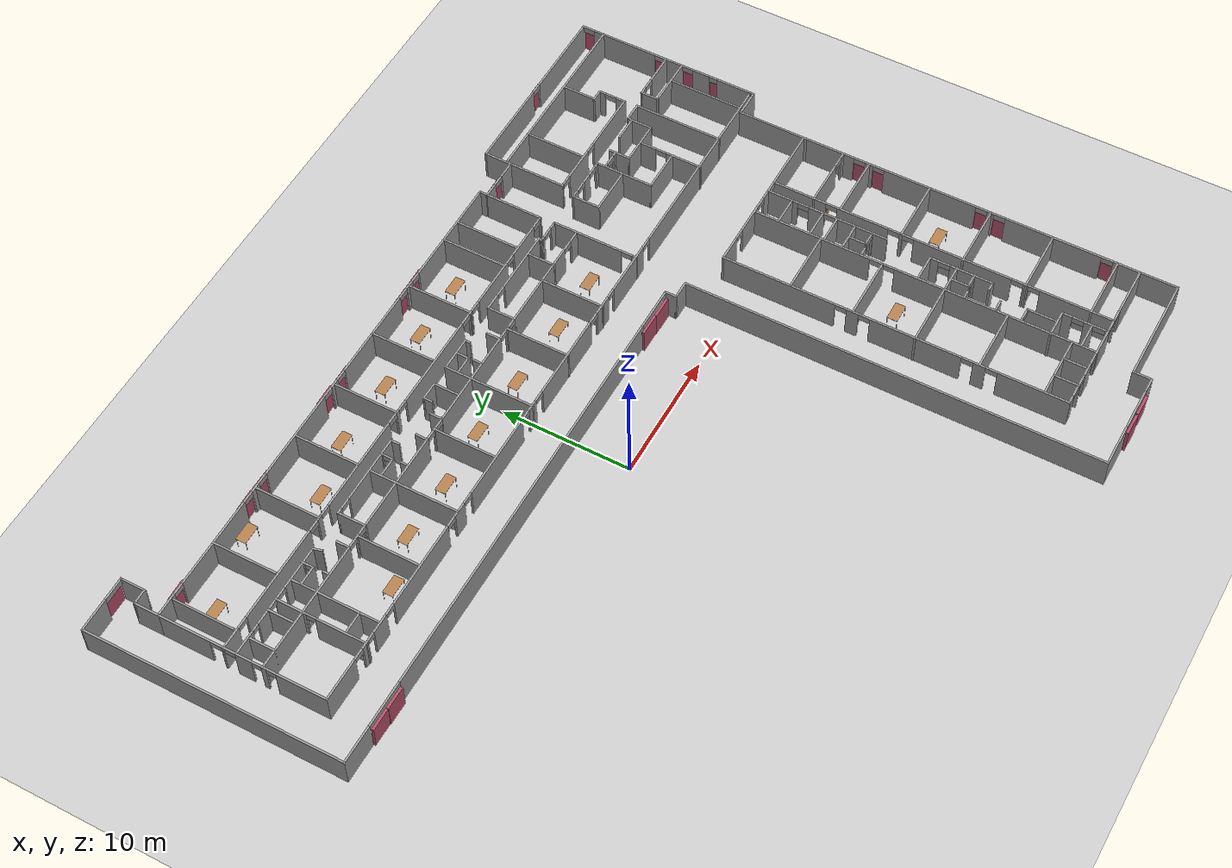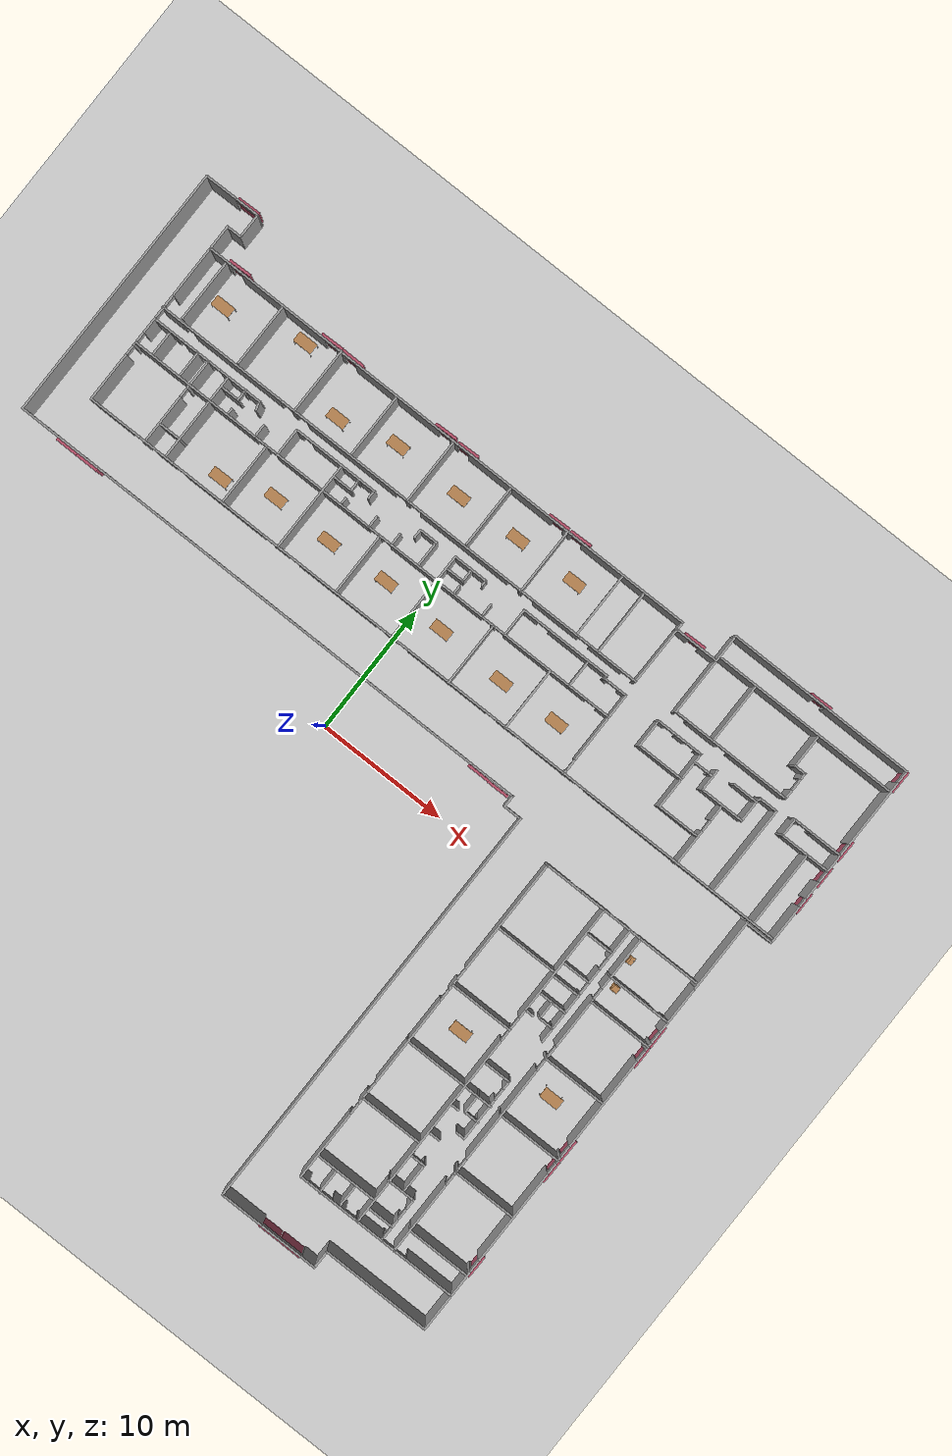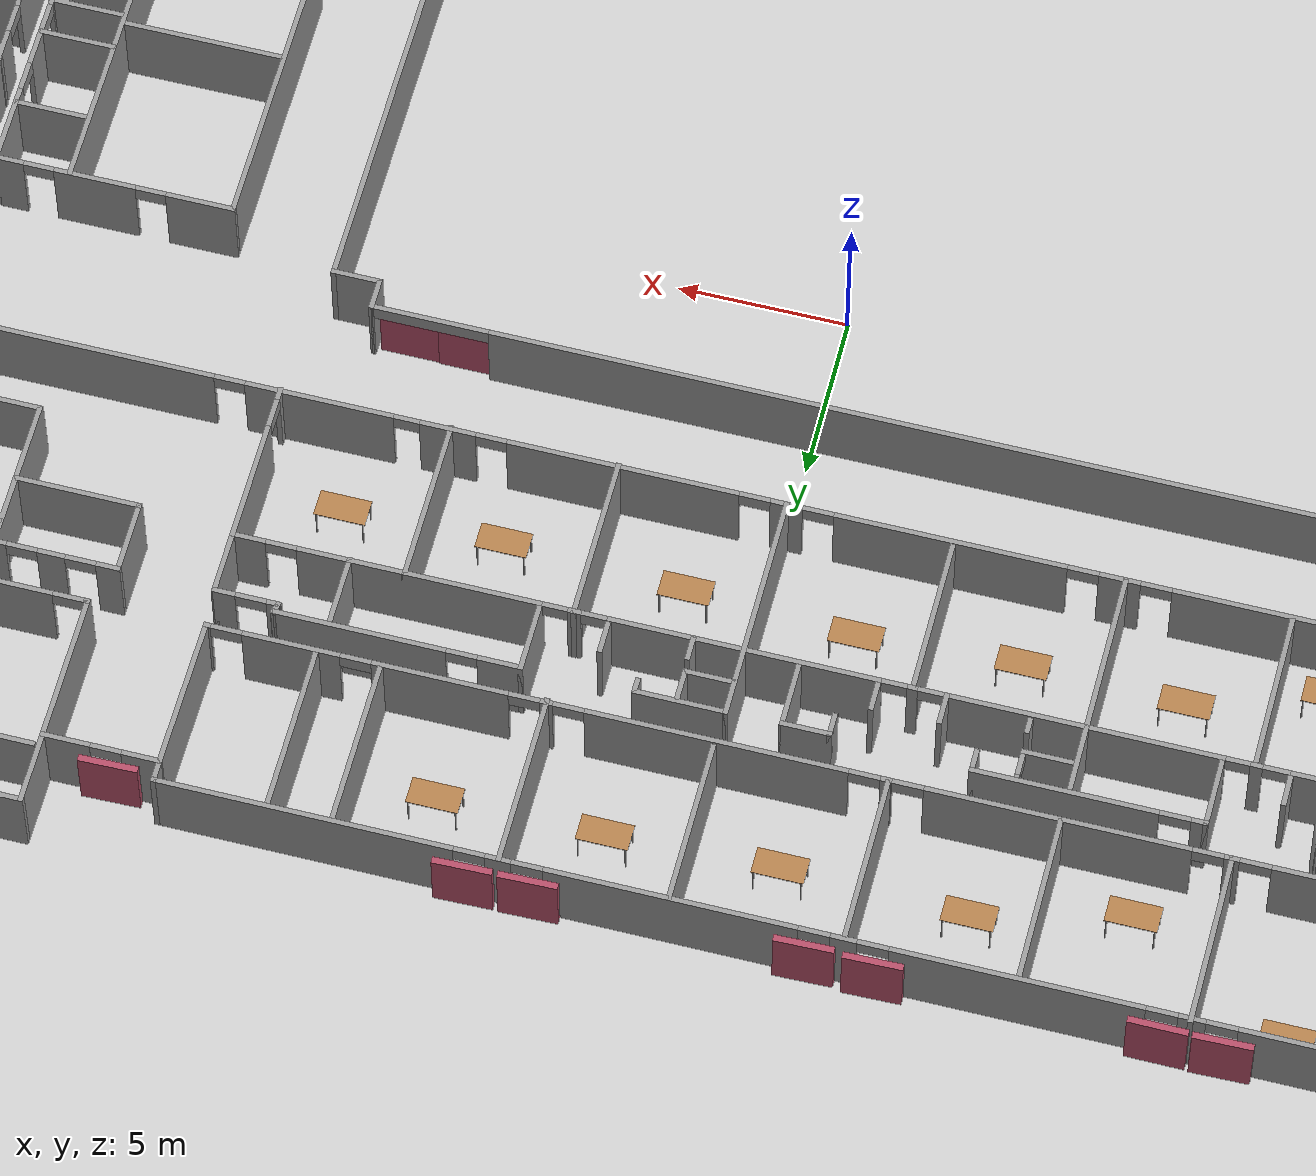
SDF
<sdf version="1.6">
 <world name="default">
  <light name="sun" type="directional">
   <pose>0 0 10 0 -0 0</pose>
   <diffuse>0.8 0.8 0.8 1</diffuse>
   <specular>0.2 0.2 0.2 1</specular>
   <attenuation>
    <range>1000</range>
    <constant>0.9</constant>
    <linear>0.01</linear>
    <quadratic>0.001</quadratic>
   </attenuation>
   <direction>-0.5 0.1 -0.9</direction>
  </light>
  <model name="ground_plane">
   <static>1</static>
   <link name="link">
    <collision name="collision">
     <geometry><plane><normal>0 0 1</normal><size>100 100</size></plane></geometry>
     <surface><friction><ode><mu>100</mu><mu2>50</mu2></ode></friction></surface>
    </collision>
    <visual name="visual">
     <cast_shadows>0</cast_shadows>
     <geometry><plane><normal>0 0 1</normal><size>100 100</size></plane></geometry>
     <material>
      <script><uri>file://media/materials/scripts/gazebo.material</uri><name>Gazebo/Grey</name></script>
     </material>
    </visual>
   </link>
  </model>
  <gravity>0 0 -9.8</gravity>
  <magnetic_field>6e-06 2.3e-05 -4.2e-05</magnetic_field>
  <atmosphere type="adiabatic"/>
  <physics name="default_physics" default="0" type="ode">
   <max_step_size>0.001</max_step_size>
   <real_time_factor>1</real_time_factor>
   <real_time_update_rate>1000</real_time_update_rate>
  </physics>
  <scene><ambient>0.4 0.4 0.4 1</ambient><background>0.7 0.7 0.7 1</background><shadows>1</shadows></scene>
  <spherical_coordinates>
   <surface_model>EARTH_WGS84</surface_model>
   <latitude_deg>0</latitude_deg>
   <longitude_deg>0</longitude_deg>
   <elevation>0</elevation>
   <heading_deg>0</heading_deg>
  </spherical_coordinates>
  <model name="fin_se1f1.sdf">
   <pose>1.8125 -2.2901 0 0 -0 0</pose>
   <link name="Wall_0">
    <collision name="Wall_0_Collision">
     <geometry><box><size>20 0.15 2.5</size></box></geometry>
     <pose>0 0 1.25 0 -0 0</pose>
    </collision>
    <visual name="Wall_0_Visual">
     <pose>0 0 1.25 0 -0 0</pose>
     <geometry><box><size>20 0.15 2.5</size></box></geometry>
     <material>
      <script><uri>file://media/materials/scripts/gazebo.material</uri><name>Gazebo/Grey</name></script>
      <ambient>1 1 1 1</ambient>
     </material>
     <meta><layer>0</layer></meta>
    </visual>
    <pose>-30.7496 16.4496 0 0 0 -1.5708</pose>
   </link>
   <link name="Wall_1">
    <pose>-9.82457 6.52457 0 0 -0 0</pose>
    <visual name="Wall_1_Visual_0">
     <pose>-19.528 0 1.25 0 -0 0</pose>
     <geometry><box><size>2.94395 0.15 2.5</size></box></geometry>
     <material>
      <script><uri>file://media/materials/scripts/gazebo.material</uri><name>Gazebo/Grey</name></script>
      <ambient>1 1 1 1</ambient>
     </material>
     <meta><layer>0</layer></meta>
    </visual>
    <collision name="Wall_1_Collision_0">
     <geometry><box><size>2.94395 0.15 2.5</size></box></geometry>
     <pose>-19.528 0 1.25 0 -0 0</pose>
    </collision>
    <visual name="Wall_1_Visual_1">
     <pose>1.49202 0 1.25 0 -0 0</pose>
     <geometry><box><size>31.9924 0.15 2.5</size></box></geometry>
     <material>
      <script><uri>file://media/materials/scripts/gazebo.material</uri><name>Gazebo/Grey</name></script>
      <ambient>1 1 1 1</ambient>
     </material>
     <meta><layer>0</layer></meta>
    </visual>
    <collision name="Wall_1_Collision_1">
     <geometry><box><size>31.9924 0.15 2.5</size></box></geometry>
     <pose>1.49202 0 1.25 0 -0 0</pose>
    </collision>
    <visual name="Wall_1_Visual_2">
     <pose>20.9503 0 1.25 0 -0 0</pose>
     <geometry><box><size>0.099489 0.15 2.5</size></box></geometry>
     <material>
      <script><uri>file://media/materials/scripts/gazebo.material</uri><name>Gazebo/Grey</name></script>
      <ambient>1 1 1 1</ambient>
     </material>
     <meta><layer>0</layer></meta>
    </visual>
    <collision name="Wall_1_Collision_2">
     <geometry><box><size>0.099489 0.15 2.5</size></box></geometry>
     <pose>20.9503 0 1.25 0 -0 0</pose>
    </collision>
    <visual name="Wall_1_Visual_3">
     <pose>-16.2801 0 2.25 0 -0 0</pose>
     <geometry><box><size>3.55186 0.15 0.5</size></box></geometry>
     <material>
      <script><uri>file://media/materials/scripts/gazebo.material</uri><name>Gazebo/Grey</name></script>
      <ambient>1 1 1 1</ambient>
     </material>
     <meta><layer>0</layer></meta>
    </visual>
    <collision name="Wall_1_Collision_3">
     <geometry><box><size>3.55186 0.15 0.5</size></box></geometry>
     <pose>-16.2801 0 2.25 0 -0 0</pose>
    </collision>
    <visual name="Wall_1_Visual_4">
     <pose>19.1944 0 2.25 0 -0 0</pose>
     <geometry><box><size>3.41229 0.15 0.5</size></box></geometry>
     <material>
      <script><uri>file://media/materials/scripts/gazebo.material</uri><name>Gazebo/Grey</name></script>
      <ambient>1 1 1 1</ambient>
     </material>
     <meta><layer>0</layer></meta>
    </visual>
    <collision name="Wall_1_Collision_4">
     <geometry><box><size>3.41229 0.15 0.5</size></box></geometry>
     <pose>19.1944 0 2.25 0 -0 0</pose>
    </collision>
   </link>
   <link name="Wall_10">
    <pose>28.6504 -10.5254 0 0 -0 1.5708</pose>
    <visual name="Wall_10_Visual_0">
     <pose>-12.1333 0 1.25 0 -0 0</pose>
     <geometry><box><size>4.98346 0.15 2.5</size></box></geometry>
     <material>
      <script><uri>file://media/materials/scripts/gazebo.material</uri><name>Gazebo/Grey</name></script>
      <ambient>1 1 1 1</ambient>
     </material>
     <meta><layer>0</layer></meta>
    </visual>
    <collision name="Wall_10_Collision_0">
     <geometry><box><size>4.98346 0.15 2.5</size></box></geometry>
     <pose>-12.1333 0 1.25 0 -0 0</pose>
    </collision>
    <visual name="Wall_10_Visual_1">
     <pose>-5.01797 0 1.25 0 -0 0</pose>
     <geometry><box><size>7.44713 0.15 2.5</size></box></geometry>
     <material>
      <script><uri>file://media/materials/scripts/gazebo.material</uri><name>Gazebo/Grey</name></script>
      <ambient>1 1 1 1</ambient>
     </material>
     <meta><layer>0</layer></meta>
    </visual>
    <collision name="Wall_10_Collision_1">
     <geometry><box><size>7.44713 0.15 2.5</size></box></geometry>
     <pose>-5.01797 0 1.25 0 -0 0</pose>
    </collision>
    <visual name="Wall_10_Visual_2">
     <pose>-0.130374 0 1.25 0 -0 0</pose>
     <geometry><box><size>0.528064 0.15 2.5</size></box></geometry>
     <material>
      <script><uri>file://media/materials/scripts/gazebo.material</uri><name>Gazebo/Grey</name></script>
      <ambient>1 1 1 1</ambient>
     </material>
     <meta><layer>0</layer></meta>
    </visual>
    <collision name="Wall_10_Collision_2">
     <geometry><box><size>0.528064 0.15 2.5</size></box></geometry>
     <pose>-0.130374 0 1.25 0 -0 0</pose>
    </collision>
    <visual name="Wall_10_Visual_3">
     <pose>4.68683 0 1.25 0 -0 0</pose>
     <geometry><box><size>7.30634 0.15 2.5</size></box></geometry>
     <material>
      <script><uri>file://media/materials/scripts/gazebo.material</uri><name>Gazebo/Grey</name></script>
      <ambient>1 1 1 1</ambient>
     </material>
     <meta><layer>0</layer></meta>
    </visual>
    <collision name="Wall_10_Collision_3">
     <geometry><box><size>7.30634 0.15 2.5</size></box></geometry>
     <pose>4.68683 0 1.25 0 -0 0</pose>
    </collision>
    <visual name="Wall_10_Visual_4">
     <pose>9.56437 0 1.25 0 -0 0</pose>
     <geometry><box><size>0.648745 0.15 2.5</size></box></geometry>
     <material>
      <script><uri>file://media/materials/scripts/gazebo.material</uri><name>Gazebo/Grey</name></script>
      <ambient>1 1 1 1</ambient>
     </material>
     <meta><layer>0</layer></meta>
    </visual>
    <collision name="Wall_10_Collision_4">
     <geometry><box><size>0.648745 0.15 2.5</size></box></geometry>
     <pose>9.56437 0 1.25 0 -0 0</pose>
    </collision>
    <visual name="Wall_10_Visual_5">
     <pose>12.7069 0 1.25 0 -0 0</pose>
     <geometry><box><size>3.83626 0.15 2.5</size></box></geometry>
     <material>
      <script><uri>file://media/materials/scripts/gazebo.material</uri><name>Gazebo/Grey</name></script>
      <ambient>1 1 1 1</ambient>
     </material>
     <meta><layer>0</layer></meta>
    </visual>
    <collision name="Wall_10_Collision_5">
     <geometry><box><size>3.83626 0.15 2.5</size></box></geometry>
     <pose>12.7069 0 1.25 0 -0 0</pose>
    </collision>
    <visual name="Wall_10_Visual_6">
     <pose>-9.19154 0 2.25 0 -0 0</pose>
     <geometry><box><size>0.9 0.15 0.5</size></box></geometry>
     <material>
      <script><uri>file://media/materials/scripts/gazebo.material</uri><name>Gazebo/Grey</name></script>
      <ambient>1 1 1 1</ambient>
     </material>
     <meta><layer>0</layer></meta>
    </visual>
    <collision name="Wall_10_Collision_6">
     <geometry><box><size>0.9 0.15 0.5</size></box></geometry>
     <pose>-9.19154 0 2.25 0 -0 0</pose>
    </collision>
    <visual name="Wall_10_Visual_7">
     <pose>-0.844406 0 2.25 0 -0 0</pose>
     <geometry><box><size>0.9 0.15 0.5</size></box></geometry>
     <material>
      <script><uri>file://media/materials/scripts/gazebo.material</uri><name>Gazebo/Grey</name></script>
      <ambient>1 1 1 1</ambient>
     </material>
     <meta><layer>0</layer></meta>
    </visual>
    <collision name="Wall_10_Collision_7">
     <geometry><box><size>0.9 0.15 0.5</size></box></geometry>
     <pose>-0.844406 0 2.25 0 -0 0</pose>
    </collision>
    <visual name="Wall_10_Visual_8">
     <pose>0.583658 0 2.25 0 -0 0</pose>
     <geometry><box><size>0.9 0.15 0.5</size></box></geometry>
     <material>
      <script><uri>file://media/materials/scripts/gazebo.material</uri><name>Gazebo/Grey</name></script>
      <ambient>1 1 1 1</ambient>
     </material>
     <meta><layer>0</layer></meta>
    </visual>
    <collision name="Wall_10_Collision_8">
     <geometry><box><size>0.9 0.15 0.5</size></box></geometry>
     <pose>0.583658 0 2.25 0 -0 0</pose>
    </collision>
    <visual name="Wall_10_Visual_9">
     <pose>8.78999 0 2.25 0 -0 0</pose>
     <geometry><box><size>0.9 0.15 0.5</size></box></geometry>
     <material>
      <script><uri>file://media/materials/scripts/gazebo.material</uri><name>Gazebo/Grey</name></script>
      <ambient>1 1 1 1</ambient>
     </material>
     <meta><layer>0</layer></meta>
    </visual>
    <collision name="Wall_10_Collision_9">
     <geometry><box><size>0.9 0.15 0.5</size></box></geometry>
     <pose>8.78999 0 2.25 0 -0 0</pose>
    </collision>
    <visual name="Wall_10_Visual_10">
     <pose>10.3387 0 2.25 0 -0 0</pose>
     <geometry><box><size>0.9 0.15 0.5</size></box></geometry>
     <material>
      <script><uri>file://media/materials/scripts/gazebo.material</uri><name>Gazebo/Grey</name></script>
      <ambient>1 1 1 1</ambient>
     </material>
     <meta><layer>0</layer></meta>
    </visual>
    <collision name="Wall_10_Collision_10">
     <geometry><box><size>0.9 0.15 0.5</size></box></geometry>
     <pose>10.3387 0 2.25 0 -0 0</pose>
    </collision>
   </link>
   <link name="Wall_100">
    <collision name="Wall_100_Collision">
     <geometry><box><size>2.25 0.15 2.5</size></box></geometry>
     <pose>0 0 1.25 0 -0 0</pose>
    </collision>
    <visual name="Wall_100_Visual">
     <pose>0 0 1.25 0 -0 0</pose>
     <geometry><box><size>2.25 0.15 2.5</size></box></geometry>
     <material>
      <script><uri>file://media/materials/scripts/gazebo.material</uri><name>Gazebo/Grey</name></script>
      <ambient>1 1 1 1</ambient>
     </material>
     <meta><layer>0</layer></meta>
    </visual>
    <pose>-15.464 15.7396 0 0 -0 1.5708</pose>
   </link>
   <link name="Wall_101">
    <pose>-12.164 16.7896 0 0 -0 0</pose>
    <visual name="Wall_101_Visual_0">
     <pose>-3.13147 0 1.25 0 -0 0</pose>
     <geometry><box><size>0.487063 0.15 2.5</size></box></geometry>
     <material>
      <script><uri>file://media/materials/scripts/gazebo.material</uri><name>Gazebo/Grey</name></script>
      <ambient>1 1 1 1</ambient>
     </material>
     <meta><layer>0</layer></meta>
    </visual>
    <collision name="Wall_101_Collision_0">
     <geometry><box><size>0.487063 0.15 2.5</size></box></geometry>
     <pose>-3.13147 0 1.25 0 -0 0</pose>
    </collision>
    <visual name="Wall_101_Visual_1">
     <pose>0.693532 0 1.25 0 -0 0</pose>
     <geometry><box><size>5.36294 0.15 2.5</size></box></geometry>
     <material>
      <script><uri>file://media/materials/scripts/gazebo.material</uri><name>Gazebo/Grey</name></script>
      <ambient>1 1 1 1</ambient>
     </material>
     <meta><layer>0</layer></meta>
    </visual>
    <collision name="Wall_101_Collision_1">
     <geometry><box><size>5.36294 0.15 2.5</size></box></geometry>
     <pose>0.693532 0 1.25 0 -0 0</pose>
    </collision>
    <visual name="Wall_101_Visual_2">
     <pose>-2.43794 0 2.25 0 -0 0</pose>
     <geometry><box><size>0.9 0.15 0.5</size></box></geometry>
     <material>
      <script><uri>file://media/materials/scripts/gazebo.material</uri><name>Gazebo/Grey</name></script>
      <ambient>1 1 1 1</ambient>
     </material>
     <meta><layer>0</layer></meta>
    </visual>
    <collision name="Wall_101_Collision_2">
     <geometry><box><size>0.9 0.15 0.5</size></box></geometry>
     <pose>-2.43794 0 2.25 0 -0 0</pose>
    </collision>
   </link>
   <link name="Wall_102">
    <collision name="Wall_102_Collision">
     <geometry><box><size>0.75 0.15 2.5</size></box></geometry>
     <pose>0 0 1.25 0 -0 0</pose>
    </collision>
    <visual name="Wall_102_Visual">
     <pose>0 0 1.25 0 -0 0</pose>
     <geometry><box><size>0.75 0.15 2.5</size></box></geometry>
     <material>
      <script><uri>file://media/materials/scripts/gazebo.material</uri><name>Gazebo/Grey</name></script>
      <ambient>1 1 1 1</ambient>
     </material>
     <meta><layer>0</layer></meta>
    </visual>
    <pose>-8.86395 16.4896 0 0 0 -1.5708</pose>
   </link>
   <link name="Wall_104">
    <collision name="Wall_104_Collision">
     <geometry><box><size>7 0.15 2.5</size></box></geometry>
     <pose>0 0 1.25 0 -0 0</pose>
    </collision>
    <visual name="Wall_104_Visual">
     <pose>0 0 1.25 0 -0 0</pose>
     <geometry><box><size>7 0.15 2.5</size></box></geometry>
     <material>
      <script><uri>file://media/materials/scripts/gazebo.material</uri><name>Gazebo/Grey</name></script>
      <ambient>1 1 1 1</ambient>
     </material>
     <meta><layer>0</layer></meta>
    </visual>
    <pose>-11.6118 13.3512 0 0 0 -1.5708</pose>
   </link>
   <link name="Wall_108">
    <collision name="Wall_108_Collision">
     <geometry><box><size>7 0.15 2.5</size></box></geometry>
     <pose>0 0 1.25 0 -0 0</pose>
    </collision>
    <visual name="Wall_108_Visual">
     <pose>0 0 1.25 0 -0 0</pose>
     <geometry><box><size>7 0.15 2.5</size></box></geometry>
     <material>
      <script><uri>file://media/materials/scripts/gazebo.material</uri><name>Gazebo/Grey</name></script>
      <ambient>1 1 1 1</ambient>
     </material>
     <meta><layer>0</layer></meta>
    </visual>
    <pose>-1.87432 13.2994 0 0 -0 1.5708</pose>
   </link>
   <link name="Wall_109">
    <collision name="Wall_109_Collision">
     <geometry><box><size>2.75 0.15 2.5</size></box></geometry>
     <pose>0 0 1.25 0 -0 0</pose>
    </collision>
    <visual name="Wall_109_Visual">
     <pose>0 0 1.25 0 -0 0</pose>
     <geometry><box><size>2.75 0.15 2.5</size></box></geometry>
     <material>
      <script><uri>file://media/materials/scripts/gazebo.material</uri><name>Gazebo/Grey</name></script>
      <ambient>1 1 1 1</ambient>
     </material>
     <meta><layer>0</layer></meta>
    </visual>
    <pose>-0.574318 16.7244 0 0 -0 0</pose>
   </link>
   <link name="Wall_110">
    <collision name="Wall_110_Collision">
     <geometry><box><size>0.5 0.15 2.5</size></box></geometry>
     <pose>0 0 1.25 0 -0 0</pose>
    </collision>
    <visual name="Wall_110_Visual">
     <pose>0 0 1.25 0 -0 0</pose>
     <geometry><box><size>0.5 0.15 2.5</size></box></geometry>
     <material>
      <script><uri>file://media/materials/scripts/gazebo.material</uri><name>Gazebo/Grey</name></script>
      <ambient>1 1 1 1</ambient>
     </material>
     <meta><layer>0</layer></meta>
    </visual>
    <pose>0.725682 16.5494 0 0 0 -1.5708</pose>
   </link>
   <link name="Wall_112">
    <collision name="Wall_112_Collision">
     <geometry><box><size>4.75 0.15 2.5</size></box></geometry>
     <pose>0 0 1.25 0 -0 0</pose>
    </collision>
    <visual name="Wall_112_Visual">
     <pose>0 0 1.25 0 -0 0</pose>
     <geometry><box><size>4.75 0.15 2.5</size></box></geometry>
     <material>
      <script><uri>file://media/materials/scripts/gazebo.material</uri><name>Gazebo/Grey</name></script>
      <ambient>1 1 1 1</ambient>
     </material>
     <meta><layer>0</layer></meta>
    </visual>
    <pose>-6.68954 12.3361 0 0 0 -1.5708</pose>
   </link>
   <link name="Wall_114">
    <collision name="Wall_114_Collision">
     <geometry><box><size>2 0.15 2.5</size></box></geometry>
     <pose>0 0 1.25 0 -0 0</pose>
    </collision>
    <visual name="Wall_114_Visual">
     <pose>0 0 1.25 0 -0 0</pose>
     <geometry><box><size>2 0.15 2.5</size></box></geometry>
     <material>
      <script><uri>file://media/materials/scripts/gazebo.material</uri><name>Gazebo/Grey</name></script>
      <ambient>1 1 1 1</ambient>
     </material>
     <meta><layer>0</layer></meta>
    </visual>
    <pose>-26.1645 15.6146 0 0 -0 1.5708</pose>
   </link>
   <link name="Wall_116">
    <collision name="Wall_116_Collision">
     <geometry><box><size>2 0.15 2.5</size></box></geometry>
     <pose>0 0 1.25 0 -0 0</pose>
    </collision>
    <visual name="Wall_116_Visual">
     <pose>0 0 1.25 0 -0 0</pose>
     <geometry><box><size>2 0.15 2.5</size></box></geometry>
     <material>
      <script><uri>file://media/materials/scripts/gazebo.material</uri><name>Gazebo/Grey</name></script>
      <ambient>1 1 1 1</ambient>
     </material>
     <meta><layer>0</layer></meta>
    </visual>
    <pose>-23.8638 15.7977 0 0 0 -1.5708</pose>
   </link>
   <link name="Wall_118">
    <collision name="Wall_118_Collision">
     <geometry><box><size>1.75 0.15 2.5</size></box></geometry>
     <pose>0 0 1.25 0 -0 0</pose>
    </collision>
    <visual name="Wall_118_Visual">
     <pose>0 0 1.25 0 -0 0</pose>
     <geometry><box><size>1.75 0.15 2.5</size></box></geometry>
     <material>
      <script><uri>file://media/materials/scripts/gazebo.material</uri><name>Gazebo/Grey</name></script>
      <ambient>1 1 1 1</ambient>
     </material>
     <meta><layer>0</layer></meta>
    </visual>
    <pose>-22.0422 11.426 0 0 -0 3.14159</pose>
   </link>
   <link name="Wall_12">
    <collision name="Wall_12_Collision">
     <geometry><box><size>5.75 0.15 2.5</size></box></geometry>
     <pose>0 0 1.25 0 -0 0</pose>
    </collision>
    <visual name="Wall_12_Visual">
     <pose>0 0 1.25 0 -0 0</pose>
     <geometry><box><size>5.75 0.15 2.5</size></box></geometry>
     <material>
      <script><uri>file://media/materials/scripts/gazebo.material</uri><name>Gazebo/Grey</name></script>
      <ambient>1 1 1 1</ambient>
     </material>
     <meta><layer>0</layer></meta>
    </visual>
    <pose>28.6504 6.82457 0 0 -0 1.5708</pose>
   </link>
   <link name="Wall_120">
    <pose>-19.7977 16.3512 0 0 0 -1.5708</pose>
    <visual name="Wall_120_Visual_0">
     <pose>-0.341993 0 1.25 0 -0 0</pose>
     <geometry><box><size>0.316013 0.15 2.5</size></box></geometry>
     <material>
      <script><uri>file://media/materials/scripts/gazebo.material</uri><name>Gazebo/Grey</name></script>
      <ambient>1 1 1 1</ambient>
     </material>
     <meta><layer>0</layer></meta>
    </visual>
    <collision name="Wall_120_Collision_0">
     <geometry><box><size>0.316013 0.15 2.5</size></box></geometry>
     <pose>-0.341993 0 1.25 0 -0 0</pose>
    </collision>
    <visual name="Wall_120_Visual_1">
     <pose>0.158007 0 2.25 0 -0 0</pose>
     <geometry><box><size>0.683987 0.15 0.5</size></box></geometry>
     <material>
      <script><uri>file://media/materials/scripts/gazebo.material</uri><name>Gazebo/Grey</name></script>
      <ambient>1 1 1 1</ambient>
     </material>
     <meta><layer>0</layer></meta>
    </visual>
    <collision name="Wall_120_Collision_1">
     <geometry><box><size>0.683987 0.15 0.5</size></box></geometry>
     <pose>0.158007 0 2.25 0 -0 0</pose>
    </collision>
   </link>
   <link name="Wall_121">
    <collision name="Wall_121_Collision">
     <geometry><box><size>1.5 0.15 2.5</size></box></geometry>
     <pose>0 0 1.25 0 -0 0</pose>
    </collision>
    <visual name="Wall_121_Visual">
     <pose>0 0 1.25 0 -0 0</pose>
     <geometry><box><size>1.5 0.15 2.5</size></box></geometry>
     <material>
      <script><uri>file://media/materials/scripts/gazebo.material</uri><name>Gazebo/Grey</name></script>
      <ambient>1 1 1 1</ambient>
     </material>
     <meta><layer>0</layer></meta>
    </visual>
    <pose>-20.4727 15.9262 0 0 -0 3.14159</pose>
   </link>
   <link name="Wall_123">
    <collision name="Wall_123_Collision">
     <geometry><box><size>0.5 0.15 2.5</size></box></geometry>
     <pose>0 0 1.25 0 -0 0</pose>
    </collision>
    <visual name="Wall_123_Visual">
     <pose>0 0 1.25 0 -0 0</pose>
     <geometry><box><size>0.5 0.15 2.5</size></box></geometry>
     <material>
      <script><uri>file://media/materials/scripts/gazebo.material</uri><name>Gazebo/Grey</name></script>
      <ambient>1 1 1 1</ambient>
     </material>
     <meta><layer>0</layer></meta>
    </visual>
    <pose>-19.7442 14.9961 0 0 0 -1.5708</pose>
   </link>
   <link name="Wall_125">
    <collision name="Wall_125_Collision">
     <geometry><box><size>1 0.15 2.5</size></box></geometry>
     <pose>0 0 1.25 0 -0 0</pose>
    </collision>
    <visual name="Wall_125_Visual">
     <pose>0 0 1.25 0 -0 0</pose>
     <geometry><box><size>1 0.15 2.5</size></box></geometry>
     <material>
      <script><uri>file://media/materials/scripts/gazebo.material</uri><name>Gazebo/Grey</name></script>
      <ambient>1 1 1 1</ambient>
     </material>
     <meta><layer>0</layer></meta>
    </visual>
    <pose>-17.39 15.2276 0 0 0 -1.5708</pose>
   </link>
   <link name="Wall_127">
    <pose>-10.1137 16.2977 0 0 0 -1.5708</pose>
    <visual name="Wall_127_Visual_0">
     <pose>-0.408972 0 1.25 0 -0 0</pose>
     <geometry><box><size>0.182055 0.15 2.5</size></box></geometry>
     <material>
      <script><uri>file://media/materials/scripts/gazebo.material</uri><name>Gazebo/Grey</name></script>
      <ambient>1 1 1 1</ambient>
     </material>
     <meta><layer>0</layer></meta>
    </visual>
    <collision name="Wall_127_Collision_0">
     <geometry><box><size>0.182055 0.15 2.5</size></box></geometry>
     <pose>-0.408972 0 1.25 0 -0 0</pose>
    </collision>
    <visual name="Wall_127_Visual_1">
     <pose>0.480687 0 1.25 0 -0 0</pose>
     <geometry><box><size>0.038626 0.15 2.5</size></box></geometry>
     <material>
      <script><uri>file://media/materials/scripts/gazebo.material</uri><name>Gazebo/Grey</name></script>
      <ambient>1 1 1 1</ambient>
     </material>
     <meta><layer>0</layer></meta>
    </visual>
    <collision name="Wall_127_Collision_1">
     <geometry><box><size>0.038626 0.15 2.5</size></box></geometry>
     <pose>0.480687 0 1.25 0 -0 0</pose>
    </collision>
    <visual name="Wall_127_Visual_2">
     <pose>0.071714 0 2.25 0 -0 0</pose>
     <geometry><box><size>0.779319 0.15 0.5</size></box></geometry>
     <material>
      <script><uri>file://media/materials/scripts/gazebo.material</uri><name>Gazebo/Grey</name></script>
      <ambient>1 1 1 1</ambient>
     </material>
     <meta><layer>0</layer></meta>
    </visual>
    <collision name="Wall_127_Collision_2">
     <geometry><box><size>0.779319 0.15 0.5</size></box></geometry>
     <pose>0.071714 0 2.25 0 -0 0</pose>
    </collision>
   </link>
   <link name="Wall_128">
    <collision name="Wall_128_Collision">
     <geometry><box><size>1.5 0.15 2.5</size></box></geometry>
     <pose>0 0 1.25 0 -0 0</pose>
    </collision>
    <visual name="Wall_128_Visual">
     <pose>0 0 1.25 0 -0 0</pose>
     <geometry><box><size>1.5 0.15 2.5</size></box></geometry>
     <material>
      <script><uri>file://media/materials/scripts/gazebo.material</uri><name>Gazebo/Grey</name></script>
      <ambient>1 1 1 1</ambient>
     </material>
     <meta><layer>0</layer></meta>
    </visual>
    <pose>-10.7887 15.8727 0 0 -0 3.14159</pose>
   </link>
   <link name="Wall_13">
    <collision name="Wall_13_Collision">
     <geometry><box><size>2.25 0.15 2.5</size></box></geometry>
     <pose>0 0 1.25 0 -0 0</pose>
    </collision>
    <visual name="Wall_13_Visual">
     <pose>0 0 1.25 0 -0 0</pose>
     <geometry><box><size>2.25 0.15 2.5</size></box></geometry>
     <material>
      <script><uri>file://media/materials/scripts/gazebo.material</uri><name>Gazebo/Grey</name></script>
      <ambient>1 1 1 1</ambient>
     </material>
     <meta><layer>0</layer></meta>
    </visual>
    <pose>29.7004 9.62457 0 0 -0 0</pose>
   </link>
   <link name="Wall_130">
    <collision name="Wall_130_Collision">
     <geometry><box><size>0.5 0.15 2.5</size></box></geometry>
     <pose>0 0 1.25 0 -0 0</pose>
    </collision>
    <visual name="Wall_130_Visual">
     <pose>0 0 1.25 0 -0 0</pose>
     <geometry><box><size>0.5 0.15 2.5</size></box></geometry>
     <material>
      <script><uri>file://media/materials/scripts/gazebo.material</uri><name>Gazebo/Grey</name></script>
      <ambient>1 1 1 1</ambient>
     </material>
     <meta><layer>0</layer></meta>
    </visual>
    <pose>-10.0602 15.0496 0 0 0 -1.5708</pose>
   </link>
   <link name="Wall_132">
    <collision name="Wall_132_Collision">
     <geometry><box><size>0.75 0.15 2.5</size></box></geometry>
     <pose>0 0 1.25 0 -0 0</pose>
    </collision>
    <visual name="Wall_132_Visual">
     <pose>0 0 1.25 0 -0 0</pose>
     <geometry><box><size>0.75 0.15 2.5</size></box></geometry>
     <material>
      <script><uri>file://media/materials/scripts/gazebo.material</uri><name>Gazebo/Grey</name></script>
      <ambient>1 1 1 1</ambient>
     </material>
     <meta><layer>0</layer></meta>
    </visual>
    <pose>-4.81696 16.3807 0 0 -0 1.5708</pose>
   </link>
   <link name="Wall_133">
    <collision name="Wall_133_Collision">
     <geometry><box><size>1.5 0.15 2.5</size></box></geometry>
     <pose>0 0 1.25 0 -0 0</pose>
    </collision>
    <visual name="Wall_133_Visual">
     <pose>0 0 1.25 0 -0 0</pose>
     <geometry><box><size>1.5 0.15 2.5</size></box></geometry>
     <material>
      <script><uri>file://media/materials/scripts/gazebo.material</uri><name>Gazebo/Grey</name></script>
      <ambient>1 1 1 1</ambient>
     </material>
     <meta><layer>0</layer></meta>
    </visual>
    <pose>-4.14196 16.6807 0 0 -0 0</pose>
   </link>
   <link name="Wall_134">
    <collision name="Wall_134_Collision">
     <geometry><box><size>2 0.15 2.5</size></box></geometry>
     <pose>0 0 1.25 0 -0 0</pose>
    </collision>
    <visual name="Wall_134_Visual">
     <pose>0 0 1.25 0 -0 0</pose>
     <geometry><box><size>2 0.15 2.5</size></box></geometry>
     <material>
      <script><uri>file://media/materials/scripts/gazebo.material</uri><name>Gazebo/Grey</name></script>
      <ambient>1 1 1 1</ambient>
     </material>
     <meta><layer>0</layer></meta>
    </visual>
    <pose>-3.46696 15.7557 0 0 0 -1.5708</pose>
   </link>
   <link name="Wall_136">
    <collision name="Wall_136_Collision">
     <geometry><box><size>1 0.15 2.5</size></box></geometry>
     <pose>0 0 1.25 0 -0 0</pose>
    </collision>
    <visual name="Wall_136_Visual">
     <pose>0 0 1.25 0 -0 0</pose>
     <geometry><box><size>1 0.15 2.5</size></box></geometry>
     <material>
      <script><uri>file://media/materials/scripts/gazebo.material</uri><name>Gazebo/Grey</name></script>
      <ambient>1 1 1 1</ambient>
     </material>
     <meta><layer>0</layer></meta>
    </visual>
    <pose>-5.7265 15.1681 0 0 -0 1.5708</pose>
   </link>
   <link name="Wall_138">
    <collision name="Wall_138_Collision">
     <geometry><box><size>1 0.15 2.5</size></box></geometry>
     <pose>0 0 1.25 0 -0 0</pose>
    </collision>
    <visual name="Wall_138_Visual">
     <pose>0 0 1.25 0 -0 0</pose>
     <geometry><box><size>1 0.15 2.5</size></box></geometry>
     <material>
      <script><uri>file://media/materials/scripts/gazebo.material</uri><name>Gazebo/Grey</name></script>
      <ambient>1 1 1 1</ambient>
     </material>
     <meta><layer>0</layer></meta>
    </visual>
    <pose>-7.65259 15.1146 0 0 -0 1.5708</pose>
   </link>
   <link name="Wall_140">
    <collision name="Wall_140_Collision">
     <geometry><box><size>2 0.15 2.5</size></box></geometry>
     <pose>0 0 1.25 0 -0 0</pose>
    </collision>
    <visual name="Wall_140_Visual">
     <pose>0 0 1.25 0 -0 0</pose>
     <geometry><box><size>2 0.15 2.5</size></box></geometry>
     <material>
      <script><uri>file://media/materials/scripts/gazebo.material</uri><name>Gazebo/Grey</name></script>
      <ambient>1 1 1 1</ambient>
     </material>
     <meta><layer>0</layer></meta>
    </visual>
    <pose>12.848 15.6146 0 0 -0 1.5708</pose>
   </link>
   <link name="Wall_141">
    <pose>11.923 16.5396 0 0 -0 3.14159</pose>
    <visual name="Wall_141_Visual_0">
     <pose>-0.657066 0 1.25 0 -0 0</pose>
     <geometry><box><size>0.685867 0.15 2.5</size></box></geometry>
     <material>
      <script><uri>file://media/materials/scripts/gazebo.material</uri><name>Gazebo/Grey</name></script>
      <ambient>1 1 1 1</ambient>
     </material>
     <meta><layer>0</layer></meta>
    </visual>
    <collision name="Wall_141_Collision_0">
     <geometry><box><size>0.685867 0.15 2.5</size></box></geometry>
     <pose>-0.657066 0 1.25 0 -0 0</pose>
    </collision>
    <visual name="Wall_141_Visual_1">
     <pose>0.792934 0 1.25 0 -0 0</pose>
     <geometry><box><size>0.414133 0.15 2.5</size></box></geometry>
     <material>
      <script><uri>file://media/materials/scripts/gazebo.material</uri><name>Gazebo/Grey</name></script>
      <ambient>1 1 1 1</ambient>
     </material>
     <meta><layer>0</layer></meta>
    </visual>
    <collision name="Wall_141_Collision_1">
     <geometry><box><size>0.414133 0.15 2.5</size></box></geometry>
     <pose>0.792934 0 1.25 0 -0 0</pose>
    </collision>
    <visual name="Wall_141_Visual_2">
     <pose>0.135867 0 2.25 0 -0 0</pose>
     <geometry><box><size>0.9 0.15 0.5</size></box></geometry>
     <material>
      <script><uri>file://media/materials/scripts/gazebo.material</uri><name>Gazebo/Grey</name></script>
      <ambient>1 1 1 1</ambient>
     </material>
     <meta><layer>0</layer></meta>
    </visual>
    <collision name="Wall_141_Collision_2">
     <geometry><box><size>0.9 0.15 0.5</size></box></geometry>
     <pose>0.135867 0 2.25 0 -0 0</pose>
    </collision>
   </link>
   <link name="Wall_144">
    <collision name="Wall_144_Collision">
     <geometry><box><size>2.25 0.15 2.5</size></box></geometry>
     <pose>0 0 1.25 0 -0 0</pose>
    </collision>
    <visual name="Wall_144_Visual">
     <pose>0 0 1.25 0 -0 0</pose>
     <geometry><box><size>2.25 0.15 2.5</size></box></geometry>
     <material>
      <script><uri>file://media/materials/scripts/gazebo.material</uri><name>Gazebo/Grey</name></script>
      <ambient>1 1 1 1</ambient>
     </material>
     <meta><layer>0</layer></meta>
    </visual>
    <pose>3.95745 15.7396 0 0 -0 1.5708</pose>
   </link>
   <link name="Wall_145">
    <pose>7.50746 16.7896 0 0 -0 0</pose>
    <visual name="Wall_145_Visual_0">
     <pose>-2.96499 0 1.25 0 -0 0</pose>
     <geometry><box><size>1.32002 0.15 2.5</size></box></geometry>
     <material>
      <script><uri>file://media/materials/scripts/gazebo.material</uri><name>Gazebo/Grey</name></script>
      <ambient>1 1 1 1</ambient>
     </material>
     <meta><layer>0</layer></meta>
    </visual>
    <collision name="Wall_145_Collision_0">
     <geometry><box><size>1.32002 0.15 2.5</size></box></geometry>
     <pose>-2.96499 0 1.25 0 -0 0</pose>
    </collision>
    <visual name="Wall_145_Visual_1">
     <pose>1.11001 0 1.25 0 -0 0</pose>
     <geometry><box><size>5.02998 0.15 2.5</size></box></geometry>
     <material>
      <script><uri>file://media/materials/scripts/gazebo.material</uri><name>Gazebo/Grey</name></script>
      <ambient>1 1 1 1</ambient>
     </material>
     <meta><layer>0</layer></meta>
    </visual>
    <collision name="Wall_145_Collision_1">
     <geometry><box><size>5.02998 0.15 2.5</size></box></geometry>
     <pose>1.11001 0 1.25 0 -0 0</pose>
    </collision>
    <visual name="Wall_145_Visual_2">
     <pose>-1.85498 0 2.25 0 -0 0</pose>
     <geometry><box><size>0.9 0.15 0.5</size></box></geometry>
     <material>
      <script><uri>file://media/materials/scripts/gazebo.material</uri><name>Gazebo/Grey</name></script>
      <ambient>1 1 1 1</ambient>
     </material>
     <meta><layer>0</layer></meta>
    </visual>
    <collision name="Wall_145_Collision_2">
     <geometry><box><size>0.9 0.15 0.5</size></box></geometry>
     <pose>-1.85498 0 2.25 0 -0 0</pose>
    </collision>
   </link>
   <link name="Wall_146">
    <collision name="Wall_146_Collision">
     <geometry><box><size>0.406976 0.15 2.5</size></box></geometry>
     <pose>0 0 1.25 0 -0 0</pose>
    </collision>
    <visual name="Wall_146_Visual">
     <pose>0 0 1.25 0 -0 0</pose>
     <geometry><box><size>0.406976 0.15 2.5</size></box></geometry>
     <material>
      <script><uri>file://media/materials/scripts/gazebo.material</uri><name>Gazebo/Grey</name></script>
      <ambient>1 1 1 1</ambient>
     </material>
     <meta><layer>0</layer></meta>
    </visual>
    <pose>11.0277 16.6646 0 0 0 -1.80434</pose>
   </link>
   <link name="Wall_148">
    <collision name="Wall_148_Collision">
     <geometry><box><size>2.25 0.15 2.5</size></box></geometry>
     <pose>0 0 1.25 0 -0 0</pose>
    </collision>
    <visual name="Wall_148_Visual">
     <pose>0 0 1.25 0 -0 0</pose>
     <geometry><box><size>2.25 0.15 2.5</size></box></geometry>
     <material>
      <script><uri>file://media/materials/scripts/gazebo.material</uri><name>Gazebo/Grey</name></script>
      <ambient>1 1 1 1</ambient>
     </material>
     <meta><layer>0</layer></meta>
    </visual>
    <pose>9.46821 15.7262 0 0 0 -1.5708</pose>
   </link>
   <link name="Wall_150">
    <collision name="Wall_150_Collision">
     <geometry><box><size>1.5 0.15 2.5</size></box></geometry>
     <pose>0 0 1.25 0 -0 0</pose>
    </collision>
    <visual name="Wall_150_Visual">
     <pose>0 0 1.25 0 -0 0</pose>
     <geometry><box><size>1.5 0.15 2.5</size></box></geometry>
     <material>
      <script><uri>file://media/materials/scripts/gazebo.material</uri><name>Gazebo/Grey</name></script>
      <ambient>1 1 1 1</ambient>
     </material>
     <meta><layer>0</layer></meta>
    </visual>
    <pose>-1.14582 15.7597 0 0 -0 0</pose>
   </link>
   <link name="Wall_151">
    <collision name="Wall_151_Collision">
     <geometry><box><size>1 0.15 2.5</size></box></geometry>
     <pose>0 0 1.25 0 -0 0</pose>
    </collision>
    <visual name="Wall_151_Visual">
     <pose>0 0 1.25 0 -0 0</pose>
     <geometry><box><size>1 0.15 2.5</size></box></geometry>
     <material>
      <script><uri>file://media/materials/scripts/gazebo.material</uri><name>Gazebo/Grey</name></script>
      <ambient>1 1 1 1</ambient>
     </material>
     <meta><layer>0</layer></meta>
    </visual>
    <pose>-0.470815 16.1847 0 0 -0 1.5708</pose>
   </link>
   <link name="Wall_153">
    <collision name="Wall_153_Collision">
     <geometry><box><size>0.75 0.15 2.5</size></box></geometry>
     <pose>0 0 1.25 0 -0 0</pose>
    </collision>
    <visual name="Wall_153_Visual">
     <pose>0 0 1.25 0 -0 0</pose>
     <geometry><box><size>0.75 0.15 2.5</size></box></geometry>
     <material>
      <script><uri>file://media/materials/scripts/gazebo.material</uri><name>Gazebo/Grey</name></script>
      <ambient>1 1 1 1</ambient>
     </material>
     <meta><layer>0</layer></meta>
    </visual>
    <pose>-0.42975 15.0316 0 0 0 -1.5708</pose>
   </link>
   <link name="Wall_155">
    <collision name="Wall_155_Collision">
     <geometry><box><size>1 0.15 2.5</size></box></geometry>
     <pose>0 0 1.25 0 -0 0</pose>
    </collision>
    <visual name="Wall_155_Visual">
     <pose>0 0 1.25 0 -0 0</pose>
     <geometry><box><size>1 0.15 2.5</size></box></geometry>
     <material>
      <script><uri>file://media/materials/scripts/gazebo.material</uri><name>Gazebo/Grey</name></script>
      <ambient>1 1 1 1</ambient>
     </material>
     <meta><layer>0</layer></meta>
    </visual>
    <pose>1.97786 15.2812 0 0 0 -1.5708</pose>
   </link>
   <link name="Wall_157">
    <collision name="Wall_157_Collision">
     <geometry><box><size>0.160508 0.15 2.5</size></box></geometry>
     <pose>0 0 1.25 0 -0 0</pose>
    </collision>
    <visual name="Wall_157_Visual">
     <pose>0 0 1.25 0 -0 0</pose>
     <geometry><box><size>0.160508 0.15 2.5</size></box></geometry>
     <material>
      <script><uri>file://media/materials/scripts/gazebo.material</uri><name>Gazebo/Grey</name></script>
      <ambient>1 1 1 1</ambient>
     </material>
     <meta><layer>0</layer></meta>
    </visual>
    <pose>2.99441 14.6949 0 0 -0 1.5708</pose>
   </link>
   <link name="Wall_158">
    <collision name="Wall_158_Collision">
     <geometry><box><size>5 0.15 2.5</size></box></geometry>
     <pose>0 0 1.25 0 -0 0</pose>
    </collision>
    <visual name="Wall_158_Visual">
     <pose>0 0 1.25 0 -0 0</pose>
     <geometry><box><size>5 0.15 2.5</size></box></geometry>
     <material>
      <script><uri>file://media/materials/scripts/gazebo.material</uri><name>Gazebo/Grey</name></script>
      <ambient>1 1 1 1</ambient>
     </material>
     <meta><layer>0</layer></meta>
    </visual>
    <pose>2.99441 12.2751 0 0 0 -1.5708</pose>
   </link>
   <link name="Wall_16">
    <pose>30.7504 16.9246 0 0 -0 1.5708</pose>
    <visual name="Wall_16_Visual_0">
     <pose>-5.81054 0 1.25 0 -0 0</pose>
     <geometry><box><size>3.12893 0.15 2.5</size></box></geometry>
     <material>
      <script><uri>file://media/materials/scripts/gazebo.material</uri><name>Gazebo/Grey</name></script>
      <ambient>1 1 1 1</ambient>
     </material>
     <meta><layer>0</layer></meta>
    </visual>
    <collision name="Wall_16_Collision_0">
     <geometry><box><size>3.12893 0.15 2.5</size></box></geometry>
     <pose>-5.81054 0 1.25 0 -0 0</pose>
    </collision>
    <visual name="Wall_16_Visual_1">
     <pose>-2.86079 0 1.25 0 -0 0</pose>
     <geometry><box><size>1.41306 0.15 2.5</size></box></geometry>
     <material>
      <script><uri>file://media/materials/scripts/gazebo.material</uri><name>Gazebo/Grey</name></script>
      <ambient>1 1 1 1</ambient>
     </material>
     <meta><layer>0</layer></meta>
    </visual>
    <collision name="Wall_16_Collision_1">
     <geometry><box><size>1.41306 0.15 2.5</size></box></geometry>
     <pose>-2.86079 0 1.25 0 -0 0</pose>
    </collision>
    <visual name="Wall_16_Visual_2">
     <pose>-0.547733 0 1.25 0 -0 0</pose>
     <geometry><box><size>1.41306 0.15 2.5</size></box></geometry>
     <material>
      <script><uri>file://media/materials/scripts/gazebo.material</uri><name>Gazebo/Grey</name></script>
      <ambient>1 1 1 1</ambient>
     </material>
     <meta><layer>0</layer></meta>
    </visual>
    <collision name="Wall_16_Collision_2">
     <geometry><box><size>1.41306 0.15 2.5</size></box></geometry>
     <pose>-0.547733 0 1.25 0 -0 0</pose>
    </collision>
    <visual name="Wall_16_Visual_3">
     <pose>3.70629 0 1.25 0 -0 0</pose>
     <geometry><box><size>5.29498 0.15 2.5</size></box></geometry>
     <material>
      <script><uri>file://media/materials/scripts/gazebo.material</uri><name>Gazebo/Grey</name></script>
      <ambient>1 1 1 1</ambient>
     </material>
     <meta><layer>0</layer></meta>
    </visual>
    <collision name="Wall_16_Collision_3">
     <geometry><box><size>5.29498 0.15 2.5</size></box></geometry>
     <pose>3.70629 0 1.25 0 -0 0</pose>
    </collision>
    <visual name="Wall_16_Visual_4">
     <pose>7.31439 0 1.25 0 -0 0</pose>
     <geometry><box><size>0.121222 0.15 2.5</size></box></geometry>
     <material>
      <script><uri>file://media/materials/scripts/gazebo.material</uri><name>Gazebo/Grey</name></script>
      <ambient>1 1 1 1</ambient>
     </material>
     <meta><layer>0</layer></meta>
    </visual>
    <collision name="Wall_16_Collision_4">
     <geometry><box><size>0.121222 0.15 2.5</size></box></geometry>
     <pose>7.31439 0 1.25 0 -0 0</pose>
    </collision>
    <visual name="Wall_16_Visual_5">
     <pose>-3.9067 0 2.25 0 -0 0</pose>
     <geometry><box><size>0.678751 0.15 0.5</size></box></geometry>
     <material>
      <script><uri>file://media/materials/scripts/gazebo.material</uri><name>Gazebo/Grey</name></script>
      <ambient>1 1 1 1</ambient>
     </material>
     <meta><layer>0</layer></meta>
    </visual>
    <collision name="Wall_16_Collision_5">
     <geometry><box><size>0.678751 0.15 0.5</size></box></geometry>
     <pose>-3.9067 0 2.25 0 -0 0</pose>
    </collision>
    <visual name="Wall_16_Visual_6">
     <pose>-1.70426 0 2.25 0 -0 0</pose>
     <geometry><box><size>0.9 0.15 0.5</size></box></geometry>
     <material>
      <script><uri>file://media/materials/scripts/gazebo.material</uri><name>Gazebo/Grey</name></script>
      <ambient>1 1 1 1</ambient>
     </material>
     <meta><layer>0</layer></meta>
    </visual>
    <collision name="Wall_16_Collision_6">
     <geometry><box><size>0.9 0.15 0.5</size></box></geometry>
     <pose>-1.70426 0 2.25 0 -0 0</pose>
    </collision>
    <visual name="Wall_16_Visual_7">
     <pose>0.608797 0 2.25 0 -0 0</pose>
     <geometry><box><size>0.9 0.15 0.5</size></box></geometry>
     <material>
      <script><uri>file://media/materials/scripts/gazebo.material</uri><name>Gazebo/Grey</name></script>
      <ambient>1 1 1 1</ambient>
     </material>
     <meta><layer>0</layer></meta>
    </visual>
    <collision name="Wall_16_Collision_7">
     <geometry><box><size>0.9 0.15 0.5</size></box></geometry>
     <pose>0.608797 0 2.25 0 -0 0</pose>
    </collision>
    <visual name="Wall_16_Visual_8">
     <pose>6.80378 0 2.25 0 -0 0</pose>
     <geometry><box><size>0.9 0.15 0.5</size></box></geometry>
     <material>
      <script><uri>file://media/materials/scripts/gazebo.material</uri><name>Gazebo/Grey</name></script>
      <ambient>1 1 1 1</ambient>
     </material>
     <meta><layer>0</layer></meta>
    </visual>
    <collision name="Wall_16_Collision_8">
     <geometry><box><size>0.9 0.15 0.5</size></box></geometry>
     <pose>6.80378 0 2.25 0 -0 0</pose>
    </collision>
   </link>
   <link name="Wall_160">
    <collision name="Wall_160_Collision">
     <geometry><box><size>5 0.15 2.5</size></box></geometry>
     <pose>0 0 1.25 0 -0 0</pose>
    </collision>
    <visual name="Wall_160_Visual">
     <pose>0 0 1.25 0 -0 0</pose>
     <geometry><box><size>5 0.15 2.5</size></box></geometry>
     <material>
      <script><uri>file://media/materials/scripts/gazebo.material</uri><name>Gazebo/Grey</name></script>
      <ambient>1 1 1 1</ambient>
     </material>
     <meta><layer>0</layer></meta>
    </visual>
    <pose>7.86314 12.2646 0 0 0 -1.5708</pose>
   </link>
   <link name="Wall_163">
    <pose>22.2268 4.38596 0 0 -0 3.14159</pose>
    <visual name="Wall_163_Visual_0">
     <pose>-4.00766 0 1.25 0 -0 0</pose>
     <geometry><box><size>4.98467 0.15 2.5</size></box></geometry>
     <material>
      <script><uri>file://media/materials/scripts/gazebo.material</uri><name>Gazebo/Grey</name></script>
      <ambient>1 1 1 1</ambient>
     </material>
     <meta><layer>0</layer></meta>
    </visual>
    <collision name="Wall_163_Collision_0">
     <geometry><box><size>4.98467 0.15 2.5</size></box></geometry>
     <pose>-4.00766 0 1.25 0 -0 0</pose>
    </collision>
    <visual name="Wall_163_Visual_1">
     <pose>-0.2105 0 1.25 0 -0 0</pose>
     <geometry><box><size>0.809654 0.15 2.5</size></box></geometry>
     <material>
      <script><uri>file://media/materials/scripts/gazebo.material</uri><name>Gazebo/Grey</name></script>
      <ambient>1 1 1 1</ambient>
     </material>
     <meta><layer>0</layer></meta>
    </visual>
    <collision name="Wall_163_Collision_1">
     <geometry><box><size>0.809654 0.15 2.5</size></box></geometry>
     <pose>-0.2105 0 1.25 0 -0 0</pose>
    </collision>
    <visual name="Wall_163_Visual_2">
     <pose>2.31375 0 1.25 0 -0 0</pose>
     <geometry><box><size>2.43885 0.15 2.5</size></box></geometry>
     <material>
      <script><uri>file://media/materials/scripts/gazebo.material</uri><name>Gazebo/Grey</name></script>
      <ambient>1 1 1 1</ambient>
     </material>
     <meta><layer>0</layer></meta>
    </visual>
    <collision name="Wall_163_Collision_2">
     <geometry><box><size>2.43885 0.15 2.5</size></box></geometry>
     <pose>2.31375 0 1.25 0 -0 0</pose>
    </collision>
    <visual name="Wall_163_Visual_3">
     <pose>5.46659 0 1.25 0 -0 0</pose>
     <geometry><box><size>2.06682 0.15 2.5</size></box></geometry>
     <material>
      <script><uri>file://media/materials/scripts/gazebo.material</uri><name>Gazebo/Grey</name></script>
      <ambient>1 1 1 1</ambient>
     </material>
     <meta><layer>0</layer></meta>
    </visual>
    <collision name="Wall_163_Collision_3">
     <geometry><box><size>2.06682 0.15 2.5</size></box></geometry>
     <pose>5.46659 0 1.25 0 -0 0</pose>
    </collision>
    <visual name="Wall_163_Visual_4">
     <pose>-1.06533 0 2.25 0 -0 0</pose>
     <geometry><box><size>0.9 0.15 0.5</size></box></geometry>
     <material>
      <script><uri>file://media/materials/scripts/gazebo.material</uri><name>Gazebo/Grey</name></script>
      <ambient>1 1 1 1</ambient>
     </material>
     <meta><layer>0</layer></meta>
    </visual>
    <collision name="Wall_163_Collision_4">
     <geometry><box><size>0.9 0.15 0.5</size></box></geometry>
     <pose>-1.06533 0 2.25 0 -0 0</pose>
    </collision>
    <visual name="Wall_163_Visual_5">
     <pose>0.644327 0 2.25 0 -0 0</pose>
     <geometry><box><size>0.9 0.15 0.5</size></box></geometry>
     <material>
      <script><uri>file://media/materials/scripts/gazebo.material</uri><name>Gazebo/Grey</name></script>
      <ambient>1 1 1 1</ambient>
     </material>
     <meta><layer>0</layer></meta>
    </visual>
    <collision name="Wall_163_Collision_5">
     <geometry><box><size>0.9 0.15 0.5</size></box></geometry>
     <pose>0.644327 0 2.25 0 -0 0</pose>
    </collision>
    <visual name="Wall_163_Visual_6">
     <pose>3.98318 0 2.25 0 -0 0</pose>
     <geometry><box><size>0.9 0.15 0.5</size></box></geometry>
     <material>
      <script><uri>file://media/materials/scripts/gazebo.material</uri><name>Gazebo/Grey</name></script>
      <ambient>1 1 1 1</ambient>
     </material>
     <meta><layer>0</layer></meta>
    </visual>
    <collision name="Wall_163_Collision_6">
     <geometry><box><size>0.9 0.15 0.5</size></box></geometry>
     <pose>3.98318 0 2.25 0 -0 0</pose>
    </collision>
   </link>
   <link name="Wall_164">
    <pose>15.8018 -8.91404 0 0 0 -1.5708</pose>
    <visual name="Wall_164_Visual_0">
     <pose>-8.91283 0 1.25 0 -0 0</pose>
     <geometry><box><size>8.92434 0.15 2.5</size></box></geometry>
     <material>
      <script><uri>file://media/materials/scripts/gazebo.material</uri><name>Gazebo/Grey</name></script>
      <ambient>1 1 1 1</ambient>
     </material>
     <meta><layer>0</layer></meta>
    </visual>
    <collision name="Wall_164_Collision_0">
     <geometry><box><size>8.92434 0.15 2.5</size></box></geometry>
     <pose>-8.91283 0 1.25 0 -0 0</pose>
    </collision>
    <visual name="Wall_164_Visual_1">
     <pose>-3.09555 0 1.25 0 -0 0</pose>
     <geometry><box><size>0.910221 0.15 2.5</size></box></geometry>
     <material>
      <script><uri>file://media/materials/scripts/gazebo.material</uri><name>Gazebo/Grey</name></script>
      <ambient>1 1 1 1</ambient>
     </material>
     <meta><layer>0</layer></meta>
    </visual>
    <collision name="Wall_164_Collision_1">
     <geometry><box><size>0.910221 0.15 2.5</size></box></geometry>
     <pose>-3.09555 0 1.25 0 -0 0</pose>
    </collision>
    <visual name="Wall_164_Visual_2">
     <pose>1.75182 0 1.25 0 -0 0</pose>
     <geometry><box><size>6.98452 0.15 2.5</size></box></geometry>
     <material>
      <script><uri>file://media/materials/scripts/gazebo.material</uri><name>Gazebo/Grey</name></script>
      <ambient>1 1 1 1</ambient>
     </material>
     <meta><layer>0</layer></meta>
    </visual>
    <collision name="Wall_164_Collision_2">
     <geometry><box><size>6.98452 0.15 2.5</size></box></geometry>
     <pose>1.75182 0 1.25 0 -0 0</pose>
    </collision>
    <visual name="Wall_164_Visual_3">
     <pose>6.60925 0 1.25 0 -0 0</pose>
     <geometry><box><size>0.930335 0.15 2.5</size></box></geometry>
     <material>
      <script><uri>file://media/materials/scripts/gazebo.material</uri><name>Gazebo/Grey</name></script>
      <ambient>1 1 1 1</ambient>
     </material>
     <meta><layer>0</layer></meta>
    </visual>
    <collision name="Wall_164_Collision_3">
     <geometry><box><size>0.930335 0.15 2.5</size></box></geometry>
     <pose>6.60925 0 1.25 0 -0 0</pose>
    </collision>
    <visual name="Wall_164_Visual_4">
     <pose>10.6747 0 1.25 0 -0 0</pose>
     <geometry><box><size>5.40058 0.15 2.5</size></box></geometry>
     <material>
      <script><uri>file://media/materials/scripts/gazebo.material</uri><name>Gazebo/Grey</name></script>
      <ambient>1 1 1 1</ambient>
     </material>
     <meta><layer>0</layer></meta>
    </visual>
    <collision name="Wall_164_Collision_4">
     <geometry><box><size>5.40058 0.15 2.5</size></box></geometry>
     <pose>10.6747 0 1.25 0 -0 0</pose>
    </collision>
    <visual name="Wall_164_Visual_5">
     <pose>-4.00066 0 2.25 0 -0 0</pose>
     <geometry><box><size>0.9 0.15 0.5</size></box></geometry>
     <material>
      <script><uri>file://media/materials/scripts/gazebo.material</uri><name>Gazebo/Grey</name></script>
      <ambient>1 1 1 1</ambient>
     </material>
     <meta><layer>0</layer></meta>
    </visual>
    <collision name="Wall_164_Collision_5">
     <geometry><box><size>0.9 0.15 0.5</size></box></geometry>
     <pose>-4.00066 0 2.25 0 -0 0</pose>
    </collision>
    <visual name="Wall_164_Visual_6">
     <pose>-2.19044 0 2.25 0 -0 0</pose>
     <geometry><box><size>0.9 0.15 0.5</size></box></geometry>
     <material>
      <script><uri>file://media/materials/scripts/gazebo.material</uri><name>Gazebo/Grey</name></script>
      <ambient>1 1 1 1</ambient>
     </material>
     <meta><layer>0</layer></meta>
    </visual>
    <collision name="Wall_164_Collision_6">
     <geometry><box><size>0.9 0.15 0.5</size></box></geometry>
     <pose>-2.19044 0 2.25 0 -0 0</pose>
    </collision>
    <visual name="Wall_164_Visual_7">
     <pose>5.69408 0 2.25 0 -0 0</pose>
     <geometry><box><size>0.9 0.15 0.5</size></box></geometry>
     <material>
      <script><uri>file://media/materials/scripts/gazebo.material</uri><name>Gazebo/Grey</name></script>
      <ambient>1 1 1 1</ambient>
     </material>
     <meta><layer>0</layer></meta>
    </visual>
    <collision name="Wall_164_Collision_7">
     <geometry><box><size>0.9 0.15 0.5</size></box></geometry>
     <pose>5.69408 0 2.25 0 -0 0</pose>
    </collision>
    <visual name="Wall_164_Visual_8">
     <pose>7.52442 0 2.25 0 -0 0</pose>
     <geometry><box><size>0.9 0.15 0.5</size></box></geometry>
     <material>
      <script><uri>file://media/materials/scripts/gazebo.material</uri><name>Gazebo/Grey</name></script>
      <ambient>1 1 1 1</ambient>
     </material>
     <meta><layer>0</layer></meta>
    </visual>
    <collision name="Wall_164_Collision_8">
     <geometry><box><size>0.9 0.15 0.5</size></box></geometry>
     <pose>7.52442 0 2.25 0 -0 0</pose>
    </collision>
   </link>
   <link name="Wall_165">
    <pose>22.2268 -22.214 0 0 -0 0</pose>
    <visual name="Wall_165_Visual_0">
     <pose>-6.13034 0 1.25 0 -0 0</pose>
     <geometry><box><size>0.739323 0.15 2.5</size></box></geometry>
     <material>
      <script><uri>file://media/materials/scripts/gazebo.material</uri><name>Gazebo/Grey</name></script>
      <ambient>1 1 1 1</ambient>
     </material>
     <meta><layer>0</layer></meta>
    </visual>
    <collision name="Wall_165_Collision_0">
     <geometry><box><size>0.739323 0.15 2.5</size></box></geometry>
     <pose>-6.13034 0 1.25 0 -0 0</pose>
    </collision>
    <visual name="Wall_165_Visual_1">
     <pose>-4.77767 0 1.25 0 -0 0</pose>
     <geometry><box><size>0.166019 0.15 2.5</size></box></geometry>
     <material>
      <script><uri>file://media/materials/scripts/gazebo.material</uri><name>Gazebo/Grey</name></script>
      <ambient>1 1 1 1</ambient>
     </material>
     <meta><layer>0</layer></meta>
    </visual>
    <collision name="Wall_165_Collision_1">
     <geometry><box><size>0.166019 0.15 2.5</size></box></geometry>
     <pose>-4.77767 0 1.25 0 -0 0</pose>
    </collision>
    <visual name="Wall_165_Visual_2">
     <pose>-3.22892 0 1.25 0 -0 0</pose>
     <geometry><box><size>1.13147 0.15 2.5</size></box></geometry>
     <material>
      <script><uri>file://media/materials/scripts/gazebo.material</uri><name>Gazebo/Grey</name></script>
      <ambient>1 1 1 1</ambient>
     </material>
     <meta><layer>0</layer></meta>
    </visual>
    <collision name="Wall_165_Collision_2">
     <geometry><box><size>1.13147 0.15 2.5</size></box></geometry>
     <pose>-3.22892 0 1.25 0 -0 0</pose>
    </collision>
    <visual name="Wall_165_Visual_3">
     <pose>-0.594044 0 1.25 0 -0 0</pose>
     <geometry><box><size>2.33828 0.15 2.5</size></box></geometry>
     <material>
      <script><uri>file://media/materials/scripts/gazebo.material</uri><name>Gazebo/Grey</name></script>
      <ambient>1 1 1 1</ambient>
     </material>
     <meta><layer>0</layer></meta>
    </visual>
    <collision name="Wall_165_Collision_3">
     <geometry><box><size>2.33828 0.15 2.5</size></box></geometry>
     <pose>-0.594044 0 1.25 0 -0 0</pose>
    </collision>
    <visual name="Wall_165_Visual_4">
     <pose>1.55811 0 1.25 0 -0 0</pose>
     <geometry><box><size>0.166019 0.15 2.5</size></box></geometry>
     <material>
      <script><uri>file://media/materials/scripts/gazebo.material</uri><name>Gazebo/Grey</name></script>
      <ambient>1 1 1 1</ambient>
     </material>
     <meta><layer>0</layer></meta>
    </visual>
    <collision name="Wall_165_Collision_4">
     <geometry><box><size>0.166019 0.15 2.5</size></box></geometry>
     <pose>1.55811 0 1.25 0 -0 0</pose>
    </collision>
    <visual name="Wall_165_Visual_5">
     <pose>4.52056 0 1.25 0 -0 0</pose>
     <geometry><box><size>3.95888 0.15 2.5</size></box></geometry>
     <material>
      <script><uri>file://media/materials/scripts/gazebo.material</uri><name>Gazebo/Grey</name></script>
      <ambient>1 1 1 1</ambient>
     </material>
     <meta><layer>0</layer></meta>
    </visual>
    <collision name="Wall_165_Collision_5">
     <geometry><box><size>3.95888 0.15 2.5</size></box></geometry>
     <pose>4.52056 0 1.25 0 -0 0</pose>
    </collision>
    <visual name="Wall_165_Visual_6">
     <pose>-5.31068 0 2.25 0 -0 0</pose>
     <geometry><box><size>0.9 0.15 0.5</size></box></geometry>
     <material>
      <script><uri>file://media/materials/scripts/gazebo.material</uri><name>Gazebo/Grey</name></script>
      <ambient>1 1 1 1</ambient>
     </material>
     <meta><layer>0</layer></meta>
    </visual>
    <collision name="Wall_165_Collision_6">
     <geometry><box><size>0.9 0.15 0.5</size></box></geometry>
     <pose>-5.31068 0 2.25 0 -0 0</pose>
    </collision>
    <visual name="Wall_165_Visual_7">
     <pose>-4.24466 0 2.25 0 -0 0</pose>
     <geometry><box><size>0.9 0.15 0.5</size></box></geometry>
     <material>
      <script><uri>file://media/materials/scripts/gazebo.material</uri><name>Gazebo/Grey</name></script>
      <ambient>1 1 1 1</ambient>
     </material>
     <meta><layer>0</layer></meta>
    </visual>
    <collision name="Wall_165_Collision_7">
     <geometry><box><size>0.9 0.15 0.5</size></box></geometry>
     <pose>-4.24466 0 2.25 0 -0 0</pose>
    </collision>
    <visual name="Wall_165_Visual_8">
     <pose>-2.21319 0 2.25 0 -0 0</pose>
     <geometry><box><size>0.9 0.15 0.5</size></box></geometry>
     <material>
      <script><uri>file://media/materials/scripts/gazebo.material</uri><name>Gazebo/Grey</name></script>
      <ambient>1 1 1 1</ambient>
     </material>
     <meta><layer>0</layer></meta>
    </visual>
    <collision name="Wall_165_Collision_8">
     <geometry><box><size>0.9 0.15 0.5</size></box></geometry>
     <pose>-2.21319 0 2.25 0 -0 0</pose>
    </collision>
    <visual name="Wall_165_Visual_9">
     <pose>1.0251 0 2.25 0 -0 0</pose>
     <geometry><box><size>0.9 0.15 0.5</size></box></geometry>
     <material>
      <script><uri>file://media/materials/scripts/gazebo.material</uri><name>Gazebo/Grey</name></script>
      <ambient>1 1 1 1</ambient>
     </material>
     <meta><layer>0</layer></meta>
    </visual>
    <collision name="Wall_165_Collision_9">
     <geometry><box><size>0.9 0.15 0.5</size></box></geometry>
     <pose>1.0251 0 2.25 0 -0 0</pose>
    </collision>
    <visual name="Wall_165_Visual_10">
     <pose>2.09112 0 2.25 0 -0 0</pose>
     <geometry><box><size>0.9 0.15 0.5</size></box></geometry>
     <material>
      <script><uri>file://media/materials/scripts/gazebo.material</uri><name>Gazebo/Grey</name></script>
      <ambient>1 1 1 1</ambient>
     </material>
     <meta><layer>0</layer></meta>
    </visual>
    <collision name="Wall_165_Collision_10">
     <geometry><box><size>0.9 0.15 0.5</size></box></geometry>
     <pose>2.09112 0 2.25 0 -0 0</pose>
    </collision>
   </link>
   <link name="Wall_167">
    <pose>20.659 -8.93568 0 0 0 -1.5708</pose>
    <visual name="Wall_167_Visual_0">
     <pose>-8.74263 0 1.25 0 -0 0</pose>
     <geometry><box><size>9.26475 0.15 2.5</size></box></geometry>
     <material>
      <script><uri>file://media/materials/scripts/gazebo.material</uri><name>Gazebo/Grey</name></script>
      <ambient>1 1 1 1</ambient>
     </material>
     <meta><layer>0</layer></meta>
    </visual>
    <collision name="Wall_167_Collision_0">
     <geometry><box><size>9.26475 0.15 2.5</size></box></geometry>
     <pose>-8.74263 0 1.25 0 -0 0</pose>
    </collision>
    <visual name="Wall_167_Visual_1">
     <pose>-3.1373 0 1.25 0 -0 0</pose>
     <geometry><box><size>0.145906 0.15 2.5</size></box></geometry>
     <material>
      <script><uri>file://media/materials/scripts/gazebo.material</uri><name>Gazebo/Grey</name></script>
      <ambient>1 1 1 1</ambient>
     </material>
     <meta><layer>0</layer></meta>
    </visual>
    <collision name="Wall_167_Collision_1">
     <geometry><box><size>0.145906 0.15 2.5</size></box></geometry>
     <pose>-3.1373 0 1.25 0 -0 0</pose>
    </collision>
    <visual name="Wall_167_Visual_2">
     <pose>5.60533 0 1.25 0 -0 0</pose>
     <geometry><box><size>15.5393 0.15 2.5</size></box></geometry>
     <material>
      <script><uri>file://media/materials/scripts/gazebo.material</uri><name>Gazebo/Grey</name></script>
      <ambient>1 1 1 1</ambient>
     </material>
     <meta><layer>0</layer></meta>
    </visual>
    <collision name="Wall_167_Collision_2">
     <geometry><box><size>15.5393 0.15 2.5</size></box></geometry>
     <pose>5.60533 0 1.25 0 -0 0</pose>
    </collision>
    <visual name="Wall_167_Visual_3">
     <pose>-3.66025 0 2.25 0 -0 0</pose>
     <geometry><box><size>0.9 0.15 0.5</size></box></geometry>
     <material>
      <script><uri>file://media/materials/scripts/gazebo.material</uri><name>Gazebo/Grey</name></script>
      <ambient>1 1 1 1</ambient>
     </material>
     <meta><layer>0</layer></meta>
    </visual>
    <collision name="Wall_167_Collision_3">
     <geometry><box><size>0.9 0.15 0.5</size></box></geometry>
     <pose>-3.66025 0 2.25 0 -0 0</pose>
    </collision>
    <visual name="Wall_167_Visual_4">
     <pose>-2.61435 0 2.25 0 -0 0</pose>
     <geometry><box><size>0.9 0.15 0.5</size></box></geometry>
     <material>
      <script><uri>file://media/materials/scripts/gazebo.material</uri><name>Gazebo/Grey</name></script>
      <ambient>1 1 1 1</ambient>
     </material>
     <meta><layer>0</layer></meta>
    </visual>
    <collision name="Wall_167_Collision_4">
     <geometry><box><size>0.9 0.15 0.5</size></box></geometry>
     <pose>-2.61435 0 2.25 0 -0 0</pose>
    </collision>
   </link>
   <link name="Wall_169">
    <pose>23.7723 -8.93568 0 0 0 -1.5708</pose>
    <visual name="Wall_169_Visual_0">
     <pose>-11.2367 0 1.25 0 -0 0</pose>
     <geometry><box><size>4.27658 0.15 2.5</size></box></geometry>
     <material>
      <script><uri>file://media/materials/scripts/gazebo.material</uri><name>Gazebo/Grey</name></script>
      <ambient>1 1 1 1</ambient>
     </material>
     <meta><layer>0</layer></meta>
    </visual>
    <collision name="Wall_169_Collision_0">
     <geometry><box><size>4.27658 0.15 2.5</size></box></geometry>
     <pose>-11.2367 0 1.25 0 -0 0</pose>
    </collision>
    <visual name="Wall_169_Visual_1">
     <pose>-6.16439 0 1.25 0 -0 0</pose>
     <geometry><box><size>4.06805 0.15 2.5</size></box></geometry>
     <material>
      <script><uri>file://media/materials/scripts/gazebo.material</uri><name>Gazebo/Grey</name></script>
      <ambient>1 1 1 1</ambient>
     </material>
     <meta><layer>0</layer></meta>
    </visual>
    <collision name="Wall_169_Collision_1">
     <geometry><box><size>4.06805 0.15 2.5</size></box></geometry>
     <pose>-6.16439 0 1.25 0 -0 0</pose>
    </collision>
    <visual name="Wall_169_Visual_2">
     <pose>-3.11719 0 1.25 0 -0 0</pose>
     <geometry><box><size>0.22636 0.15 2.5</size></box></geometry>
     <material>
      <script><uri>file://media/materials/scripts/gazebo.material</uri><name>Gazebo/Grey</name></script>
      <ambient>1 1 1 1</ambient>
     </material>
     <meta><layer>0</layer></meta>
    </visual>
    <collision name="Wall_169_Collision_2">
     <geometry><box><size>0.22636 0.15 2.5</size></box></geometry>
     <pose>-3.11719 0 1.25 0 -0 0</pose>
    </collision>
    <visual name="Wall_169_Visual_3">
     <pose>1.70001 0 1.25 0 -0 0</pose>
     <geometry><box><size>7.60804 0.15 2.5</size></box></geometry>
     <material>
      <script><uri>file://media/materials/scripts/gazebo.material</uri><name>Gazebo/Grey</name></script>
      <ambient>1 1 1 1</ambient>
     </material>
     <meta><layer>0</layer></meta>
    </visual>
    <collision name="Wall_169_Collision_3">
     <geometry><box><size>7.60804 0.15 2.5</size></box></geometry>
     <pose>1.70001 0 1.25 0 -0 0</pose>
    </collision>
    <visual name="Wall_169_Visual_4">
     <pose>6.59767 0 1.25 0 -0 0</pose>
     <geometry><box><size>0.387269 0.15 2.5</size></box></geometry>
     <material>
      <script><uri>file://media/materials/scripts/gazebo.material</uri><name>Gazebo/Grey</name></script>
      <ambient>1 1 1 1</ambient>
     </material>
     <meta><layer>0</layer></meta>
    </visual>
    <collision name="Wall_169_Collision_4">
     <geometry><box><size>0.387269 0.15 2.5</size></box></geometry>
     <pose>6.59767 0 1.25 0 -0 0</pose>
    </collision>
    <visual name="Wall_169_Visual_5">
     <pose>10.5332 0 1.25 0 -0 0</pose>
     <geometry><box><size>5.6837 0.15 2.5</size></box></geometry>
     <material>
      <script><uri>file://media/materials/scripts/gazebo.material</uri><name>Gazebo/Grey</name></script>
      <ambient>1 1 1 1</ambient>
     </material>
     <meta><layer>0</layer></meta>
    </visual>
    <collision name="Wall_169_Collision_5">
     <geometry><box><size>5.6837 0.15 2.5</size></box></geometry>
     <pose>10.5332 0 1.25 0 -0 0</pose>
    </collision>
    <visual name="Wall_169_Visual_6">
     <pose>-8.64842 0 2.25 0 -0 0</pose>
     <geometry><box><size>0.9 0.15 0.5</size></box></geometry>
     <material>
      <script><uri>file://media/materials/scripts/gazebo.material</uri><name>Gazebo/Grey</name></script>
      <ambient>1 1 1 1</ambient>
     </material>
     <meta><layer>0</layer></meta>
    </visual>
    <collision name="Wall_169_Collision_6">
     <geometry><box><size>0.9 0.15 0.5</size></box></geometry>
     <pose>-8.64842 0 2.25 0 -0 0</pose>
    </collision>
    <visual name="Wall_169_Visual_7">
     <pose>-3.68037 0 2.25 0 -0 0</pose>
     <geometry><box><size>0.9 0.15 0.5</size></box></geometry>
     <material>
      <script><uri>file://media/materials/scripts/gazebo.material</uri><name>Gazebo/Grey</name></script>
      <ambient>1 1 1 1</ambient>
     </material>
     <meta><layer>0</layer></meta>
    </visual>
    <collision name="Wall_169_Collision_7">
     <geometry><box><size>0.9 0.15 0.5</size></box></geometry>
     <pose>-3.68037 0 2.25 0 -0 0</pose>
    </collision>
    <visual name="Wall_169_Visual_8">
     <pose>-2.55401 0 2.25 0 -0 0</pose>
     <geometry><box><size>0.9 0.15 0.5</size></box></geometry>
     <material>
      <script><uri>file://media/materials/scripts/gazebo.material</uri><name>Gazebo/Grey</name></script>
      <ambient>1 1 1 1</ambient>
     </material>
     <meta><layer>0</layer></meta>
    </visual>
    <collision name="Wall_169_Collision_8">
     <geometry><box><size>0.9 0.15 0.5</size></box></geometry>
     <pose>-2.55401 0 2.25 0 -0 0</pose>
    </collision>
    <visual name="Wall_169_Visual_9">
     <pose>5.95404 0 2.25 0 -0 0</pose>
     <geometry><box><size>0.9 0.15 0.5</size></box></geometry>
     <material>
      <script><uri>file://media/materials/scripts/gazebo.material</uri><name>Gazebo/Grey</name></script>
      <ambient>1 1 1 1</ambient>
     </material>
     <meta><layer>0</layer></meta>
    </visual>
    <collision name="Wall_169_Collision_9">
     <geometry><box><size>0.9 0.15 0.5</size></box></geometry>
     <pose>5.95404 0 2.25 0 -0 0</pose>
    </collision>
    <visual name="Wall_169_Visual_10">
     <pose>7.2413 0 2.25 0 -0 0</pose>
     <geometry><box><size>0.9 0.15 0.5</size></box></geometry>
     <material>
      <script><uri>file://media/materials/scripts/gazebo.material</uri><name>Gazebo/Grey</name></script>
      <ambient>1 1 1 1</ambient>
     </material>
     <meta><layer>0</layer></meta>
    </visual>
    <collision name="Wall_169_Collision_10">
     <geometry><box><size>0.9 0.15 0.5</size></box></geometry>
     <pose>7.2413 0 2.25 0 -0 0</pose>
    </collision>
   </link>
   <link name="Wall_17">
    <pose>23.4504 24.2246 0 0 -0 3.14159</pose>
    <visual name="Wall_17_Visual_0">
     <pose>-3.90372 0 1.25 0 -0 0</pose>
     <geometry><box><size>6.94256 0.15 2.5</size></box></geometry>
     <material>
      <script><uri>file://media/materials/scripts/gazebo.material</uri><name>Gazebo/Grey</name></script>
      <ambient>1 1 1 1</ambient>
     </material>
     <meta><layer>0</layer></meta>
    </visual>
    <collision name="Wall_17_Collision_0">
     <geometry><box><size>6.94256 0.15 2.5</size></box></geometry>
     <pose>-3.90372 0 1.25 0 -0 0</pose>
    </collision>
    <visual name="Wall_17_Visual_1">
     <pose>3.92128 0 1.25 0 -0 0</pose>
     <geometry><box><size>6.90744 0.15 2.5</size></box></geometry>
     <material>
      <script><uri>file://media/materials/scripts/gazebo.material</uri><name>Gazebo/Grey</name></script>
      <ambient>1 1 1 1</ambient>
     </material>
     <meta><layer>0</layer></meta>
    </visual>
    <collision name="Wall_17_Collision_1">
     <geometry><box><size>6.90744 0.15 2.5</size></box></geometry>
     <pose>3.92128 0 1.25 0 -0 0</pose>
    </collision>
    <visual name="Wall_17_Visual_2">
     <pose>0.017557 0 2.25 0 -0 0</pose>
     <geometry><box><size>0.9 0.15 0.5</size></box></geometry>
     <material>
      <script><uri>file://media/materials/scripts/gazebo.material</uri><name>Gazebo/Grey</name></script>
      <ambient>1 1 1 1</ambient>
     </material>
     <meta><layer>0</layer></meta>
    </visual>
    <collision name="Wall_17_Collision_2">
     <geometry><box><size>0.9 0.15 0.5</size></box></geometry>
     <pose>0.017557 0 2.25 0 -0 0</pose>
    </collision>
   </link>
   <link name="Wall_171">
    <pose>22.8525 0.189322 0 0 0 -1.5708</pose>
    <visual name="Wall_171_Visual_0">
     <pose>-3.01682 0 1.25 0 -0 0</pose>
     <geometry><box><size>2.46636 0.15 2.5</size></box></geometry>
     <material>
      <script><uri>file://media/materials/scripts/gazebo.material</uri><name>Gazebo/Grey</name></script>
      <ambient>1 1 1 1</ambient>
     </material>
     <meta><layer>0</layer></meta>
    </visual>
    <collision name="Wall_171_Collision_0">
     <geometry><box><size>2.46636 0.15 2.5</size></box></geometry>
     <pose>-3.01682 0 1.25 0 -0 0</pose>
    </collision>
    <visual name="Wall_171_Visual_1">
     <pose>-0.287734 0 1.25 0 -0 0</pose>
     <geometry><box><size>1.19181 0.15 2.5</size></box></geometry>
     <material>
      <script><uri>file://media/materials/scripts/gazebo.material</uri><name>Gazebo/Grey</name></script>
      <ambient>1 1 1 1</ambient>
     </material>
     <meta><layer>0</layer></meta>
    </visual>
    <collision name="Wall_171_Collision_1">
     <geometry><box><size>1.19181 0.15 2.5</size></box></geometry>
     <pose>-0.287734 0 1.25 0 -0 0</pose>
    </collision>
    <visual name="Wall_171_Visual_2">
     <pose>2.72909 0 1.25 0 -0 0</pose>
     <geometry><box><size>3.04183 0.15 2.5</size></box></geometry>
     <material>
      <script><uri>file://media/materials/scripts/gazebo.material</uri><name>Gazebo/Grey</name></script>
      <ambient>1 1 1 1</ambient>
     </material>
     <meta><layer>0</layer></meta>
    </visual>
    <collision name="Wall_171_Collision_2">
     <geometry><box><size>3.04183 0.15 2.5</size></box></geometry>
     <pose>2.72909 0 1.25 0 -0 0</pose>
    </collision>
    <visual name="Wall_171_Visual_3">
     <pose>-1.33364 0 2.25 0 -0 0</pose>
     <geometry><box><size>0.9 0.15 0.5</size></box></geometry>
     <material>
      <script><uri>file://media/materials/scripts/gazebo.material</uri><name>Gazebo/Grey</name></script>
      <ambient>1 1 1 1</ambient>
     </material>
     <meta><layer>0</layer></meta>
    </visual>
    <collision name="Wall_171_Collision_3">
     <geometry><box><size>0.9 0.15 0.5</size></box></geometry>
     <pose>-1.33364 0 2.25 0 -0 0</pose>
    </collision>
    <visual name="Wall_171_Visual_4">
     <pose>0.758172 0 2.25 0 -0 0</pose>
     <geometry><box><size>0.9 0.15 0.5</size></box></geometry>
     <material>
      <script><uri>file://media/materials/scripts/gazebo.material</uri><name>Gazebo/Grey</name></script>
      <ambient>1 1 1 1</ambient>
     </material>
     <meta><layer>0</layer></meta>
    </visual>
    <collision name="Wall_171_Collision_4">
     <geometry><box><size>0.9 0.15 0.5</size></box></geometry>
     <pose>0.758172 0 2.25 0 -0 0</pose>
    </collision>
   </link>
   <link name="Wall_172">
    <pose>22.3025 -3.98568 0 0 -0 3.14159</pose>
    <visual name="Wall_172_Visual_0">
     <pose>-0.519407 0 1.25 0 -0 0</pose>
     <geometry><box><size>0.211186 0.15 2.5</size></box></geometry>
     <material>
      <script><uri>file://media/materials/scripts/gazebo.material</uri><name>Gazebo/Grey</name></script>
      <ambient>1 1 1 1</ambient>
     </material>
     <meta><layer>0</layer></meta>
    </visual>
    <collision name="Wall_172_Collision_0">
     <geometry><box><size>0.211186 0.15 2.5</size></box></geometry>
     <pose>-0.519407 0 1.25 0 -0 0</pose>
    </collision>
    <visual name="Wall_172_Visual_1">
     <pose>0.555593 0 1.25 0 -0 0</pose>
     <geometry><box><size>0.138814 0.15 2.5</size></box></geometry>
     <material>
      <script><uri>file://media/materials/scripts/gazebo.material</uri><name>Gazebo/Grey</name></script>
      <ambient>1 1 1 1</ambient>
     </material>
     <meta><layer>0</layer></meta>
    </visual>
    <collision name="Wall_172_Collision_1">
     <geometry><box><size>0.138814 0.15 2.5</size></box></geometry>
     <pose>0.555593 0 1.25 0 -0 0</pose>
    </collision>
    <visual name="Wall_172_Visual_2">
     <pose>0.036186 0 2.25 0 -0 0</pose>
     <geometry><box><size>0.9 0.15 0.5</size></box></geometry>
     <material>
      <script><uri>file://media/materials/scripts/gazebo.material</uri><name>Gazebo/Grey</name></script>
      <ambient>1 1 1 1</ambient>
     </material>
     <meta><layer>0</layer></meta>
    </visual>
    <collision name="Wall_172_Collision_2">
     <geometry><box><size>0.9 0.15 0.5</size></box></geometry>
     <pose>0.036186 0 2.25 0 -0 0</pose>
    </collision>
   </link>
   <link name="Wall_173">
    <collision name="Wall_173_Collision">
     <geometry><box><size>1.5 0.15 2.5</size></box></geometry>
     <pose>0 0 1.25 0 -0 0</pose>
    </collision>
    <visual name="Wall_173_Visual">
     <pose>0 0 1.25 0 -0 0</pose>
     <geometry><box><size>1.5 0.15 2.5</size></box></geometry>
     <material>
      <script><uri>file://media/materials/scripts/gazebo.material</uri><name>Gazebo/Grey</name></script>
      <ambient>1 1 1 1</ambient>
     </material>
     <meta><layer>0</layer></meta>
    </visual>
    <pose>21.7525 -3.31068 0 0 -0 1.5708</pose>
   </link>
   <link name="Wall_175">
    <collision name="Wall_175_Collision">
     <geometry><box><size>2.25 0.15 2.5</size></box></geometry>
     <pose>0 0 1.25 0 -0 0</pose>
    </collision>
    <visual name="Wall_175_Visual">
     <pose>0 0 1.25 0 -0 0</pose>
     <geometry><box><size>2.25 0.15 2.5</size></box></geometry>
     <material>
      <script><uri>file://media/materials/scripts/gazebo.material</uri><name>Gazebo/Grey</name></script>
      <ambient>1 1 1 1</ambient>
     </material>
     <meta><layer>0</layer></meta>
    </visual>
    <pose>21.6382 -18.7732 0 0 -0 0</pose>
   </link>
   <link name="Wall_176">
    <pose>22.6882 -20.4482 0 0 0 -1.5708</pose>
    <visual name="Wall_176_Visual_0">
     <pose>-1.33489 0 1.25 0 -0 0</pose>
     <geometry><box><size>0.830212 0.15 2.5</size></box></geometry>
     <material>
      <script><uri>file://media/materials/scripts/gazebo.material</uri><name>Gazebo/Grey</name></script>
      <ambient>1 1 1 1</ambient>
     </material>
     <meta><layer>0</layer></meta>
    </visual>
    <collision name="Wall_176_Collision_0">
     <geometry><box><size>0.830212 0.15 2.5</size></box></geometry>
     <pose>-1.33489 0 1.25 0 -0 0</pose>
    </collision>
    <visual name="Wall_176_Visual_1">
     <pose>0.324698 0 1.25 0 -0 0</pose>
     <geometry><box><size>0.688972 0.15 2.5</size></box></geometry>
     <material>
      <script><uri>file://media/materials/scripts/gazebo.material</uri><name>Gazebo/Grey</name></script>
      <ambient>1 1 1 1</ambient>
     </material>
     <meta><layer>0</layer></meta>
    </visual>
    <collision name="Wall_176_Collision_1">
     <geometry><box><size>0.688972 0.15 2.5</size></box></geometry>
     <pose>0.324698 0 1.25 0 -0 0</pose>
    </collision>
    <visual name="Wall_176_Visual_2">
     <pose>1.65959 0 1.25 0 -0 0</pose>
     <geometry><box><size>0.180816 0.15 2.5</size></box></geometry>
     <material>
      <script><uri>file://media/materials/scripts/gazebo.material</uri><name>Gazebo/Grey</name></script>
      <ambient>1 1 1 1</ambient>
     </material>
     <meta><layer>0</layer></meta>
    </visual>
    <collision name="Wall_176_Collision_2">
     <geometry><box><size>0.180816 0.15 2.5</size></box></geometry>
     <pose>1.65959 0 1.25 0 -0 0</pose>
    </collision>
    <visual name="Wall_176_Visual_3">
     <pose>-0.469788 0 2.25 0 -0 0</pose>
     <geometry><box><size>0.9 0.15 0.5</size></box></geometry>
     <material>
      <script><uri>file://media/materials/scripts/gazebo.material</uri><name>Gazebo/Grey</name></script>
      <ambient>1 1 1 1</ambient>
     </material>
     <meta><layer>0</layer></meta>
    </visual>
    <collision name="Wall_176_Collision_3">
     <geometry><box><size>0.9 0.15 0.5</size></box></geometry>
     <pose>-0.469788 0 2.25 0 -0 0</pose>
    </collision>
    <visual name="Wall_176_Visual_4">
     <pose>1.11918 0 2.25 0 -0 0</pose>
     <geometry><box><size>0.9 0.15 0.5</size></box></geometry>
     <material>
      <script><uri>file://media/materials/scripts/gazebo.material</uri><name>Gazebo/Grey</name></script>
      <ambient>1 1 1 1</ambient>
     </material>
     <meta><layer>0</layer></meta>
    </visual>
    <collision name="Wall_176_Collision_4">
     <geometry><box><size>0.9 0.15 0.5</size></box></geometry>
     <pose>1.11918 0 2.25 0 -0 0</pose>
    </collision>
   </link>
   <link name="Wall_178">
    <collision name="Wall_178_Collision">
     <geometry><box><size>2.25 0.15 2.5</size></box></geometry>
     <pose>0 0 1.25 0 -0 0</pose>
    </collision>
    <visual name="Wall_178_Visual">
     <pose>0 0 1.25 0 -0 0</pose>
     <geometry><box><size>2.25 0.15 2.5</size></box></geometry>
     <material>
      <script><uri>file://media/materials/scripts/gazebo.material</uri><name>Gazebo/Grey</name></script>
      <ambient>1 1 1 1</ambient>
     </material>
     <meta><layer>0</layer></meta>
    </visual>
    <pose>21.751 2.44334 0 0 -0 0</pose>
   </link>
   <link name="Wall_18">
    <collision name="Wall_18_Collision">
     <geometry><box><size>2.25 0.15 2.5</size></box></geometry>
     <pose>0 0 1.25 0 -0 0</pose>
    </collision>
    <visual name="Wall_18_Visual">
     <pose>0 0 1.25 0 -0 0</pose>
     <geometry><box><size>2.25 0.15 2.5</size></box></geometry>
     <material>
      <script><uri>file://media/materials/scripts/gazebo.material</uri><name>Gazebo/Grey</name></script>
      <ambient>1 1 1 1</ambient>
     </material>
     <meta><layer>0</layer></meta>
    </visual>
    <pose>16.1504 23.1746 0 0 0 -1.5708</pose>
   </link>
   <link name="Wall_180">
    <collision name="Wall_180_Collision">
     <geometry><box><size>2.25 0.15 2.5</size></box></geometry>
     <pose>0 0 1.25 0 -0 0</pose>
    </collision>
    <visual name="Wall_180_Visual">
     <pose>0 0 1.25 0 -0 0</pose>
     <geometry><box><size>2.25 0.15 2.5</size></box></geometry>
     <material>
      <script><uri>file://media/materials/scripts/gazebo.material</uri><name>Gazebo/Grey</name></script>
      <ambient>1 1 1 1</ambient>
     </material>
     <meta><layer>0</layer></meta>
    </visual>
    <pose>21.751 -0.065056 0 0 -0 0</pose>
   </link>
   <link name="Wall_182">
    <collision name="Wall_182_Collision">
     <geometry><box><size>2.25 0.15 2.5</size></box></geometry>
     <pose>0 0 1.25 0 -0 0</pose>
    </collision>
    <visual name="Wall_182_Visual">
     <pose>0 0 1.25 0 -0 0</pose>
     <geometry><box><size>2.25 0.15 2.5</size></box></geometry>
     <material>
      <script><uri>file://media/materials/scripts/gazebo.material</uri><name>Gazebo/Grey</name></script>
      <ambient>1 1 1 1</ambient>
     </material>
     <meta><layer>0</layer></meta>
    </visual>
    <pose>21.7816 -2.63463 0 0 -0 0</pose>
   </link>
   <link name="Wall_184">
    <collision name="Wall_184_Collision">
     <geometry><box><size>2.25 0.15 2.5</size></box></geometry>
     <pose>0 0 1.25 0 -0 0</pose>
    </collision>
    <visual name="Wall_184_Visual">
     <pose>0 0 1.25 0 -0 0</pose>
     <geometry><box><size>2.25 0.15 2.5</size></box></geometry>
     <material>
      <script><uri>file://media/materials/scripts/gazebo.material</uri><name>Gazebo/Grey</name></script>
      <ambient>1 1 1 1</ambient>
     </material>
     <meta><layer>0</layer></meta>
    </visual>
    <pose>21.8132 -1.19202 0 0 -0 3.14159</pose>
   </link>
   <link name="Wall_186">
    <collision name="Wall_186_Collision">
     <geometry><box><size>0.75 0.15 2.5</size></box></geometry>
     <pose>0 0 1.25 0 -0 0</pose>
    </collision>
    <visual name="Wall_186_Visual">
     <pose>0 0 1.25 0 -0 0</pose>
     <geometry><box><size>0.75 0.15 2.5</size></box></geometry>
     <material>
      <script><uri>file://media/materials/scripts/gazebo.material</uri><name>Gazebo/Grey</name></script>
      <ambient>1 1 1 1</ambient>
     </material>
     <meta><layer>0</layer></meta>
    </visual>
    <pose>21.0031 -4.12868 0 0 -0 3.14159</pose>
   </link>
   <link name="Wall_188">
    <collision name="Wall_188_Collision">
     <geometry><box><size>1.25 0.15 2.5</size></box></geometry>
     <pose>0 0 1.25 0 -0 0</pose>
    </collision>
    <visual name="Wall_188_Visual">
     <pose>0 0 1.25 0 -0 0</pose>
     <geometry><box><size>1.25 0.15 2.5</size></box></geometry>
     <material>
      <script><uri>file://media/materials/scripts/gazebo.material</uri><name>Gazebo/Grey</name></script>
      <ambient>1 1 1 1</ambient>
     </material>
     <meta><layer>0</layer></meta>
    </visual>
    <pose>22.8525 -4.53568 0 0 0 -1.5708</pose>
   </link>
   <link name="Wall_19">
    <pose>14.4754 22.1246 0 0 -0 3.14159</pose>
    <visual name="Wall_19_Visual_0">
     <pose>-1.03305 0 1.25 0 -0 0</pose>
     <geometry><box><size>1.43389 0.15 2.5</size></box></geometry>
     <material>
      <script><uri>file://media/materials/scripts/gazebo.material</uri><name>Gazebo/Grey</name></script>
      <ambient>1 1 1 1</ambient>
     </material>
     <meta><layer>0</layer></meta>
    </visual>
    <collision name="Wall_19_Collision_0">
     <geometry><box><size>1.43389 0.15 2.5</size></box></geometry>
     <pose>-1.03305 0 1.25 0 -0 0</pose>
    </collision>
    <visual name="Wall_19_Visual_1">
     <pose>1.16695 0 1.25 0 -0 0</pose>
     <geometry><box><size>1.16611 0.15 2.5</size></box></geometry>
     <material>
      <script><uri>file://media/materials/scripts/gazebo.material</uri><name>Gazebo/Grey</name></script>
      <ambient>1 1 1 1</ambient>
     </material>
     <meta><layer>0</layer></meta>
    </visual>
    <collision name="Wall_19_Collision_1">
     <geometry><box><size>1.16611 0.15 2.5</size></box></geometry>
     <pose>1.16695 0 1.25 0 -0 0</pose>
    </collision>
    <visual name="Wall_19_Visual_2">
     <pose>0.133892 0 2.25 0 -0 0</pose>
     <geometry><box><size>0.9 0.15 0.5</size></box></geometry>
     <material>
      <script><uri>file://media/materials/scripts/gazebo.material</uri><name>Gazebo/Grey</name></script>
      <ambient>1 1 1 1</ambient>
     </material>
     <meta><layer>0</layer></meta>
    </visual>
    <collision name="Wall_19_Collision_2">
     <geometry><box><size>0.9 0.15 0.5</size></box></geometry>
     <pose>0.133892 0 2.25 0 -0 0</pose>
    </collision>
   </link>
   <link name="Wall_190">
    <collision name="Wall_190_Collision">
     <geometry><box><size>5 0.15 2.5</size></box></geometry>
     <pose>0 0 1.25 0 -0 0</pose>
    </collision>
    <visual name="Wall_190_Visual">
     <pose>0 0 1.25 0 -0 0</pose>
     <geometry><box><size>5 0.15 2.5</size></box></geometry>
     <material>
      <script><uri>file://media/materials/scripts/gazebo.material</uri><name>Gazebo/Grey</name></script>
      <ambient>1 1 1 1</ambient>
     </material>
     <meta><layer>0</layer></meta>
    </visual>
    <pose>18.2357 -0.947296 0 0 -0 3.14159</pose>
   </link>
   <link name="Wall_192">
    <pose>26.1753 1.13284 0 0 -0 0</pose>
    <visual name="Wall_192_Visual_0">
     <pose>-0.694062 0 1.25 0 -0 0</pose>
     <geometry><box><size>3.61188 0.15 2.5</size></box></geometry>
     <material>
      <script><uri>file://media/materials/scripts/gazebo.material</uri><name>Gazebo/Grey</name></script>
      <ambient>1 1 1 1</ambient>
     </material>
     <meta><layer>0</layer></meta>
    </visual>
    <collision name="Wall_192_Collision_0">
     <geometry><box><size>3.61188 0.15 2.5</size></box></geometry>
     <pose>-0.694062 0 1.25 0 -0 0</pose>
    </collision>
    <visual name="Wall_192_Visual_1">
     <pose>2.25594 0 1.25 0 -0 0</pose>
     <geometry><box><size>0.488124 0.15 2.5</size></box></geometry>
     <material>
      <script><uri>file://media/materials/scripts/gazebo.material</uri><name>Gazebo/Grey</name></script>
      <ambient>1 1 1 1</ambient>
     </material>
     <meta><layer>0</layer></meta>
    </visual>
    <collision name="Wall_192_Collision_1">
     <geometry><box><size>0.488124 0.15 2.5</size></box></geometry>
     <pose>2.25594 0 1.25 0 -0 0</pose>
    </collision>
    <visual name="Wall_192_Visual_2">
     <pose>1.56188 0 2.25 0 -0 0</pose>
     <geometry><box><size>0.9 0.15 0.5</size></box></geometry>
     <material>
      <script><uri>file://media/materials/scripts/gazebo.material</uri><name>Gazebo/Grey</name></script>
      <ambient>1 1 1 1</ambient>
     </material>
     <meta><layer>0</layer></meta>
    </visual>
    <collision name="Wall_192_Collision_2">
     <geometry><box><size>0.9 0.15 0.5</size></box></geometry>
     <pose>1.56188 0 2.25 0 -0 0</pose>
    </collision>
   </link>
   <link name="Wall_194">
    <collision name="Wall_194_Collision">
     <geometry><box><size>5 0.15 2.5</size></box></geometry>
     <pose>0 0 1.25 0 -0 0</pose>
    </collision>
    <visual name="Wall_194_Visual">
     <pose>0 0 1.25 0 -0 0</pose>
     <geometry><box><size>5 0.15 2.5</size></box></geometry>
     <material>
      <script><uri>file://media/materials/scripts/gazebo.material</uri><name>Gazebo/Grey</name></script>
      <ambient>1 1 1 1</ambient>
     </material>
     <meta><layer>0</layer></meta>
    </visual>
    <pose>26.2059 -0.977886 0 0 -0 0</pose>
   </link>
   <link name="Wall_196">
    <collision name="Wall_196_Collision">
     <geometry><box><size>5 0.15 2.5</size></box></geometry>
     <pose>0 0 1.25 0 -0 0</pose>
    </collision>
    <visual name="Wall_196_Visual">
     <pose>0 0 1.25 0 -0 0</pose>
     <geometry><box><size>5 0.15 2.5</size></box></geometry>
     <material>
      <script><uri>file://media/materials/scripts/gazebo.material</uri><name>Gazebo/Grey</name></script>
      <ambient>1 1 1 1</ambient>
     </material>
     <meta><layer>0</layer></meta>
    </visual>
    <pose>26.2233 -5.83852 0 0 -0 0</pose>
   </link>
   <link name="Wall_198">
    <collision name="Wall_198_Collision">
     <geometry><box><size>5 0.15 2.5</size></box></geometry>
     <pose>0 0 1.25 0 -0 0</pose>
    </collision>
    <visual name="Wall_198_Visual">
     <pose>0 0 1.25 0 -0 0</pose>
     <geometry><box><size>5 0.15 2.5</size></box></geometry>
     <material>
      <script><uri>file://media/materials/scripts/gazebo.material</uri><name>Gazebo/Grey</name></script>
      <ambient>1 1 1 1</ambient>
     </material>
     <meta><layer>0</layer></meta>
    </visual>
    <pose>18.2432 -5.83852 0 0 -0 0</pose>
   </link>
   <link name="Wall_2">
    <collision name="Wall_2_Collision">
     <geometry><box><size>1 0.15 2.5</size></box></geometry>
     <pose>0 0 1.25 0 -0 0</pose>
    </collision>
    <visual name="Wall_2_Visual">
     <pose>0 0 1.25 0 -0 0</pose>
     <geometry><box><size>1 0.15 2.5</size></box></geometry>
     <material>
      <script><uri>file://media/materials/scripts/gazebo.material</uri><name>Gazebo/Grey</name></script>
      <ambient>1 1 1 1</ambient>
     </material>
     <meta><layer>0</layer></meta>
    </visual>
    <pose>11.1004 6.09957 0 0 0 -1.5708</pose>
   </link>
   <link name="Wall_20">
    <collision name="Wall_20_Collision">
     <geometry><box><size>0.75 0.15 2.5</size></box></geometry>
     <pose>0 0 1.25 0 -0 0</pose>
    </collision>
    <visual name="Wall_20_Visual">
     <pose>0 0 1.25 0 -0 0</pose>
     <geometry><box><size>0.75 0.15 2.5</size></box></geometry>
     <material>
      <script><uri>file://media/materials/scripts/gazebo.material</uri><name>Gazebo/Grey</name></script>
      <ambient>1 1 1 1</ambient>
     </material>
     <meta><layer>0</layer></meta>
    </visual>
    <pose>12.8004 22.4246 0 0 -0 1.5708</pose>
   </link>
   <link name="Wall_201">
    <collision name="Wall_201_Collision">
     <geometry><box><size>2.25 0.15 2.5</size></box></geometry>
     <pose>0 0 1.25 0 -0 0</pose>
    </collision>
    <visual name="Wall_201_Visual">
     <pose>0 0 1.25 0 -0 0</pose>
     <geometry><box><size>2.25 0.15 2.5</size></box></geometry>
     <material>
      <script><uri>file://media/materials/scripts/gazebo.material</uri><name>Gazebo/Grey</name></script>
      <ambient>1 1 1 1</ambient>
     </material>
     <meta><layer>0</layer></meta>
    </visual>
    <pose>21.736 -8.57834 0 0 -0 0</pose>
   </link>
   <link name="Wall_202">
    <pose>22.786 -11.0033 0 0 0 -1.5708</pose>
    <visual name="Wall_202_Visual_0">
     <pose>-2.13652 0 1.25 0 -0 0</pose>
     <geometry><box><size>0.72696 0.15 2.5</size></box></geometry>
     <material>
      <script><uri>file://media/materials/scripts/gazebo.material</uri><name>Gazebo/Grey</name></script>
      <ambient>1 1 1 1</ambient>
     </material>
     <meta><layer>0</layer></meta>
    </visual>
    <collision name="Wall_202_Collision_0">
     <geometry><box><size>0.72696 0.15 2.5</size></box></geometry>
     <pose>-2.13652 0 1.25 0 -0 0</pose>
    </collision>
    <visual name="Wall_202_Visual_1">
     <pose>0.81348 0 1.25 0 -0 0</pose>
     <geometry><box><size>3.37304 0.15 2.5</size></box></geometry>
     <material>
      <script><uri>file://media/materials/scripts/gazebo.material</uri><name>Gazebo/Grey</name></script>
      <ambient>1 1 1 1</ambient>
     </material>
     <meta><layer>0</layer></meta>
    </visual>
    <collision name="Wall_202_Collision_1">
     <geometry><box><size>3.37304 0.15 2.5</size></box></geometry>
     <pose>0.81348 0 1.25 0 -0 0</pose>
    </collision>
    <visual name="Wall_202_Visual_2">
     <pose>-1.32304 0 2.25 0 -0 0</pose>
     <geometry><box><size>0.9 0.15 0.5</size></box></geometry>
     <material>
      <script><uri>file://media/materials/scripts/gazebo.material</uri><name>Gazebo/Grey</name></script>
      <ambient>1 1 1 1</ambient>
     </material>
     <meta><layer>0</layer></meta>
    </visual>
    <collision name="Wall_202_Collision_2">
     <geometry><box><size>0.9 0.15 0.5</size></box></geometry>
     <pose>-1.32304 0 2.25 0 -0 0</pose>
    </collision>
   </link>
   <link name="Wall_203">
    <collision name="Wall_203_Collision">
     <geometry><box><size>0.75 0.15 2.5</size></box></geometry>
     <pose>0 0 1.25 0 -0 0</pose>
    </collision>
    <visual name="Wall_203_Visual">
     <pose>0 0 1.25 0 -0 0</pose>
     <geometry><box><size>0.75 0.15 2.5</size></box></geometry>
     <material>
      <script><uri>file://media/materials/scripts/gazebo.material</uri><name>Gazebo/Grey</name></script>
      <ambient>1 1 1 1</ambient>
     </material>
     <meta><layer>0</layer></meta>
    </visual>
    <pose>22.486 -13.4283 0 0 -0 3.14159</pose>
   </link>
   <link name="Wall_205">
    <collision name="Wall_205_Collision">
     <geometry><box><size>0.75 0.15 2.5</size></box></geometry>
     <pose>0 0 1.25 0 -0 0</pose>
    </collision>
    <visual name="Wall_205_Visual">
     <pose>0 0 1.25 0 -0 0</pose>
     <geometry><box><size>0.75 0.15 2.5</size></box></geometry>
     <material>
      <script><uri>file://media/materials/scripts/gazebo.material</uri><name>Gazebo/Grey</name></script>
      <ambient>1 1 1 1</ambient>
     </material>
     <meta><layer>0</layer></meta>
    </visual>
    <pose>20.9784 -12.1724 0 0 -0 0</pose>
   </link>
   <link name="Wall_207">
    <collision name="Wall_207_Collision">
     <geometry><box><size>1.5 0.15 2.5</size></box></geometry>
     <pose>0 0 1.25 0 -0 0</pose>
    </collision>
    <visual name="Wall_207_Visual">
     <pose>0 0 1.25 0 -0 0</pose>
     <geometry><box><size>1.5 0.15 2.5</size></box></geometry>
     <material>
      <script><uri>file://media/materials/scripts/gazebo.material</uri><name>Gazebo/Grey</name></script>
      <ambient>1 1 1 1</ambient>
     </material>
     <meta><layer>0</layer></meta>
    </visual>
    <pose>21.7337 -11.3347 0 0 0 -1.5708</pose>
   </link>
   <link name="Wall_208">
    <pose>22.2837 -12.0097 0 0 -0 0</pose>
    <visual name="Wall_208_Visual_0">
     <pose>-0.556272 0 1.25 0 -0 0</pose>
     <geometry><box><size>0.137456 0.15 2.5</size></box></geometry>
     <material>
      <script><uri>file://media/materials/scripts/gazebo.material</uri><name>Gazebo/Grey</name></script>
      <ambient>1 1 1 1</ambient>
     </material>
     <meta><layer>0</layer></meta>
    </visual>
    <collision name="Wall_208_Collision_0">
     <geometry><box><size>0.137456 0.15 2.5</size></box></geometry>
     <pose>-0.556272 0 1.25 0 -0 0</pose>
    </collision>
    <visual name="Wall_208_Visual_1">
     <pose>0.518728 0 1.25 0 -0 0</pose>
     <geometry><box><size>0.212544 0.15 2.5</size></box></geometry>
     <material>
      <script><uri>file://media/materials/scripts/gazebo.material</uri><name>Gazebo/Grey</name></script>
      <ambient>1 1 1 1</ambient>
     </material>
     <meta><layer>0</layer></meta>
    </visual>
    <collision name="Wall_208_Collision_1">
     <geometry><box><size>0.212544 0.15 2.5</size></box></geometry>
     <pose>0.518728 0 1.25 0 -0 0</pose>
    </collision>
    <visual name="Wall_208_Visual_2">
     <pose>-0.037544 0 2.25 0 -0 0</pose>
     <geometry><box><size>0.9 0.15 0.5</size></box></geometry>
     <material>
      <script><uri>file://media/materials/scripts/gazebo.material</uri><name>Gazebo/Grey</name></script>
      <ambient>1 1 1 1</ambient>
     </material>
     <meta><layer>0</layer></meta>
    </visual>
    <collision name="Wall_208_Collision_2">
     <geometry><box><size>0.9 0.15 0.5</size></box></geometry>
     <pose>-0.037544 0 2.25 0 -0 0</pose>
    </collision>
   </link>
   <link name="Wall_210">
    <collision name="Wall_210_Collision">
     <geometry><box><size>7.25 0.15 2.5</size></box></geometry>
     <pose>0 0 1.25 0 -0 0</pose>
    </collision>
    <visual name="Wall_210_Visual">
     <pose>0 0 1.25 0 -0 0</pose>
     <geometry><box><size>7.25 0.15 2.5</size></box></geometry>
     <material>
      <script><uri>file://media/materials/scripts/gazebo.material</uri><name>Gazebo/Grey</name></script>
      <ambient>1 1 1 1</ambient>
     </material>
     <meta><layer>0</layer></meta>
    </visual>
    <pose>19.3094 -10.6597 0 0 -0 3.14159</pose>
   </link>
   <link name="Wall_212">
    <collision name="Wall_212_Collision">
     <geometry><box><size>1 0.15 2.5</size></box></geometry>
     <pose>0 0 1.25 0 -0 0</pose>
    </collision>
    <visual name="Wall_212_Visual">
     <pose>0 0 1.25 0 -0 0</pose>
     <geometry><box><size>1 0.15 2.5</size></box></geometry>
     <material>
      <script><uri>file://media/materials/scripts/gazebo.material</uri><name>Gazebo/Grey</name></script>
      <ambient>1 1 1 1</ambient>
     </material>
     <meta><layer>0</layer></meta>
    </visual>
    <pose>21.0991 -14.557 0 0 -0 0</pose>
   </link>
   <link name="Wall_214">
    <collision name="Wall_214_Collision">
     <geometry><box><size>5 0.15 2.5</size></box></geometry>
     <pose>0 0 1.25 0 -0 0</pose>
    </collision>
    <visual name="Wall_214_Visual">
     <pose>0 0 1.25 0 -0 0</pose>
     <geometry><box><size>5 0.15 2.5</size></box></geometry>
     <material>
      <script><uri>file://media/materials/scripts/gazebo.material</uri><name>Gazebo/Grey</name></script>
      <ambient>1 1 1 1</ambient>
     </material>
     <meta><layer>0</layer></meta>
    </visual>
    <pose>26.1362 -10.6951 0 0 -0 0</pose>
   </link>
   <link name="Wall_216">
    <collision name="Wall_216_Collision">
     <geometry><box><size>5 0.15 2.5</size></box></geometry>
     <pose>0 0 1.25 0 -0 0</pose>
    </collision>
    <visual name="Wall_216_Visual">
     <pose>0 0 1.25 0 -0 0</pose>
     <geometry><box><size>5 0.15 2.5</size></box></geometry>
     <material>
      <script><uri>file://media/materials/scripts/gazebo.material</uri><name>Gazebo/Grey</name></script>
      <ambient>1 1 1 1</ambient>
     </material>
     <meta><layer>0</layer></meta>
    </visual>
    <pose>26.1966 -15.5425 0 0 -0 0</pose>
   </link>
   <link name="Wall_218">
    <collision name="Wall_218_Collision">
     <geometry><box><size>5 0.15 2.5</size></box></geometry>
     <pose>0 0 1.25 0 -0 0</pose>
    </collision>
    <visual name="Wall_218_Visual">
     <pose>0 0 1.25 0 -0 0</pose>
     <geometry><box><size>5 0.15 2.5</size></box></geometry>
     <material>
      <script><uri>file://media/materials/scripts/gazebo.material</uri><name>Gazebo/Grey</name></script>
      <ambient>1 1 1 1</ambient>
     </material>
     <meta><layer>0</layer></meta>
    </visual>
    <pose>18.2316 -15.5224 0 0 -0 0</pose>
   </link>
   <link name="Wall_22">
    <pose>-7.37457 22.7246 0 0 -0 3.14159</pose>
    <visual name="Wall_22_Visual_0">
     <pose>-15.9484 0 1.25 0 -0 0</pose>
     <geometry><box><size>8.60329 0.15 2.5</size></box></geometry>
     <material>
      <script><uri>file://media/materials/scripts/gazebo.material</uri><name>Gazebo/Grey</name></script>
      <ambient>1 1 1 1</ambient>
     </material>
     <meta><layer>0</layer></meta>
    </visual>
    <collision name="Wall_22_Collision_0">
     <geometry><box><size>8.60329 0.15 2.5</size></box></geometry>
     <pose>-15.9484 0 1.25 0 -0 0</pose>
    </collision>
    <visual name="Wall_22_Visual_1">
     <pose>-10.3821 0 1.25 0 -0 0</pose>
     <geometry><box><size>0.729199 0.15 2.5</size></box></geometry>
     <material>
      <script><uri>file://media/materials/scripts/gazebo.material</uri><name>Gazebo/Grey</name></script>
      <ambient>1 1 1 1</ambient>
     </material>
     <meta><layer>0</layer></meta>
    </visual>
    <collision name="Wall_22_Collision_1">
     <geometry><box><size>0.729199 0.15 2.5</size></box></geometry>
     <pose>-10.3821 0 1.25 0 -0 0</pose>
    </collision>
    <visual name="Wall_22_Visual_2">
     <pose>-5.52468 0 1.25 0 -0 0</pose>
     <geometry><box><size>7.18566 0.15 2.5</size></box></geometry>
     <material>
      <script><uri>file://media/materials/scripts/gazebo.material</uri><name>Gazebo/Grey</name></script>
      <ambient>1 1 1 1</ambient>
     </material>
     <meta><layer>0</layer></meta>
    </visual>
    <collision name="Wall_22_Collision_2">
     <geometry><box><size>7.18566 0.15 2.5</size></box></geometry>
     <pose>-5.52468 0 1.25 0 -0 0</pose>
    </collision>
    <visual name="Wall_22_Visual_3">
     <pose>-0.657198 0 1.25 0 -0 0</pose>
     <geometry><box><size>0.749313 0.15 2.5</size></box></geometry>
     <material>
      <script><uri>file://media/materials/scripts/gazebo.material</uri><name>Gazebo/Grey</name></script>
      <ambient>1 1 1 1</ambient>
     </material>
     <meta><layer>0</layer></meta>
    </visual>
    <collision name="Wall_22_Collision_3">
     <geometry><box><size>0.749313 0.15 2.5</size></box></geometry>
     <pose>-0.657198 0 1.25 0 -0 0</pose>
    </collision>
    <visual name="Wall_22_Visual_4">
     <pose>4.19017 0 1.25 0 -0 0</pose>
     <geometry><box><size>7.14543 0.15 2.5</size></box></geometry>
     <material>
      <script><uri>file://media/materials/scripts/gazebo.material</uri><name>Gazebo/Grey</name></script>
      <ambient>1 1 1 1</ambient>
     </material>
     <meta><layer>0</layer></meta>
    </visual>
    <collision name="Wall_22_Collision_4">
     <geometry><box><size>7.14543 0.15 2.5</size></box></geometry>
     <pose>4.19017 0 1.25 0 -0 0</pose>
    </collision>
    <visual name="Wall_22_Visual_5">
     <pose>9.0476 0 1.25 0 -0 0</pose>
     <geometry><box><size>0.769426 0.15 2.5</size></box></geometry>
     <material>
      <script><uri>file://media/materials/scripts/gazebo.material</uri><name>Gazebo/Grey</name></script>
      <ambient>1 1 1 1</ambient>
     </material>
     <meta><layer>0</layer></meta>
    </visual>
    <collision name="Wall_22_Collision_5">
     <geometry><box><size>0.769426 0.15 2.5</size></box></geometry>
     <pose>9.0476 0 1.25 0 -0 0</pose>
    </collision>
    <visual name="Wall_22_Visual_6">
     <pose>13.9151 0 1.25 0 -0 0</pose>
     <geometry><box><size>7.16554 0.15 2.5</size></box></geometry>
     <material>
      <script><uri>file://media/materials/scripts/gazebo.material</uri><name>Gazebo/Grey</name></script>
      <ambient>1 1 1 1</ambient>
     </material>
     <meta><layer>0</layer></meta>
    </visual>
    <collision name="Wall_22_Collision_6">
     <geometry><box><size>7.16554 0.15 2.5</size></box></geometry>
     <pose>13.9151 0 1.25 0 -0 0</pose>
    </collision>
    <visual name="Wall_22_Visual_7">
     <pose>19.3239 0 1.25 0 -0 0</pose>
     <geometry><box><size>1.85214 0.15 2.5</size></box></geometry>
     <material>
      <script><uri>file://media/materials/scripts/gazebo.material</uri><name>Gazebo/Grey</name></script>
      <ambient>1 1 1 1</ambient>
     </material>
     <meta><layer>0</layer></meta>
    </visual>
    <collision name="Wall_22_Collision_7">
     <geometry><box><size>1.85214 0.15 2.5</size></box></geometry>
     <pose>19.3239 0 1.25 0 -0 0</pose>
    </collision>
    <visual name="Wall_22_Visual_8">
     <pose>-11.1967 0 2.25 0 -0 0</pose>
     <geometry><box><size>0.9 0.15 0.5</size></box></geometry>
     <material>
      <script><uri>file://media/materials/scripts/gazebo.material</uri><name>Gazebo/Grey</name></script>
      <ambient>1 1 1 1</ambient>
     </material>
     <meta><layer>0</layer></meta>
    </visual>
    <collision name="Wall_22_Collision_8">
     <geometry><box><size>0.9 0.15 0.5</size></box></geometry>
     <pose>-11.1967 0 2.25 0 -0 0</pose>
    </collision>
    <visual name="Wall_22_Visual_9">
     <pose>-9.56751 0 2.25 0 -0 0</pose>
     <geometry><box><size>0.9 0.15 0.5</size></box></geometry>
     <material>
      <script><uri>file://media/materials/scripts/gazebo.material</uri><name>Gazebo/Grey</name></script>
      <ambient>1 1 1 1</ambient>
     </material>
     <meta><layer>0</layer></meta>
    </visual>
    <collision name="Wall_22_Collision_9">
     <geometry><box><size>0.9 0.15 0.5</size></box></geometry>
     <pose>-9.56751 0 2.25 0 -0 0</pose>
    </collision>
    <visual name="Wall_22_Visual_10">
     <pose>-1.48185 0 2.25 0 -0 0</pose>
     <geometry><box><size>0.9 0.15 0.5</size></box></geometry>
     <material>
      <script><uri>file://media/materials/scripts/gazebo.material</uri><name>Gazebo/Grey</name></script>
      <ambient>1 1 1 1</ambient>
     </material>
     <meta><layer>0</layer></meta>
    </visual>
    <collision name="Wall_22_Collision_10">
     <geometry><box><size>0.9 0.15 0.5</size></box></geometry>
     <pose>-1.48185 0 2.25 0 -0 0</pose>
    </collision>
    <visual name="Wall_22_Visual_11">
     <pose>0.167459 0 2.25 0 -0 0</pose>
     <geometry><box><size>0.9 0.15 0.5</size></box></geometry>
     <material>
      <script><uri>file://media/materials/scripts/gazebo.material</uri><name>Gazebo/Grey</name></script>
      <ambient>1 1 1 1</ambient>
     </material>
     <meta><layer>0</layer></meta>
    </visual>
    <collision name="Wall_22_Collision_11">
     <geometry><box><size>0.9 0.15 0.5</size></box></geometry>
     <pose>0.167459 0 2.25 0 -0 0</pose>
    </collision>
    <visual name="Wall_22_Visual_12">
     <pose>8.21289 0 2.25 0 -0 0</pose>
     <geometry><box><size>0.9 0.15 0.5</size></box></geometry>
     <material>
      <script><uri>file://media/materials/scripts/gazebo.material</uri><name>Gazebo/Grey</name></script>
      <ambient>1 1 1 1</ambient>
     </material>
     <meta><layer>0</layer></meta>
    </visual>
    <collision name="Wall_22_Collision_12">
     <geometry><box><size>0.9 0.15 0.5</size></box></geometry>
     <pose>8.21289 0 2.25 0 -0 0</pose>
    </collision>
    <visual name="Wall_22_Visual_13">
     <pose>9.88231 0 2.25 0 -0 0</pose>
     <geometry><box><size>0.9 0.15 0.5</size></box></geometry>
     <material>
      <script><uri>file://media/materials/scripts/gazebo.material</uri><name>Gazebo/Grey</name></script>
      <ambient>1 1 1 1</ambient>
     </material>
     <meta><layer>0</layer></meta>
    </visual>
    <collision name="Wall_22_Collision_13">
     <geometry><box><size>0.9 0.15 0.5</size></box></geometry>
     <pose>9.88231 0 2.25 0 -0 0</pose>
    </collision>
    <visual name="Wall_22_Visual_14">
     <pose>17.9479 0 2.25 0 -0 0</pose>
     <geometry><box><size>0.9 0.15 0.5</size></box></geometry>
     <material>
      <script><uri>file://media/materials/scripts/gazebo.material</uri><name>Gazebo/Grey</name></script>
      <ambient>1 1 1 1</ambient>
     </material>
     <meta><layer>0</layer></meta>
    </visual>
    <collision name="Wall_22_Collision_14">
     <geometry><box><size>0.9 0.15 0.5</size></box></geometry>
     <pose>17.9479 0 2.25 0 -0 0</pose>
    </collision>
   </link>
   <link name="Wall_220">
    <collision name="Wall_220_Collision">
     <geometry><box><size>5 0.15 2.5</size></box></geometry>
     <pose>0 0 1.25 0 -0 0</pose>
    </collision>
    <visual name="Wall_220_Visual">
     <pose>0 0 1.25 0 -0 0</pose>
     <geometry><box><size>5 0.15 2.5</size></box></geometry>
     <material>
      <script><uri>file://media/materials/scripts/gazebo.material</uri><name>Gazebo/Grey</name></script>
      <ambient>1 1 1 1</ambient>
     </material>
     <meta><layer>0</layer></meta>
    </visual>
    <pose>18.2316 -20.3899 0 0 -0 0</pose>
   </link>
   <link name="Wall_222">
    <pose>21.2643 -16.508 0 0 -0 0</pose>
    <visual name="Wall_222_Visual_0">
     <pose>-0.48906 0 1.25 0 -0 0</pose>
     <geometry><box><size>0.27188 0.15 2.5</size></box></geometry>
     <material>
      <script><uri>file://media/materials/scripts/gazebo.material</uri><name>Gazebo/Grey</name></script>
      <ambient>1 1 1 1</ambient>
     </material>
     <meta><layer>0</layer></meta>
    </visual>
    <collision name="Wall_222_Collision_0">
     <geometry><box><size>0.27188 0.15 2.5</size></box></geometry>
     <pose>-0.48906 0 1.25 0 -0 0</pose>
    </collision>
    <visual name="Wall_222_Visual_1">
     <pose>0.58594 0 1.25 0 -0 0</pose>
     <geometry><box><size>0.07812 0.15 2.5</size></box></geometry>
     <material>
      <script><uri>file://media/materials/scripts/gazebo.material</uri><name>Gazebo/Grey</name></script>
      <ambient>1 1 1 1</ambient>
     </material>
     <meta><layer>0</layer></meta>
    </visual>
    <collision name="Wall_222_Collision_1">
     <geometry><box><size>0.07812 0.15 2.5</size></box></geometry>
     <pose>0.58594 0 1.25 0 -0 0</pose>
    </collision>
    <visual name="Wall_222_Visual_2">
     <pose>0.09688 0 2.25 0 -0 0</pose>
     <geometry><box><size>0.9 0.15 0.5</size></box></geometry>
     <material>
      <script><uri>file://media/materials/scripts/gazebo.material</uri><name>Gazebo/Grey</name></script>
      <ambient>1 1 1 1</ambient>
     </material>
     <meta><layer>0</layer></meta>
    </visual>
    <collision name="Wall_222_Collision_2">
     <geometry><box><size>0.9 0.15 0.5</size></box></geometry>
     <pose>0.09688 0 2.25 0 -0 0</pose>
    </collision>
   </link>
   <link name="Wall_223">
    <collision name="Wall_223_Collision">
     <geometry><box><size>2.25 0.15 2.5</size></box></geometry>
     <pose>0 0 1.25 0 -0 0</pose>
    </collision>
    <visual name="Wall_223_Visual">
     <pose>0 0 1.25 0 -0 0</pose>
     <geometry><box><size>2.25 0.15 2.5</size></box></geometry>
     <material>
      <script><uri>file://media/materials/scripts/gazebo.material</uri><name>Gazebo/Grey</name></script>
      <ambient>1 1 1 1</ambient>
     </material>
     <meta><layer>0</layer></meta>
    </visual>
    <pose>21.8143 -17.558 0 0 0 -1.5708</pose>
   </link>
   <link name="Wall_225">
    <collision name="Wall_225_Collision">
     <geometry><box><size>2 0.15 2.5</size></box></geometry>
     <pose>0 0 1.25 0 -0 0</pose>
    </collision>
    <visual name="Wall_225_Visual">
     <pose>0 0 1.25 0 -0 0</pose>
     <geometry><box><size>2 0.15 2.5</size></box></geometry>
     <material>
      <script><uri>file://media/materials/scripts/gazebo.material</uri><name>Gazebo/Grey</name></script>
      <ambient>1 1 1 1</ambient>
     </material>
     <meta><layer>0</layer></meta>
    </visual>
    <pose>21.6192 -21.0536 0 0 -0 0</pose>
   </link>
   <link name="Wall_227">
    <collision name="Wall_227_Collision">
     <geometry><box><size>2 0.15 2.5</size></box></geometry>
     <pose>0 0 1.25 0 -0 0</pose>
    </collision>
    <visual name="Wall_227_Visual">
     <pose>0 0 1.25 0 -0 0</pose>
     <geometry><box><size>2 0.15 2.5</size></box></geometry>
     <material>
      <script><uri>file://media/materials/scripts/gazebo.material</uri><name>Gazebo/Grey</name></script>
      <ambient>1 1 1 1</ambient>
     </material>
     <meta><layer>0</layer></meta>
    </visual>
    <pose>17.4358 -21.335 0 0 0 -1.5708</pose>
   </link>
   <link name="Wall_229">
    <collision name="Wall_229_Collision">
     <geometry><box><size>1.75 0.15 2.5</size></box></geometry>
     <pose>0 0 1.25 0 -0 0</pose>
    </collision>
    <visual name="Wall_229_Visual">
     <pose>0 0 1.25 0 -0 0</pose>
     <geometry><box><size>1.75 0.15 2.5</size></box></geometry>
     <material>
      <script><uri>file://media/materials/scripts/gazebo.material</uri><name>Gazebo/Grey</name></script>
      <ambient>1 1 1 1</ambient>
     </material>
     <meta><layer>0</layer></meta>
    </visual>
    <pose>19.065 -21.2502 0 0 0 -1.5708</pose>
   </link>
   <link name="Wall_23">
    <collision name="Wall_23_Collision">
     <geometry><box><size>2 0.15 2.5</size></box></geometry>
     <pose>0 0 1.25 0 -0 0</pose>
    </collision>
    <visual name="Wall_23_Visual">
     <pose>0 0 1.25 0 -0 0</pose>
     <geometry><box><size>2 0.15 2.5</size></box></geometry>
     <material>
      <script><uri>file://media/materials/scripts/gazebo.material</uri><name>Gazebo/Grey</name></script>
      <ambient>1 1 1 1</ambient>
     </material>
     <meta><layer>0</layer></meta>
    </visual>
    <pose>-27.5496 23.6496 0 0 -0 1.5708</pose>
   </link>
   <link name="Wall_231">
    <collision name="Wall_231_Collision">
     <geometry><box><size>5 0.15 2.5</size></box></geometry>
     <pose>0 0 1.25 0 -0 0</pose>
    </collision>
    <visual name="Wall_231_Visual">
     <pose>0 0 1.25 0 -0 0</pose>
     <geometry><box><size>5 0.15 2.5</size></box></geometry>
     <material>
      <script><uri>file://media/materials/scripts/gazebo.material</uri><name>Gazebo/Grey</name></script>
      <ambient>1 1 1 1</ambient>
     </material>
     <meta><layer>0</layer></meta>
    </visual>
    <pose>26.1966 -20.5106 0 0 -0 0</pose>
   </link>
   <link name="Wall_233">
    <pose>19.9645 15.9042 0 0 -0 0</pose>
    <visual name="Wall_233_Visual_0">
     <pose>-0.585512 0 1.25 0 -0 0</pose>
     <geometry><box><size>0.328976 0.15 2.5</size></box></geometry>
     <material>
      <script><uri>file://media/materials/scripts/gazebo.material</uri><name>Gazebo/Grey</name></script>
      <ambient>1 1 1 1</ambient>
     </material>
     <meta><layer>0</layer></meta>
    </visual>
    <collision name="Wall_233_Collision_0">
     <geometry><box><size>0.328976 0.15 2.5</size></box></geometry>
     <pose>-0.585512 0 1.25 0 -0 0</pose>
    </collision>
    <visual name="Wall_233_Visual_1">
     <pose>0.614488 0 1.25 0 -0 0</pose>
     <geometry><box><size>0.271024 0.15 2.5</size></box></geometry>
     <material>
      <script><uri>file://media/materials/scripts/gazebo.material</uri><name>Gazebo/Grey</name></script>
      <ambient>1 1 1 1</ambient>
     </material>
     <meta><layer>0</layer></meta>
    </visual>
    <collision name="Wall_233_Collision_1">
     <geometry><box><size>0.271024 0.15 2.5</size></box></geometry>
     <pose>0.614488 0 1.25 0 -0 0</pose>
    </collision>
    <visual name="Wall_233_Visual_2">
     <pose>0.028976 0 2.25 0 -0 0</pose>
     <geometry><box><size>0.9 0.15 0.5</size></box></geometry>
     <material>
      <script><uri>file://media/materials/scripts/gazebo.material</uri><name>Gazebo/Grey</name></script>
      <ambient>1 1 1 1</ambient>
     </material>
     <meta><layer>0</layer></meta>
    </visual>
    <collision name="Wall_233_Collision_2">
     <geometry><box><size>0.9 0.15 0.5</size></box></geometry>
     <pose>0.028976 0 2.25 0 -0 0</pose>
    </collision>
   </link>
   <link name="Wall_24">
    <collision name="Wall_24_Collision">
     <geometry><box><size>1.25 0.15 2.5</size></box></geometry>
     <pose>0 0 1.25 0 -0 0</pose>
    </collision>
    <visual name="Wall_24_Visual">
     <pose>0 0 1.25 0 -0 0</pose>
     <geometry><box><size>1.25 0.15 2.5</size></box></geometry>
     <material>
      <script><uri>file://media/materials/scripts/gazebo.material</uri><name>Gazebo/Grey</name></script>
      <ambient>1 1 1 1</ambient>
     </material>
     <meta><layer>0</layer></meta>
    </visual>
    <pose>-26.9996 24.5746 0 0 -0 0</pose>
   </link>
   <link name="Wall_25">
    <collision name="Wall_25_Collision">
     <geometry><box><size>2 0.15 2.5</size></box></geometry>
     <pose>0 0 1.25 0 -0 0</pose>
    </collision>
    <visual name="Wall_25_Visual">
     <pose>0 0 1.25 0 -0 0</pose>
     <geometry><box><size>2 0.15 2.5</size></box></geometry>
     <material>
      <script><uri>file://media/materials/scripts/gazebo.material</uri><name>Gazebo/Grey</name></script>
      <ambient>1 1 1 1</ambient>
     </material>
     <meta><layer>0</layer></meta>
    </visual>
    <pose>-26.4496 25.4996 0 0 -0 1.5708</pose>
   </link>
   <link name="Wall_27">
    <pose>-28.5996 26.3996 0 0 0 -3.12996</pose>
    <visual name="Wall_27_Visual_0">
     <pose>-2.20066 0 1.25 0 -0 0</pose>
     <geometry><box><size>0.048973 0.15 2.5</size></box></geometry>
     <material>
      <script><uri>file://media/materials/scripts/gazebo.material</uri><name>Gazebo/Grey</name></script>
      <ambient>1 1 1 1</ambient>
     </material>
     <meta><layer>0</layer></meta>
    </visual>
    <collision name="Wall_27_Collision_0">
     <geometry><box><size>0.048973 0.15 2.5</size></box></geometry>
     <pose>-2.20066 0 1.25 0 -0 0</pose>
    </collision>
    <visual name="Wall_27_Visual_1">
     <pose>0.939694 0 1.25 0 -0 0</pose>
     <geometry><box><size>2.5709 0.15 2.5</size></box></geometry>
     <material>
      <script><uri>file://media/materials/scripts/gazebo.material</uri><name>Gazebo/Grey</name></script>
      <ambient>1 1 1 1</ambient>
     </material>
     <meta><layer>0</layer></meta>
    </visual>
    <collision name="Wall_27_Collision_1">
     <geometry><box><size>2.5709 0.15 2.5</size></box></geometry>
     <pose>0.939694 0 1.25 0 -0 0</pose>
    </collision>
    <visual name="Wall_27_Visual_2">
     <pose>-1.26096 0 2.25 0 -0 0</pose>
     <geometry><box><size>1.83041 0.15 0.5</size></box></geometry>
     <material>
      <script><uri>file://media/materials/scripts/gazebo.material</uri><name>Gazebo/Grey</name></script>
      <ambient>1 1 1 1</ambient>
     </material>
     <meta><layer>0</layer></meta>
    </visual>
    <collision name="Wall_27_Collision_2">
     <geometry><box><size>1.83041 0.15 0.5</size></box></geometry>
     <pose>-1.26096 0 2.25 0 -0 0</pose>
    </collision>
   </link>
   <link name="Wall_29">
    <pose>-27.5496 16.2996 0 0 0 -1.5708</pose>
    <visual name="Wall_29_Visual_0">
     <pose>-4.45394 0 1.25 0 -0 0</pose>
     <geometry><box><size>4.09211 0.15 2.5</size></box></geometry>
     <material>
      <script><uri>file://media/materials/scripts/gazebo.material</uri><name>Gazebo/Grey</name></script>
      <ambient>1 1 1 1</ambient>
     </material>
     <meta><layer>0</layer></meta>
    </visual>
    <collision name="Wall_29_Collision_0">
     <geometry><box><size>4.09211 0.15 2.5</size></box></geometry>
     <pose>-4.45394 0 1.25 0 -0 0</pose>
    </collision>
    <visual name="Wall_29_Visual_1">
     <pose>-1.44499 0 1.25 0 -0 0</pose>
     <geometry><box><size>0.125793 0.15 2.5</size></box></geometry>
     <material>
      <script><uri>file://media/materials/scripts/gazebo.material</uri><name>Gazebo/Grey</name></script>
      <ambient>1 1 1 1</ambient>
     </material>
     <meta><layer>0</layer></meta>
    </visual>
    <collision name="Wall_29_Collision_1">
     <geometry><box><size>0.125793 0.15 2.5</size></box></geometry>
     <pose>-1.44499 0 1.25 0 -0 0</pose>
    </collision>
    <visual name="Wall_29_Visual_2">
     <pose>0.143983 0 1.25 0 -0 0</pose>
     <geometry><box><size>1.25215 0.15 2.5</size></box></geometry>
     <material>
      <script><uri>file://media/materials/scripts/gazebo.material</uri><name>Gazebo/Grey</name></script>
      <ambient>1 1 1 1</ambient>
     </material>
     <meta><layer>0</layer></meta>
    </visual>
    <collision name="Wall_29_Collision_2">
     <geometry><box><size>1.25215 0.15 2.5</size></box></geometry>
     <pose>0.143983 0 1.25 0 -0 0</pose>
    </collision>
    <visual name="Wall_29_Visual_3">
     <pose>1.69273 0 1.25 0 -0 0</pose>
     <geometry><box><size>0.367155 0.15 2.5</size></box></geometry>
     <material>
      <script><uri>file://media/materials/scripts/gazebo.material</uri><name>Gazebo/Grey</name></script>
      <ambient>1 1 1 1</ambient>
     </material>
     <meta><layer>0</layer></meta>
    </visual>
    <collision name="Wall_29_Collision_3">
     <geometry><box><size>0.367155 0.15 2.5</size></box></geometry>
     <pose>1.69273 0 1.25 0 -0 0</pose>
    </collision>
    <visual name="Wall_29_Visual_4">
     <pose>4.5577 0 1.25 0 -0 0</pose>
     <geometry><box><size>3.8846 0.15 2.5</size></box></geometry>
     <material>
      <script><uri>file://media/materials/scripts/gazebo.material</uri><name>Gazebo/Grey</name></script>
      <ambient>1 1 1 1</ambient>
     </material>
     <meta><layer>0</layer></meta>
    </visual>
    <collision name="Wall_29_Collision_4">
     <geometry><box><size>3.8846 0.15 2.5</size></box></geometry>
     <pose>4.5577 0 1.25 0 -0 0</pose>
    </collision>
    <visual name="Wall_29_Visual_5">
     <pose>-1.95789 0 2.25 0 -0 0</pose>
     <geometry><box><size>0.9 0.15 0.5</size></box></geometry>
     <material>
      <script><uri>file://media/materials/scripts/gazebo.material</uri><name>Gazebo/Grey</name></script>
      <ambient>1 1 1 1</ambient>
     </material>
     <meta><layer>0</layer></meta>
    </visual>
    <collision name="Wall_29_Collision_5">
     <geometry><box><size>0.9 0.15 0.5</size></box></geometry>
     <pose>-1.95789 0 2.25 0 -0 0</pose>
    </collision>
    <visual name="Wall_29_Visual_6">
     <pose>-0.932093 0 2.25 0 -0 0</pose>
     <geometry><box><size>0.9 0.15 0.5</size></box></geometry>
     <material>
      <script><uri>file://media/materials/scripts/gazebo.material</uri><name>Gazebo/Grey</name></script>
      <ambient>1 1 1 1</ambient>
     </material>
     <meta><layer>0</layer></meta>
    </visual>
    <collision name="Wall_29_Collision_6">
     <geometry><box><size>0.9 0.15 0.5</size></box></geometry>
     <pose>-0.932093 0 2.25 0 -0 0</pose>
    </collision>
    <visual name="Wall_29_Visual_7">
     <pose>1.1396 0 2.25 0 -0 0</pose>
     <geometry><box><size>0.739091 0.15 0.5</size></box></geometry>
     <material>
      <script><uri>file://media/materials/scripts/gazebo.material</uri><name>Gazebo/Grey</name></script>
      <ambient>1 1 1 1</ambient>
     </material>
     <meta><layer>0</layer></meta>
    </visual>
    <collision name="Wall_29_Collision_7">
     <geometry><box><size>0.739091 0.15 0.5</size></box></geometry>
     <pose>1.1396 0 2.25 0 -0 0</pose>
    </collision>
    <visual name="Wall_29_Visual_8">
     <pose>2.24585 0 2.25 0 -0 0</pose>
     <geometry><box><size>0.739091 0.15 0.5</size></box></geometry>
     <material>
      <script><uri>file://media/materials/scripts/gazebo.material</uri><name>Gazebo/Grey</name></script>
      <ambient>1 1 1 1</ambient>
     </material>
     <meta><layer>0</layer></meta>
    </visual>
    <collision name="Wall_29_Collision_8">
     <geometry><box><size>0.739091 0.15 0.5</size></box></geometry>
     <pose>2.24585 0 2.25 0 -0 0</pose>
    </collision>
   </link>
   <link name="Wall_3">
    <collision name="Wall_3_Collision">
     <geometry><box><size>1.5 0.15 2.5</size></box></geometry>
     <pose>0 0 1.25 0 -0 0</pose>
    </collision>
    <visual name="Wall_3_Visual">
     <pose>0 0 1.25 0 -0 0</pose>
     <geometry><box><size>1.5 0.15 2.5</size></box></geometry>
     <material>
      <script><uri>file://media/materials/scripts/gazebo.material</uri><name>Gazebo/Grey</name></script>
      <ambient>1 1 1 1</ambient>
     </material>
     <meta><layer>0</layer></meta>
    </visual>
    <pose>11.7754 5.67457 0 0 -0 0</pose>
   </link>
   <link name="Wall_30">
    <pose>1.50043 9.87457 0 0 -0 0</pose>
    <visual name="Wall_30_Visual_0">
     <pose>-27.4547 0 1.25 0 -0 0</pose>
     <geometry><box><size>3.34055 0.15 2.5</size></box></geometry>
     <material>
      <script><uri>file://media/materials/scripts/gazebo.material</uri><name>Gazebo/Grey</name></script>
      <ambient>1 1 1 1</ambient>
     </material>
     <meta><layer>0</layer></meta>
    </visual>
    <collision name="Wall_30_Collision_0">
     <geometry><box><size>3.34055 0.15 2.5</size></box></geometry>
     <pose>-27.4547 0 1.25 0 -0 0</pose>
    </collision>
    <visual name="Wall_30_Visual_1">
     <pose>-24.5701 0 1.25 0 -0 0</pose>
     <geometry><box><size>0.628632 0.15 2.5</size></box></geometry>
     <material>
      <script><uri>file://media/materials/scripts/gazebo.material</uri><name>Gazebo/Grey</name></script>
      <ambient>1 1 1 1</ambient>
     </material>
     <meta><layer>0</layer></meta>
    </visual>
    <collision name="Wall_30_Collision_1">
     <geometry><box><size>0.628632 0.15 2.5</size></box></geometry>
     <pose>-24.5701 0 1.25 0 -0 0</pose>
    </collision>
    <visual name="Wall_30_Visual_2">
     <pose>-22.8102 0 1.25 0 -0 0</pose>
     <geometry><box><size>1.49352 0.15 2.5</size></box></geometry>
     <material>
      <script><uri>file://media/materials/scripts/gazebo.material</uri><name>Gazebo/Grey</name></script>
      <ambient>1 1 1 1</ambient>
     </material>
     <meta><layer>0</layer></meta>
    </visual>
    <collision name="Wall_30_Collision_2">
     <geometry><box><size>1.49352 0.15 2.5</size></box></geometry>
     <pose>-22.8102 0 1.25 0 -0 0</pose>
    </collision>
    <visual name="Wall_30_Visual_3">
     <pose>-17.8019 0 1.25 0 -0 0</pose>
     <geometry><box><size>6.72304 0.15 2.5</size></box></geometry>
     <material>
      <script><uri>file://media/materials/scripts/gazebo.material</uri><name>Gazebo/Grey</name></script>
      <ambient>1 1 1 1</ambient>
     </material>
     <meta><layer>0</layer></meta>
    </visual>
    <collision name="Wall_30_Collision_3">
     <geometry><box><size>6.72304 0.15 2.5</size></box></geometry>
     <pose>-17.8019 0 1.25 0 -0 0</pose>
    </collision>
    <visual name="Wall_30_Visual_4">
     <pose>-12.9445 0 1.25 0 -0 0</pose>
     <geometry><box><size>1.19181 0.15 2.5</size></box></geometry>
     <material>
      <script><uri>file://media/materials/scripts/gazebo.material</uri><name>Gazebo/Grey</name></script>
      <ambient>1 1 1 1</ambient>
     </material>
     <meta><layer>0</layer></meta>
    </visual>
    <collision name="Wall_30_Collision_4">
     <geometry><box><size>1.19181 0.15 2.5</size></box></geometry>
     <pose>-12.9445 0 1.25 0 -0 0</pose>
    </collision>
    <visual name="Wall_30_Visual_5">
     <pose>-8.09712 0 1.25 0 -0 0</pose>
     <geometry><box><size>6.70293 0.15 2.5</size></box></geometry>
     <material>
      <script><uri>file://media/materials/scripts/gazebo.material</uri><name>Gazebo/Grey</name></script>
      <ambient>1 1 1 1</ambient>
     </material>
     <meta><layer>0</layer></meta>
    </visual>
    <collision name="Wall_30_Collision_5">
     <geometry><box><size>6.70293 0.15 2.5</size></box></geometry>
     <pose>-8.09712 0 1.25 0 -0 0</pose>
    </collision>
    <visual name="Wall_30_Visual_6">
     <pose>-3.38049 0 1.25 0 -0 0</pose>
     <geometry><box><size>0.930335 0.15 2.5</size></box></geometry>
     <material>
      <script><uri>file://media/materials/scripts/gazebo.material</uri><name>Gazebo/Grey</name></script>
      <ambient>1 1 1 1</ambient>
     </material>
     <meta><layer>0</layer></meta>
    </visual>
    <collision name="Wall_30_Collision_6">
     <geometry><box><size>0.930335 0.15 2.5</size></box></geometry>
     <pose>-3.38049 0 1.25 0 -0 0</pose>
    </collision>
    <visual name="Wall_30_Visual_7">
     <pose>1.35626 0 1.25 0 -0 0</pose>
     <geometry><box><size>6.74316 0.15 2.5</size></box></geometry>
     <material>
      <script><uri>file://media/materials/scripts/gazebo.material</uri><name>Gazebo/Grey</name></script>
      <ambient>1 1 1 1</ambient>
     </material>
     <meta><layer>0</layer></meta>
    </visual>
    <collision name="Wall_30_Collision_7">
     <geometry><box><size>6.74316 0.15 2.5</size></box></geometry>
     <pose>1.35626 0 1.25 0 -0 0</pose>
    </collision>
    <visual name="Wall_30_Visual_8">
     <pose>6.44499 0 1.25 0 -0 0</pose>
     <geometry><box><size>1.63431 0.15 2.5</size></box></geometry>
     <material>
      <script><uri>file://media/materials/scripts/gazebo.material</uri><name>Gazebo/Grey</name></script>
      <ambient>1 1 1 1</ambient>
     </material>
     <meta><layer>0</layer></meta>
    </visual>
    <collision name="Wall_30_Collision_8">
     <geometry><box><size>1.63431 0.15 2.5</size></box></geometry>
     <pose>6.44499 0 1.25 0 -0 0</pose>
    </collision>
    <visual name="Wall_30_Visual_9">
     <pose>10.1962 0 1.25 0 -0 0</pose>
     <geometry><box><size>4.34964 0.15 2.5</size></box></geometry>
     <material>
      <script><uri>file://media/materials/scripts/gazebo.material</uri><name>Gazebo/Grey</name></script>
      <ambient>1 1 1 1</ambient>
     </material>
     <meta><layer>0</layer></meta>
    </visual>
    <collision name="Wall_30_Collision_9">
     <geometry><box><size>4.34964 0.15 2.5</size></box></geometry>
     <pose>10.1962 0 1.25 0 -0 0</pose>
    </collision>
    <visual name="Wall_30_Visual_10">
     <pose>21.198 0 1.25 0 -0 0</pose>
     <geometry><box><size>15.854 0.15 2.5</size></box></geometry>
     <material>
      <script><uri>file://media/materials/scripts/gazebo.material</uri><name>Gazebo/Grey</name></script>
      <ambient>1 1 1 1</ambient>
     </material>
     <meta><layer>0</layer></meta>
    </visual>
    <collision name="Wall_30_Collision_10">
     <geometry><box><size>15.854 0.15 2.5</size></box></geometry>
     <pose>21.198 0 1.25 0 -0 0</pose>
    </collision>
    <visual name="Wall_30_Visual_11">
     <pose>-25.3345 0 2.25 0 -0 0</pose>
     <geometry><box><size>0.9 0.15 0.5</size></box></geometry>
     <material>
      <script><uri>file://media/materials/scripts/gazebo.material</uri><name>Gazebo/Grey</name></script>
      <ambient>1 1 1 1</ambient>
     </material>
     <meta><layer>0</layer></meta>
    </visual>
    <collision name="Wall_30_Collision_11">
     <geometry><box><size>0.9 0.15 0.5</size></box></geometry>
     <pose>-25.3345 0 2.25 0 -0 0</pose>
    </collision>
    <visual name="Wall_30_Visual_12">
     <pose>-23.9064 0 2.25 0 -0 0</pose>
     <geometry><box><size>0.698864 0.15 0.5</size></box></geometry>
     <material>
      <script><uri>file://media/materials/scripts/gazebo.material</uri><name>Gazebo/Grey</name></script>
      <ambient>1 1 1 1</ambient>
     </material>
     <meta><layer>0</layer></meta>
    </visual>
    <collision name="Wall_30_Collision_12">
     <geometry><box><size>0.698864 0.15 0.5</size></box></geometry>
     <pose>-23.9064 0 2.25 0 -0 0</pose>
    </collision>
    <visual name="Wall_30_Visual_13">
     <pose>-21.6134 0 2.25 0 -0 0</pose>
     <geometry><box><size>0.9 0.15 0.5</size></box></geometry>
     <material>
      <script><uri>file://media/materials/scripts/gazebo.material</uri><name>Gazebo/Grey</name></script>
      <ambient>1 1 1 1</ambient>
     </material>
     <meta><layer>0</layer></meta>
    </visual>
    <collision name="Wall_30_Collision_13">
     <geometry><box><size>0.9 0.15 0.5</size></box></geometry>
     <pose>-21.6134 0 2.25 0 -0 0</pose>
    </collision>
    <visual name="Wall_30_Visual_14">
     <pose>-13.9904 0 2.25 0 -0 0</pose>
     <geometry><box><size>0.9 0.15 0.5</size></box></geometry>
     <material>
      <script><uri>file://media/materials/scripts/gazebo.material</uri><name>Gazebo/Grey</name></script>
      <ambient>1 1 1 1</ambient>
     </material>
     <meta><layer>0</layer></meta>
    </visual>
    <collision name="Wall_30_Collision_14">
     <geometry><box><size>0.9 0.15 0.5</size></box></geometry>
     <pose>-13.9904 0 2.25 0 -0 0</pose>
    </collision>
    <visual name="Wall_30_Visual_15">
     <pose>-11.8986 0 2.25 0 -0 0</pose>
     <geometry><box><size>0.9 0.15 0.5</size></box></geometry>
     <material>
      <script><uri>file://media/materials/scripts/gazebo.material</uri><name>Gazebo/Grey</name></script>
      <ambient>1 1 1 1</ambient>
     </material>
     <meta><layer>0</layer></meta>
    </visual>
    <collision name="Wall_30_Collision_15">
     <geometry><box><size>0.9 0.15 0.5</size></box></geometry>
     <pose>-11.8986 0 2.25 0 -0 0</pose>
    </collision>
    <visual name="Wall_30_Visual_16">
     <pose>-4.29566 0 2.25 0 -0 0</pose>
     <geometry><box><size>0.9 0.15 0.5</size></box></geometry>
     <material>
      <script><uri>file://media/materials/scripts/gazebo.material</uri><name>Gazebo/Grey</name></script>
      <ambient>1 1 1 1</ambient>
     </material>
     <meta><layer>0</layer></meta>
    </visual>
    <collision name="Wall_30_Collision_16">
     <geometry><box><size>0.9 0.15 0.5</size></box></geometry>
     <pose>-4.29566 0 2.25 0 -0 0</pose>
    </collision>
    <visual name="Wall_30_Visual_17">
     <pose>-2.46532 0 2.25 0 -0 0</pose>
     <geometry><box><size>0.9 0.15 0.5</size></box></geometry>
     <material>
      <script><uri>file://media/materials/scripts/gazebo.material</uri><name>Gazebo/Grey</name></script>
      <ambient>1 1 1 1</ambient>
     </material>
     <meta><layer>0</layer></meta>
    </visual>
    <collision name="Wall_30_Collision_17">
     <geometry><box><size>0.9 0.15 0.5</size></box></geometry>
     <pose>-2.46532 0 2.25 0 -0 0</pose>
    </collision>
    <visual name="Wall_30_Visual_18">
     <pose>5.17784 0 2.25 0 -0 0</pose>
     <geometry><box><size>0.9 0.15 0.5</size></box></geometry>
     <material>
      <script><uri>file://media/materials/scripts/gazebo.material</uri><name>Gazebo/Grey</name></script>
      <ambient>1 1 1 1</ambient>
     </material>
     <meta><layer>0</layer></meta>
    </visual>
    <collision name="Wall_30_Collision_18">
     <geometry><box><size>0.9 0.15 0.5</size></box></geometry>
     <pose>5.17784 0 2.25 0 -0 0</pose>
    </collision>
    <visual name="Wall_30_Visual_19">
     <pose>7.64175 0 2.25 0 -0 0</pose>
     <geometry><box><size>0.759205 0.15 0.5</size></box></geometry>
     <material>
      <script><uri>file://media/materials/scripts/gazebo.material</uri><name>Gazebo/Grey</name></script>
      <ambient>1 1 1 1</ambient>
     </material>
     <meta><layer>0</layer></meta>
    </visual>
    <collision name="Wall_30_Collision_19">
     <geometry><box><size>0.759205 0.15 0.5</size></box></geometry>
     <pose>7.64175 0 2.25 0 -0 0</pose>
    </collision>
    <visual name="Wall_30_Visual_20">
     <pose>12.821 0 2.25 0 -0 0</pose>
     <geometry><box><size>0.9 0.15 0.5</size></box></geometry>
     <material>
      <script><uri>file://media/materials/scripts/gazebo.material</uri><name>Gazebo/Grey</name></script>
      <ambient>1 1 1 1</ambient>
     </material>
     <meta><layer>0</layer></meta>
    </visual>
    <collision name="Wall_30_Collision_20">
     <geometry><box><size>0.9 0.15 0.5</size></box></geometry>
     <pose>12.821 0 2.25 0 -0 0</pose>
    </collision>
   </link>
   <link name="Wall_32">
    <collision name="Wall_32_Collision">
     <geometry><box><size>4 0.15 2.5</size></box></geometry>
     <pose>0 0 1.25 0 -0 0</pose>
    </collision>
    <visual name="Wall_32_Visual">
     <pose>0 0 1.25 0 -0 0</pose>
     <geometry><box><size>4 0.15 2.5</size></box></geometry>
     <material>
      <script><uri>file://media/materials/scripts/gazebo.material</uri><name>Gazebo/Grey</name></script>
      <ambient>1 1 1 1</ambient>
     </material>
     <meta><layer>0</layer></meta>
    </visual>
    <pose>28.8116 15.7048 0 0 -0 3.14159</pose>
   </link>
   <link name="Wall_33">
    <collision name="Wall_33_Collision">
     <geometry><box><size>1.5 0.15 2.5</size></box></geometry>
     <pose>0 0 1.25 0 -0 0</pose>
    </collision>
    <visual name="Wall_33_Visual">
     <pose>0 0 1.25 0 -0 0</pose>
     <geometry><box><size>1.5 0.15 2.5</size></box></geometry>
     <material>
      <script><uri>file://media/materials/scripts/gazebo.material</uri><name>Gazebo/Grey</name></script>
      <ambient>1 1 1 1</ambient>
     </material>
     <meta><layer>0</layer></meta>
    </visual>
    <pose>26.8866 16.3798 0 0 -0 1.5708</pose>
   </link>
   <link name="Wall_34">
    <pose>28.8116 17.0548 0 0 -0 0</pose>
    <visual name="Wall_34_Visual_0">
     <pose>-1.6918 0 1.25 0 -0 0</pose>
     <geometry><box><size>0.616404 0.15 2.5</size></box></geometry>
     <material>
      <script><uri>file://media/materials/scripts/gazebo.material</uri><name>Gazebo/Grey</name></script>
      <ambient>1 1 1 1</ambient>
     </material>
     <meta><layer>0</layer></meta>
    </visual>
    <collision name="Wall_34_Collision_0">
     <geometry><box><size>0.616404 0.15 2.5</size></box></geometry>
     <pose>-1.6918 0 1.25 0 -0 0</pose>
    </collision>
    <visual name="Wall_34_Visual_1">
     <pose>0.758202 0 1.25 0 -0 0</pose>
     <geometry><box><size>2.4836 0.15 2.5</size></box></geometry>
     <material>
      <script><uri>file://media/materials/scripts/gazebo.material</uri><name>Gazebo/Grey</name></script>
      <ambient>1 1 1 1</ambient>
     </material>
     <meta><layer>0</layer></meta>
    </visual>
    <collision name="Wall_34_Collision_1">
     <geometry><box><size>2.4836 0.15 2.5</size></box></geometry>
     <pose>0.758202 0 1.25 0 -0 0</pose>
    </collision>
    <visual name="Wall_34_Visual_2">
     <pose>-0.933596 0 2.25 0 -0 0</pose>
     <geometry><box><size>0.9 0.15 0.5</size></box></geometry>
     <material>
      <script><uri>file://media/materials/scripts/gazebo.material</uri><name>Gazebo/Grey</name></script>
      <ambient>1 1 1 1</ambient>
     </material>
     <meta><layer>0</layer></meta>
    </visual>
    <collision name="Wall_34_Collision_2">
     <geometry><box><size>0.9 0.15 0.5</size></box></geometry>
     <pose>-0.933596 0 2.25 0 -0 0</pose>
    </collision>
   </link>
   <link name="Wall_36">
    <collision name="Wall_36_Collision">
     <geometry><box><size>6 0.15 2.5</size></box></geometry>
     <pose>0 0 1.25 0 -0 0</pose>
    </collision>
    <visual name="Wall_36_Visual">
     <pose>0 0 1.25 0 -0 0</pose>
     <geometry><box><size>6 0.15 2.5</size></box></geometry>
     <material>
      <script><uri>file://media/materials/scripts/gazebo.material</uri><name>Gazebo/Grey</name></script>
      <ambient>1 1 1 1</ambient>
     </material>
     <meta><layer>0</layer></meta>
    </visual>
    <pose>29.0138 12.7798 0 0 0 -1.5708</pose>
   </link>
   <link name="Wall_38">
    <pose>17.4309 16.5662 0 0 -0 3.14159</pose>
    <visual name="Wall_38_Visual_0">
     <pose>-1.65937 0 1.25 0 -0 0</pose>
     <geometry><box><size>0.431262 0.15 2.5</size></box></geometry>
     <material>
      <script><uri>file://media/materials/scripts/gazebo.material</uri><name>Gazebo/Grey</name></script>
      <ambient>1 1 1 1</ambient>
     </material>
     <meta><layer>0</layer></meta>
    </visual>
    <collision name="Wall_38_Collision_0">
     <geometry><box><size>0.431262 0.15 2.5</size></box></geometry>
     <pose>-1.65937 0 1.25 0 -0 0</pose>
    </collision>
    <visual name="Wall_38_Visual_1">
     <pose>-0.138911 0 1.25 0 -0 0</pose>
     <geometry><box><size>0.809654 0.15 2.5</size></box></geometry>
     <material>
      <script><uri>file://media/materials/scripts/gazebo.material</uri><name>Gazebo/Grey</name></script>
      <ambient>1 1 1 1</ambient>
     </material>
     <meta><layer>0</layer></meta>
    </visual>
    <collision name="Wall_38_Collision_1">
     <geometry><box><size>0.809654 0.15 2.5</size></box></geometry>
     <pose>-0.138911 0 1.25 0 -0 0</pose>
    </collision>
    <visual name="Wall_38_Visual_2">
     <pose>1.52046 0 1.25 0 -0 0</pose>
     <geometry><box><size>0.709084 0.15 2.5</size></box></geometry>
     <material>
      <script><uri>file://media/materials/scripts/gazebo.material</uri><name>Gazebo/Grey</name></script>
      <ambient>1 1 1 1</ambient>
     </material>
     <meta><layer>0</layer></meta>
    </visual>
    <collision name="Wall_38_Collision_2">
     <geometry><box><size>0.709084 0.15 2.5</size></box></geometry>
     <pose>1.52046 0 1.25 0 -0 0</pose>
    </collision>
    <visual name="Wall_38_Visual_3">
     <pose>-0.993738 0 2.25 0 -0 0</pose>
     <geometry><box><size>0.9 0.15 0.5</size></box></geometry>
     <material>
      <script><uri>file://media/materials/scripts/gazebo.material</uri><name>Gazebo/Grey</name></script>
      <ambient>1 1 1 1</ambient>
     </material>
     <meta><layer>0</layer></meta>
    </visual>
    <collision name="Wall_38_Collision_3">
     <geometry><box><size>0.9 0.15 0.5</size></box></geometry>
     <pose>-0.993738 0 2.25 0 -0 0</pose>
    </collision>
    <visual name="Wall_38_Visual_4">
     <pose>0.715916 0 2.25 0 -0 0</pose>
     <geometry><box><size>0.9 0.15 0.5</size></box></geometry>
     <material>
      <script><uri>file://media/materials/scripts/gazebo.material</uri><name>Gazebo/Grey</name></script>
      <ambient>1 1 1 1</ambient>
     </material>
     <meta><layer>0</layer></meta>
    </visual>
    <collision name="Wall_38_Collision_4">
     <geometry><box><size>0.9 0.15 0.5</size></box></geometry>
     <pose>0.715916 0 2.25 0 -0 0</pose>
    </collision>
   </link>
   <link name="Wall_39">
    <collision name="Wall_39_Collision">
     <geometry><box><size>2.25 0.15 2.5</size></box></geometry>
     <pose>0 0 1.25 0 -0 0</pose>
    </collision>
    <visual name="Wall_39_Visual">
     <pose>0 0 1.25 0 -0 0</pose>
     <geometry><box><size>2.25 0.15 2.5</size></box></geometry>
     <material>
      <script><uri>file://media/materials/scripts/gazebo.material</uri><name>Gazebo/Grey</name></script>
      <ambient>1 1 1 1</ambient>
     </material>
     <meta><layer>0</layer></meta>
    </visual>
    <pose>15.6309 15.5162 0 0 0 -1.5708</pose>
   </link>
   <link name="Wall_40">
    <collision name="Wall_40_Collision">
     <geometry><box><size>3.75 0.15 2.5</size></box></geometry>
     <pose>0 0 1.25 0 -0 0</pose>
    </collision>
    <visual name="Wall_40_Visual">
     <pose>0 0 1.25 0 -0 0</pose>
     <geometry><box><size>3.75 0.15 2.5</size></box></geometry>
     <material>
      <script><uri>file://media/materials/scripts/gazebo.material</uri><name>Gazebo/Grey</name></script>
      <ambient>1 1 1 1</ambient>
     </material>
     <meta><layer>0</layer></meta>
    </visual>
    <pose>17.4309 14.4662 0 0 -0 0</pose>
   </link>
   <link name="Wall_41">
    <collision name="Wall_41_Collision">
     <geometry><box><size>2.25 0.15 2.5</size></box></geometry>
     <pose>0 0 1.25 0 -0 0</pose>
    </collision>
    <visual name="Wall_41_Visual">
     <pose>0 0 1.25 0 -0 0</pose>
     <geometry><box><size>2.25 0.15 2.5</size></box></geometry>
     <material>
      <script><uri>file://media/materials/scripts/gazebo.material</uri><name>Gazebo/Grey</name></script>
      <ambient>1 1 1 1</ambient>
     </material>
     <meta><layer>0</layer></meta>
    </visual>
    <pose>19.2309 15.5162 0 0 -0 1.5708</pose>
   </link>
   <link name="Wall_43">
    <collision name="Wall_43_Collision">
     <geometry><box><size>1.75 0.15 2.5</size></box></geometry>
     <pose>0 0 1.25 0 -0 0</pose>
    </collision>
    <visual name="Wall_43_Visual">
     <pose>0 0 1.25 0 -0 0</pose>
     <geometry><box><size>1.75 0.15 2.5</size></box></geometry>
     <material>
      <script><uri>file://media/materials/scripts/gazebo.material</uri><name>Gazebo/Grey</name></script>
      <ambient>1 1 1 1</ambient>
     </material>
     <meta><layer>0</layer></meta>
    </visual>
    <pose>20.7691 15.5816 0 0 0 -1.5708</pose>
   </link>
   <link name="Wall_44">
    <collision name="Wall_44_Collision">
     <geometry><box><size>3.5 0.15 2.5</size></box></geometry>
     <pose>0 0 1.25 0 -0 0</pose>
    </collision>
    <visual name="Wall_44_Visual">
     <pose>0 0 1.25 0 -0 0</pose>
     <geometry><box><size>3.5 0.15 2.5</size></box></geometry>
     <material>
      <script><uri>file://media/materials/scripts/gazebo.material</uri><name>Gazebo/Grey</name></script>
      <ambient>1 1 1 1</ambient>
     </material>
     <meta><layer>0</layer></meta>
    </visual>
    <pose>22.4441 14.7816 0 0 -0 0</pose>
   </link>
   <link name="Wall_45">
    <collision name="Wall_45_Collision">
     <geometry><box><size>1.75 0.15 2.5</size></box></geometry>
     <pose>0 0 1.25 0 -0 0</pose>
    </collision>
    <visual name="Wall_45_Visual">
     <pose>0 0 1.25 0 -0 0</pose>
     <geometry><box><size>1.75 0.15 2.5</size></box></geometry>
     <material>
      <script><uri>file://media/materials/scripts/gazebo.material</uri><name>Gazebo/Grey</name></script>
      <ambient>1 1 1 1</ambient>
     </material>
     <meta><layer>0</layer></meta>
    </visual>
    <pose>24.1191 15.5816 0 0 -0 1.5708</pose>
   </link>
   <link name="Wall_46">
    <collision name="Wall_46_Collision">
     <geometry><box><size>2 0.15 2.5</size></box></geometry>
     <pose>0 0 1.25 0 -0 0</pose>
    </collision>
    <visual name="Wall_46_Visual">
     <pose>0 0 1.25 0 -0 0</pose>
     <geometry><box><size>2 0.15 2.5</size></box></geometry>
     <material>
      <script><uri>file://media/materials/scripts/gazebo.material</uri><name>Gazebo/Grey</name></script>
      <ambient>1 1 1 1</ambient>
     </material>
     <meta><layer>0</layer></meta>
    </visual>
    <pose>23.1941 16.3816 0 0 -0 3.14159</pose>
   </link>
   <link name="Wall_48">
    <collision name="Wall_48_Collision">
     <geometry><box><size>0.5 0.15 2.5</size></box></geometry>
     <pose>0 0 1.25 0 -0 0</pose>
    </collision>
    <visual name="Wall_48_Visual">
     <pose>0 0 1.25 0 -0 0</pose>
     <geometry><box><size>0.5 0.15 2.5</size></box></geometry>
     <material>
      <script><uri>file://media/materials/scripts/gazebo.material</uri><name>Gazebo/Grey</name></script>
      <ambient>1 1 1 1</ambient>
     </material>
     <meta><layer>0</layer></meta>
    </visual>
    <pose>24.1643 16.5507 0 0 -0 1.309</pose>
   </link>
   <link name="Wall_49">
    <collision name="Wall_49_Collision">
     <geometry><box><size>1.5 0.15 2.5</size></box></geometry>
     <pose>0 0 1.25 0 -0 0</pose>
    </collision>
    <visual name="Wall_49_Visual">
     <pose>0 0 1.25 0 -0 0</pose>
     <geometry><box><size>1.5 0.15 2.5</size></box></geometry>
     <material>
      <script><uri>file://media/materials/scripts/gazebo.material</uri><name>Gazebo/Grey</name></script>
      <ambient>1 1 1 1</ambient>
     </material>
     <meta><layer>0</layer></meta>
    </visual>
    <pose>24.8846 16.7197 0 0 -0 0</pose>
   </link>
   <link name="Wall_50">
    <collision name="Wall_50_Collision">
     <geometry><box><size>7 0.15 2.5</size></box></geometry>
     <pose>0 0 1.25 0 -0 0</pose>
    </collision>
    <visual name="Wall_50_Visual">
     <pose>0 0 1.25 0 -0 0</pose>
     <geometry><box><size>7 0.15 2.5</size></box></geometry>
     <material>
      <script><uri>file://media/materials/scripts/gazebo.material</uri><name>Gazebo/Grey</name></script>
      <ambient>1 1 1 1</ambient>
     </material>
     <meta><layer>0</layer></meta>
    </visual>
    <pose>25.5596 13.2947 0 0 0 -1.5708</pose>
   </link>
   <link name="Wall_52">
    <collision name="Wall_52_Collision">
     <geometry><box><size>2.5 0.15 2.5</size></box></geometry>
     <pose>0 0 1.25 0 -0 0</pose>
    </collision>
    <visual name="Wall_52_Visual">
     <pose>0 0 1.25 0 -0 0</pose>
     <geometry><box><size>2.5 0.15 2.5</size></box></geometry>
     <material>
      <script><uri>file://media/materials/scripts/gazebo.material</uri><name>Gazebo/Grey</name></script>
      <ambient>1 1 1 1</ambient>
     </material>
     <meta><layer>0</layer></meta>
    </visual>
    <pose>19.2309 13.2912 0 0 0 -1.5708</pose>
   </link>
   <link name="Wall_53">
    <collision name="Wall_53_Collision">
     <geometry><box><size>3.25 0.15 2.5</size></box></geometry>
     <pose>0 0 1.25 0 -0 0</pose>
    </collision>
    <visual name="Wall_53_Visual">
     <pose>0 0 1.25 0 -0 0</pose>
     <geometry><box><size>3.25 0.15 2.5</size></box></geometry>
     <material>
      <script><uri>file://media/materials/scripts/gazebo.material</uri><name>Gazebo/Grey</name></script>
      <ambient>1 1 1 1</ambient>
     </material>
     <meta><layer>0</layer></meta>
    </visual>
    <pose>20.7809 12.1162 0 0 -0 0</pose>
   </link>
   <link name="Wall_55">
    <pose>22.4918 12.2338 0 0 0 -1.5708</pose>
    <visual name="Wall_55_Visual_0">
     <pose>-1.8821 0 1.25 0 -0 0</pose>
     <geometry><box><size>1.2358 0.15 2.5</size></box></geometry>
     <material>
      <script><uri>file://media/materials/scripts/gazebo.material</uri><name>Gazebo/Grey</name></script>
      <ambient>1 1 1 1</ambient>
     </material>
     <meta><layer>0</layer></meta>
    </visual>
    <collision name="Wall_55_Collision_0">
     <geometry><box><size>1.2358 0.15 2.5</size></box></geometry>
     <pose>-1.8821 0 1.25 0 -0 0</pose>
    </collision>
    <visual name="Wall_55_Visual_1">
     <pose>1.0679 0 1.25 0 -0 0</pose>
     <geometry><box><size>2.8642 0.15 2.5</size></box></geometry>
     <material>
      <script><uri>file://media/materials/scripts/gazebo.material</uri><name>Gazebo/Grey</name></script>
      <ambient>1 1 1 1</ambient>
     </material>
     <meta><layer>0</layer></meta>
    </visual>
    <collision name="Wall_55_Collision_1">
     <geometry><box><size>2.8642 0.15 2.5</size></box></geometry>
     <pose>1.0679 0 1.25 0 -0 0</pose>
    </collision>
    <visual name="Wall_55_Visual_2">
     <pose>-0.814197 0 2.25 0 -0 0</pose>
     <geometry><box><size>0.9 0.15 0.5</size></box></geometry>
     <material>
      <script><uri>file://media/materials/scripts/gazebo.material</uri><name>Gazebo/Grey</name></script>
      <ambient>1 1 1 1</ambient>
     </material>
     <meta><layer>0</layer></meta>
    </visual>
    <collision name="Wall_55_Collision_2">
     <geometry><box><size>0.9 0.15 0.5</size></box></geometry>
     <pose>-0.814197 0 2.25 0 -0 0</pose>
    </collision>
   </link>
   <link name="Wall_57">
    <collision name="Wall_57_Collision">
     <geometry><box><size>4.5 0.15 2.5</size></box></geometry>
     <pose>0 0 1.25 0 -0 0</pose>
    </collision>
    <visual name="Wall_57_Visual">
     <pose>0 0 1.25 0 -0 0</pose>
     <geometry><box><size>4.5 0.15 2.5</size></box></geometry>
     <material>
      <script><uri>file://media/materials/scripts/gazebo.material</uri><name>Gazebo/Grey</name></script>
      <ambient>1 1 1 1</ambient>
     </material>
     <meta><layer>0</layer></meta>
    </visual>
    <pose>16.1504 19.9496 0 0 0 -1.5708</pose>
   </link>
   <link name="Wall_58">
    <pose>20.8254 17.7746 0 0 -0 0</pose>
    <visual name="Wall_58_Visual_0">
     <pose>-4.65524 0 1.25 0 -0 0</pose>
     <geometry><box><size>0.189509 0.15 2.5</size></box></geometry>
     <material>
      <script><uri>file://media/materials/scripts/gazebo.material</uri><name>Gazebo/Grey</name></script>
      <ambient>1 1 1 1</ambient>
     </material>
     <meta><layer>0</layer></meta>
    </visual>
    <collision name="Wall_58_Collision_0">
     <geometry><box><size>0.189509 0.15 2.5</size></box></geometry>
     <pose>-4.65524 0 1.25 0 -0 0</pose>
    </collision>
    <visual name="Wall_58_Visual_1">
     <pose>-2.32038 0 1.25 0 -0 0</pose>
     <geometry><box><size>2.68022 0.15 2.5</size></box></geometry>
     <material>
      <script><uri>file://media/materials/scripts/gazebo.material</uri><name>Gazebo/Grey</name></script>
      <ambient>1 1 1 1</ambient>
     </material>
     <meta><layer>0</layer></meta>
    </visual>
    <collision name="Wall_58_Collision_1">
     <geometry><box><size>2.68022 0.15 2.5</size></box></geometry>
     <pose>-2.32038 0 1.25 0 -0 0</pose>
    </collision>
    <visual name="Wall_58_Visual_2">
     <pose>2.33486 0 1.25 0 -0 0</pose>
     <geometry><box><size>4.83028 0.15 2.5</size></box></geometry>
     <material>
      <script><uri>file://media/materials/scripts/gazebo.material</uri><name>Gazebo/Grey</name></script>
      <ambient>1 1 1 1</ambient>
     </material>
     <meta><layer>0</layer></meta>
    </visual>
    <collision name="Wall_58_Collision_2">
     <geometry><box><size>4.83028 0.15 2.5</size></box></geometry>
     <pose>2.33486 0 1.25 0 -0 0</pose>
    </collision>
    <visual name="Wall_58_Visual_3">
     <pose>-4.11049 0 2.25 0 -0 0</pose>
     <geometry><box><size>0.9 0.15 0.5</size></box></geometry>
     <material>
      <script><uri>file://media/materials/scripts/gazebo.material</uri><name>Gazebo/Grey</name></script>
      <ambient>1 1 1 1</ambient>
     </material>
     <meta><layer>0</layer></meta>
    </visual>
    <collision name="Wall_58_Collision_3">
     <geometry><box><size>0.9 0.15 0.5</size></box></geometry>
     <pose>-4.11049 0 2.25 0 -0 0</pose>
    </collision>
    <visual name="Wall_58_Visual_4">
     <pose>-0.530275 0 2.25 0 -0 0</pose>
     <geometry><box><size>0.9 0.15 0.5</size></box></geometry>
     <material>
      <script><uri>file://media/materials/scripts/gazebo.material</uri><name>Gazebo/Grey</name></script>
      <ambient>1 1 1 1</ambient>
     </material>
     <meta><layer>0</layer></meta>
    </visual>
    <collision name="Wall_58_Collision_4">
     <geometry><box><size>0.9 0.15 0.5</size></box></geometry>
     <pose>-0.530275 0 2.25 0 -0 0</pose>
    </collision>
   </link>
   <link name="Wall_59">
    <pose>25.5004 18.8246 0 0 -0 1.5708</pose>
    <visual name="Wall_59_Visual_0">
     <pose>-0.729127 0 1.25 0 -0 0</pose>
     <geometry><box><size>0.791747 0.15 2.5</size></box></geometry>
     <material>
      <script><uri>file://media/materials/scripts/gazebo.material</uri><name>Gazebo/Grey</name></script>
      <ambient>1 1 1 1</ambient>
     </material>
     <meta><layer>0</layer></meta>
    </visual>
    <collision name="Wall_59_Collision_0">
     <geometry><box><size>0.791747 0.15 2.5</size></box></geometry>
     <pose>-0.729127 0 1.25 0 -0 0</pose>
    </collision>
    <visual name="Wall_59_Visual_1">
     <pose>0.845873 0 1.25 0 -0 0</pose>
     <geometry><box><size>0.558253 0.15 2.5</size></box></geometry>
     <material>
      <script><uri>file://media/materials/scripts/gazebo.material</uri><name>Gazebo/Grey</name></script>
      <ambient>1 1 1 1</ambient>
     </material>
     <meta><layer>0</layer></meta>
    </visual>
    <collision name="Wall_59_Collision_1">
     <geometry><box><size>0.558253 0.15 2.5</size></box></geometry>
     <pose>0.845873 0 1.25 0 -0 0</pose>
    </collision>
    <visual name="Wall_59_Visual_2">
     <pose>0.116747 0 2.25 0 -0 0</pose>
     <geometry><box><size>0.9 0.15 0.5</size></box></geometry>
     <material>
      <script><uri>file://media/materials/scripts/gazebo.material</uri><name>Gazebo/Grey</name></script>
      <ambient>1 1 1 1</ambient>
     </material>
     <meta><layer>0</layer></meta>
    </visual>
    <collision name="Wall_59_Collision_2">
     <geometry><box><size>0.9 0.15 0.5</size></box></geometry>
     <pose>0.116747 0 2.25 0 -0 0</pose>
    </collision>
   </link>
   <link name="Wall_6">
    <collision name="Wall_6_Collision">
     <geometry><box><size>32.25 0.15 2.5</size></box></geometry>
     <pose>0 0 1.25 0 -0 0</pose>
    </collision>
    <visual name="Wall_6_Visual">
     <pose>0 0 1.25 0 -0 0</pose>
     <geometry><box><size>32.25 0.15 2.5</size></box></geometry>
     <material>
      <script><uri>file://media/materials/scripts/gazebo.material</uri><name>Gazebo/Grey</name></script>
      <ambient>1 1 1 1</ambient>
     </material>
     <meta><layer>0</layer></meta>
    </visual>
    <pose>12.4504 -10.3754 0 0 0 -1.5708</pose>
   </link>
   <link name="Wall_60">
    <collision name="Wall_60_Collision">
     <geometry><box><size>1 0.15 2.5</size></box></geometry>
     <pose>0 0 1.25 0 -0 0</pose>
    </collision>
    <visual name="Wall_60_Visual">
     <pose>0 0 1.25 0 -0 0</pose>
     <geometry><box><size>1 0.15 2.5</size></box></geometry>
     <material>
      <script><uri>file://media/materials/scripts/gazebo.material</uri><name>Gazebo/Grey</name></script>
      <ambient>1 1 1 1</ambient>
     </material>
     <meta><layer>0</layer></meta>
    </visual>
    <pose>25.0754 19.8746 0 0 -0 3.14159</pose>
   </link>
   <link name="Wall_61">
    <collision name="Wall_61_Collision">
     <geometry><box><size>2.75 0.15 2.5</size></box></geometry>
     <pose>0 0 1.25 0 -0 0</pose>
    </collision>
    <visual name="Wall_61_Visual">
     <pose>0 0 1.25 0 -0 0</pose>
     <geometry><box><size>2.75 0.15 2.5</size></box></geometry>
     <material>
      <script><uri>file://media/materials/scripts/gazebo.material</uri><name>Gazebo/Grey</name></script>
      <ambient>1 1 1 1</ambient>
     </material>
     <meta><layer>0</layer></meta>
    </visual>
    <pose>24.6504 21.1746 0 0 -0 1.5708</pose>
   </link>
   <link name="Wall_63">
    <collision name="Wall_63_Collision">
     <geometry><box><size>14.5 0.15 2.5</size></box></geometry>
     <pose>0 0 1.25 0 -0 0</pose>
    </collision>
    <visual name="Wall_63_Visual">
     <pose>0 0 1.25 0 -0 0</pose>
     <geometry><box><size>14.5 0.15 2.5</size></box></geometry>
     <material>
      <script><uri>file://media/materials/scripts/gazebo.material</uri><name>Gazebo/Grey</name></script>
      <ambient>1 1 1 1</ambient>
     </material>
     <meta><layer>0</layer></meta>
    </visual>
    <pose>23.514 22.4729 0 0 -0 0</pose>
   </link>
   <link name="Wall_65">
    <collision name="Wall_65_Collision">
     <geometry><box><size>4.75 0.15 2.5</size></box></geometry>
     <pose>0 0 1.25 0 -0 0</pose>
    </collision>
    <visual name="Wall_65_Visual">
     <pose>0 0 1.25 0 -0 0</pose>
     <geometry><box><size>4.75 0.15 2.5</size></box></geometry>
     <material>
      <script><uri>file://media/materials/scripts/gazebo.material</uri><name>Gazebo/Grey</name></script>
      <ambient>1 1 1 1</ambient>
     </material>
     <meta><layer>0</layer></meta>
    </visual>
    <pose>19.2924 20.1729 0 0 0 -1.5708</pose>
   </link>
   <link name="Wall_67">
    <collision name="Wall_67_Collision">
     <geometry><box><size>4.75 0.15 2.5</size></box></geometry>
     <pose>0 0 1.25 0 -0 0</pose>
    </collision>
    <visual name="Wall_67_Visual">
     <pose>0 0 1.25 0 -0 0</pose>
     <geometry><box><size>4.75 0.15 2.5</size></box></geometry>
     <material>
      <script><uri>file://media/materials/scripts/gazebo.material</uri><name>Gazebo/Grey</name></script>
      <ambient>1 1 1 1</ambient>
     </material>
     <meta><layer>0</layer></meta>
    </visual>
    <pose>-26.1152 20.2344 0 0 0 -1.5708</pose>
   </link>
   <link name="Wall_69">
    <pose>-7.41686 17.6737 0 0 -0 0</pose>
    <visual name="Wall_69_Visual_0">
     <pose>-19.3631 0 1.25 0 -0 0</pose>
     <geometry><box><size>1.77375 0.15 2.5</size></box></geometry>
     <material>
      <script><uri>file://media/materials/scripts/gazebo.material</uri><name>Gazebo/Grey</name></script>
      <ambient>1 1 1 1</ambient>
     </material>
     <meta><layer>0</layer></meta>
    </visual>
    <collision name="Wall_69_Collision_0">
     <geometry><box><size>1.77375 0.15 2.5</size></box></geometry>
     <pose>-19.3631 0 1.25 0 -0 0</pose>
    </collision>
    <visual name="Wall_69_Visual_1">
     <pose>-13.8326 0 1.25 0 -0 0</pose>
     <geometry><box><size>7.48736 0.15 2.5</size></box></geometry>
     <material>
      <script><uri>file://media/materials/scripts/gazebo.material</uri><name>Gazebo/Grey</name></script>
      <ambient>1 1 1 1</ambient>
     </material>
     <meta><layer>0</layer></meta>
    </visual>
    <collision name="Wall_69_Collision_1">
     <geometry><box><size>7.48736 0.15 2.5</size></box></geometry>
     <pose>-13.8326 0 1.25 0 -0 0</pose>
    </collision>
    <visual name="Wall_69_Visual_2">
     <pose>-8.97514 0 1.25 0 -0 0</pose>
     <geometry><box><size>0.427496 0.15 2.5</size></box></geometry>
     <material>
      <script><uri>file://media/materials/scripts/gazebo.material</uri><name>Gazebo/Grey</name></script>
      <ambient>1 1 1 1</ambient>
     </material>
     <meta><layer>0</layer></meta>
    </visual>
    <collision name="Wall_69_Collision_2">
     <geometry><box><size>0.427496 0.15 2.5</size></box></geometry>
     <pose>-8.97514 0 1.25 0 -0 0</pose>
    </collision>
    <visual name="Wall_69_Visual_3">
     <pose>-4.08754 0 1.25 0 -0 0</pose>
     <geometry><box><size>7.5477 0.15 2.5</size></box></geometry>
     <material>
      <script><uri>file://media/materials/scripts/gazebo.material</uri><name>Gazebo/Grey</name></script>
      <ambient>1 1 1 1</ambient>
     </material>
     <meta><layer>0</layer></meta>
    </visual>
    <collision name="Wall_69_Collision_3">
     <geometry><box><size>7.5477 0.15 2.5</size></box></geometry>
     <pose>-4.08754 0 1.25 0 -0 0</pose>
    </collision>
    <visual name="Wall_69_Visual_4">
     <pose>0.749771 0 1.25 0 -0 0</pose>
     <geometry><box><size>0.326928 0.15 2.5</size></box></geometry>
     <material>
      <script><uri>file://media/materials/scripts/gazebo.material</uri><name>Gazebo/Grey</name></script>
      <ambient>1 1 1 1</ambient>
     </material>
     <meta><layer>0</layer></meta>
    </visual>
    <collision name="Wall_69_Collision_4">
     <geometry><box><size>0.326928 0.15 2.5</size></box></geometry>
     <pose>0.749771 0 1.25 0 -0 0</pose>
    </collision>
    <visual name="Wall_69_Visual_5">
     <pose>5.56697 0 1.25 0 -0 0</pose>
     <geometry><box><size>7.50747 0.15 2.5</size></box></geometry>
     <material>
      <script><uri>file://media/materials/scripts/gazebo.material</uri><name>Gazebo/Grey</name></script>
      <ambient>1 1 1 1</ambient>
     </material>
     <meta><layer>0</layer></meta>
    </visual>
    <collision name="Wall_69_Collision_5">
     <geometry><box><size>7.50747 0.15 2.5</size></box></geometry>
     <pose>5.56697 0 1.25 0 -0 0</pose>
    </collision>
    <visual name="Wall_69_Visual_6">
     <pose>10.4043 0 1.25 0 -0 0</pose>
     <geometry><box><size>0.367155 0.15 2.5</size></box></geometry>
     <material>
      <script><uri>file://media/materials/scripts/gazebo.material</uri><name>Gazebo/Grey</name></script>
      <ambient>1 1 1 1</ambient>
     </material>
     <meta><layer>0</layer></meta>
    </visual>
    <collision name="Wall_69_Collision_6">
     <geometry><box><size>0.367155 0.15 2.5</size></box></geometry>
     <pose>10.4043 0 1.25 0 -0 0</pose>
    </collision>
    <visual name="Wall_69_Visual_7">
     <pose>13.4515 0 1.25 0 -0 0</pose>
     <geometry><box><size>3.92726 0.15 2.5</size></box></geometry>
     <material>
      <script><uri>file://media/materials/scripts/gazebo.material</uri><name>Gazebo/Grey</name></script>
      <ambient>1 1 1 1</ambient>
     </material>
     <meta><layer>0</layer></meta>
    </visual>
    <collision name="Wall_69_Collision_7">
     <geometry><box><size>3.92726 0.15 2.5</size></box></geometry>
     <pose>13.4515 0 1.25 0 -0 0</pose>
    </collision>
    <visual name="Wall_69_Visual_8">
     <pose>17.7256 0 1.25 0 -0 0</pose>
     <geometry><box><size>2.82101 0.15 2.5</size></box></geometry>
     <material>
      <script><uri>file://media/materials/scripts/gazebo.material</uri><name>Gazebo/Grey</name></script>
      <ambient>1 1 1 1</ambient>
     </material>
     <meta><layer>0</layer></meta>
    </visual>
    <collision name="Wall_69_Collision_8">
     <geometry><box><size>2.82101 0.15 2.5</size></box></geometry>
     <pose>17.7256 0 1.25 0 -0 0</pose>
    </collision>
    <visual name="Wall_69_Visual_9">
     <pose>20.1431 0 1.25 0 -0 0</pose>
     <geometry><box><size>0.21387 0.15 2.5</size></box></geometry>
     <material>
      <script><uri>file://media/materials/scripts/gazebo.material</uri><name>Gazebo/Grey</name></script>
      <ambient>1 1 1 1</ambient>
     </material>
     <meta><layer>0</layer></meta>
    </visual>
    <collision name="Wall_69_Collision_9">
     <geometry><box><size>0.21387 0.15 2.5</size></box></geometry>
     <pose>20.1431 0 1.25 0 -0 0</pose>
    </collision>
    <visual name="Wall_69_Visual_10">
     <pose>-18.0262 0 2.25 0 -0 0</pose>
     <geometry><box><size>0.9 0.15 0.5</size></box></geometry>
     <material>
      <script><uri>file://media/materials/scripts/gazebo.material</uri><name>Gazebo/Grey</name></script>
      <ambient>1 1 1 1</ambient>
     </material>
     <meta><layer>0</layer></meta>
    </visual>
    <collision name="Wall_69_Collision_10">
     <geometry><box><size>0.9 0.15 0.5</size></box></geometry>
     <pose>-18.0262 0 2.25 0 -0 0</pose>
    </collision>
    <visual name="Wall_69_Visual_11">
     <pose>-9.63889 0 2.25 0 -0 0</pose>
     <geometry><box><size>0.9 0.15 0.5</size></box></geometry>
     <material>
      <script><uri>file://media/materials/scripts/gazebo.material</uri><name>Gazebo/Grey</name></script>
      <ambient>1 1 1 1</ambient>
     </material>
     <meta><layer>0</layer></meta>
    </visual>
    <collision name="Wall_69_Collision_11">
     <geometry><box><size>0.9 0.15 0.5</size></box></geometry>
     <pose>-9.63889 0 2.25 0 -0 0</pose>
    </collision>
    <visual name="Wall_69_Visual_12">
     <pose>-8.31139 0 2.25 0 -0 0</pose>
     <geometry><box><size>0.9 0.15 0.5</size></box></geometry>
     <material>
      <script><uri>file://media/materials/scripts/gazebo.material</uri><name>Gazebo/Grey</name></script>
      <ambient>1 1 1 1</ambient>
     </material>
     <meta><layer>0</layer></meta>
    </visual>
    <collision name="Wall_69_Collision_12">
     <geometry><box><size>0.9 0.15 0.5</size></box></geometry>
     <pose>-8.31139 0 2.25 0 -0 0</pose>
    </collision>
    <visual name="Wall_69_Visual_13">
     <pose>0.136307 0 2.25 0 -0 0</pose>
     <geometry><box><size>0.9 0.15 0.5</size></box></geometry>
     <material>
      <script><uri>file://media/materials/scripts/gazebo.material</uri><name>Gazebo/Grey</name></script>
      <ambient>1 1 1 1</ambient>
     </material>
     <meta><layer>0</layer></meta>
    </visual>
    <collision name="Wall_69_Collision_13">
     <geometry><box><size>0.9 0.15 0.5</size></box></geometry>
     <pose>0.136307 0 2.25 0 -0 0</pose>
    </collision>
    <visual name="Wall_69_Visual_14">
     <pose>1.36323 0 2.25 0 -0 0</pose>
     <geometry><box><size>0.9 0.15 0.5</size></box></geometry>
     <material>
      <script><uri>file://media/materials/scripts/gazebo.material</uri><name>Gazebo/Grey</name></script>
      <ambient>1 1 1 1</ambient>
     </material>
     <meta><layer>0</layer></meta>
    </visual>
    <collision name="Wall_69_Collision_14">
     <geometry><box><size>0.9 0.15 0.5</size></box></geometry>
     <pose>1.36323 0 2.25 0 -0 0</pose>
    </collision>
    <visual name="Wall_69_Visual_15">
     <pose>9.77071 0 2.25 0 -0 0</pose>
     <geometry><box><size>0.9 0.15 0.5</size></box></geometry>
     <material>
      <script><uri>file://media/materials/scripts/gazebo.material</uri><name>Gazebo/Grey</name></script>
      <ambient>1 1 1 1</ambient>
     </material>
     <meta><layer>0</layer></meta>
    </visual>
    <collision name="Wall_69_Collision_15">
     <geometry><box><size>0.9 0.15 0.5</size></box></geometry>
     <pose>9.77071 0 2.25 0 -0 0</pose>
    </collision>
    <visual name="Wall_69_Visual_16">
     <pose>11.0379 0 2.25 0 -0 0</pose>
     <geometry><box><size>0.9 0.15 0.5</size></box></geometry>
     <material>
      <script><uri>file://media/materials/scripts/gazebo.material</uri><name>Gazebo/Grey</name></script>
      <ambient>1 1 1 1</ambient>
     </material>
     <meta><layer>0</layer></meta>
    </visual>
    <collision name="Wall_69_Collision_16">
     <geometry><box><size>0.9 0.15 0.5</size></box></geometry>
     <pose>11.0379 0 2.25 0 -0 0</pose>
    </collision>
    <visual name="Wall_69_Visual_17">
     <pose>15.8651 0 2.25 0 -0 0</pose>
     <geometry><box><size>0.9 0.15 0.5</size></box></geometry>
     <material>
      <script><uri>file://media/materials/scripts/gazebo.material</uri><name>Gazebo/Grey</name></script>
      <ambient>1 1 1 1</ambient>
     </material>
     <meta><layer>0</layer></meta>
    </visual>
    <collision name="Wall_69_Collision_17">
     <geometry><box><size>0.9 0.15 0.5</size></box></geometry>
     <pose>15.8651 0 2.25 0 -0 0</pose>
    </collision>
    <visual name="Wall_69_Visual_18">
     <pose>19.5861 0 2.25 0 -0 0</pose>
     <geometry><box><size>0.9 0.15 0.5</size></box></geometry>
     <material>
      <script><uri>file://media/materials/scripts/gazebo.material</uri><name>Gazebo/Grey</name></script>
      <ambient>1 1 1 1</ambient>
     </material>
     <meta><layer>0</layer></meta>
    </visual>
    <collision name="Wall_69_Collision_18">
     <geometry><box><size>0.9 0.15 0.5</size></box></geometry>
     <pose>19.5861 0 2.25 0 -0 0</pose>
    </collision>
   </link>
   <link name="Wall_7">
    <pose>16.3754 -26.4254 0 0 -0 0</pose>
    <visual name="Wall_7_Visual_0">
     <pose>-2.28505 0 1.25 0 -0 0</pose>
     <geometry><box><size>3.4299 0.15 2.5</size></box></geometry>
     <material>
      <script><uri>file://media/materials/scripts/gazebo.material</uri><name>Gazebo/Grey</name></script>
      <ambient>1 1 1 1</ambient>
     </material>
     <meta><layer>0</layer></meta>
    </visual>
    <collision name="Wall_7_Collision_0">
     <geometry><box><size>3.4299 0.15 2.5</size></box></geometry>
     <pose>-2.28505 0 1.25 0 -0 0</pose>
    </collision>
    <visual name="Wall_7_Visual_1">
     <pose>3.39784 0 1.25 0 -0 0</pose>
     <geometry><box><size>1.20433 0.15 2.5</size></box></geometry>
     <material>
      <script><uri>file://media/materials/scripts/gazebo.material</uri><name>Gazebo/Grey</name></script>
      <ambient>1 1 1 1</ambient>
     </material>
     <meta><layer>0</layer></meta>
    </visual>
    <collision name="Wall_7_Collision_1">
     <geometry><box><size>1.20433 0.15 2.5</size></box></geometry>
     <pose>3.39784 0 1.25 0 -0 0</pose>
    </collision>
    <visual name="Wall_7_Visual_2">
     <pose>1.11279 0 2.25 0 -0 0</pose>
     <geometry><box><size>3.36577 0.15 0.5</size></box></geometry>
     <material>
      <script><uri>file://media/materials/scripts/gazebo.material</uri><name>Gazebo/Grey</name></script>
      <ambient>1 1 1 1</ambient>
     </material>
     <meta><layer>0</layer></meta>
    </visual>
    <collision name="Wall_7_Collision_2">
     <geometry><box><size>3.36577 0.15 0.5</size></box></geometry>
     <pose>1.11279 0 2.25 0 -0 0</pose>
    </collision>
   </link>
   <link name="Wall_70">
    <collision name="Wall_70_Collision">
     <geometry><box><size>4.60106 0.15 2.5</size></box></geometry>
     <pose>0 0 1.25 0 -0 0</pose>
    </collision>
    <visual name="Wall_70_Visual">
     <pose>0 0 1.25 0 -0 0</pose>
     <geometry><box><size>4.60106 0.15 2.5</size></box></geometry>
     <material>
      <script><uri>file://media/materials/scripts/gazebo.material</uri><name>Gazebo/Grey</name></script>
      <ambient>1 1 1 1</ambient>
     </material>
     <meta><layer>0</layer></meta>
    </visual>
    <pose>12.7793 19.8991 0 0 -0 1.5613</pose>
   </link>
   <link name="Wall_72">
    <collision name="Wall_72_Collision">
     <geometry><box><size>5 0.15 2.5</size></box></geometry>
     <pose>0 0 1.25 0 -0 0</pose>
    </collision>
    <visual name="Wall_72_Visual">
     <pose>0 0 1.25 0 -0 0</pose>
     <geometry><box><size>5 0.15 2.5</size></box></geometry>
     <material>
      <script><uri>file://media/materials/scripts/gazebo.material</uri><name>Gazebo/Grey</name></script>
      <ambient>1 1 1 1</ambient>
     </material>
     <meta><layer>0</layer></meta>
    </visual>
    <pose>9.57098 20.1709 0 0 0 -1.5708</pose>
   </link>
   <link name="Wall_74">
    <collision name="Wall_74_Collision">
     <geometry><box><size>5 0.15 2.5</size></box></geometry>
     <pose>0 0 1.25 0 -0 0</pose>
    </collision>
    <visual name="Wall_74_Visual">
     <pose>0 0 1.25 0 -0 0</pose>
     <geometry><box><size>5 0.15 2.5</size></box></geometry>
     <material>
      <script><uri>file://media/materials/scripts/gazebo.material</uri><name>Gazebo/Grey</name></script>
      <ambient>1 1 1 1</ambient>
     </material>
     <meta><layer>0</layer></meta>
    </visual>
    <pose>7.72515 20.2325 0 0 0 -1.5708</pose>
   </link>
   <link name="Wall_76">
    <collision name="Wall_76_Collision">
     <geometry><box><size>5.25 0.15 2.5</size></box></geometry>
     <pose>0 0 1.25 0 -0 0</pose>
    </collision>
    <visual name="Wall_76_Visual">
     <pose>0 0 1.25 0 -0 0</pose>
     <geometry><box><size>5.25 0.15 2.5</size></box></geometry>
     <material>
      <script><uri>file://media/materials/scripts/gazebo.material</uri><name>Gazebo/Grey</name></script>
      <ambient>1 1 1 1</ambient>
     </material>
     <meta><layer>0</layer></meta>
    </visual>
    <pose>2.9875 20.1729 0 0 0 -1.5708</pose>
   </link>
   <link name="Wall_78">
    <collision name="Wall_78_Collision">
     <geometry><box><size>5 0.15 2.5</size></box></geometry>
     <pose>0 0 1.25 0 -0 0</pose>
    </collision>
    <visual name="Wall_78_Visual">
     <pose>0 0 1.25 0 -0 0</pose>
     <geometry><box><size>5 0.15 2.5</size></box></geometry>
     <material>
      <script><uri>file://media/materials/scripts/gazebo.material</uri><name>Gazebo/Grey</name></script>
      <ambient>1 1 1 1</ambient>
     </material>
     <meta><layer>0</layer></meta>
    </visual>
    <pose>-1.81168 20.294 0 0 0 -1.5708</pose>
   </link>
   <link name="Wall_8">
    <collision name="Wall_8_Collision">
     <geometry><box><size>1.5 0.15 2.5</size></box></geometry>
     <pose>0 0 1.25 0 -0 0</pose>
    </collision>
    <visual name="Wall_8_Visual">
     <pose>0 0 1.25 0 -0 0</pose>
     <geometry><box><size>1.5 0.15 2.5</size></box></geometry>
     <material>
      <script><uri>file://media/materials/scripts/gazebo.material</uri><name>Gazebo/Grey</name></script>
      <ambient>1 1 1 1</ambient>
     </material>
     <meta><layer>0</layer></meta>
    </visual>
    <pose>20.3004 -25.7504 0 0 -0 1.5708</pose>
   </link>
   <link name="Wall_80">
    <collision name="Wall_80_Collision">
     <geometry><box><size>5 0.15 2.5</size></box></geometry>
     <pose>0 0 1.25 0 -0 0</pose>
    </collision>
    <visual name="Wall_80_Visual">
     <pose>0 0 1.25 0 -0 0</pose>
     <geometry><box><size>5 0.15 2.5</size></box></geometry>
     <material>
      <script><uri>file://media/materials/scripts/gazebo.material</uri><name>Gazebo/Grey</name></script>
      <ambient>1 1 1 1</ambient>
     </material>
     <meta><layer>0</layer></meta>
    </visual>
    <pose>-6.73391 20.1709 0 0 0 -1.5708</pose>
   </link>
   <link name="Wall_82">
    <collision name="Wall_82_Collision">
     <geometry><box><size>5 0.15 2.5</size></box></geometry>
     <pose>0 0 1.25 0 -0 0</pose>
    </collision>
    <visual name="Wall_82_Visual">
     <pose>0 0 1.25 0 -0 0</pose>
     <geometry><box><size>5 0.15 2.5</size></box></geometry>
     <material>
      <script><uri>file://media/materials/scripts/gazebo.material</uri><name>Gazebo/Grey</name></script>
      <ambient>1 1 1 1</ambient>
     </material>
     <meta><layer>0</layer></meta>
    </visual>
    <pose>-11.5946 20.1602 0 0 -0 1.5708</pose>
   </link>
   <link name="Wall_84">
    <collision name="Wall_84_Collision">
     <geometry><box><size>5.25 0.15 2.5</size></box></geometry>
     <pose>0 0 1.25 0 -0 0</pose>
    </collision>
    <visual name="Wall_84_Visual">
     <pose>0 0 1.25 0 -0 0</pose>
     <geometry><box><size>5.25 0.15 2.5</size></box></geometry>
     <material>
      <script><uri>file://media/materials/scripts/gazebo.material</uri><name>Gazebo/Grey</name></script>
      <ambient>1 1 1 1</ambient>
     </material>
     <meta><layer>0</layer></meta>
    </visual>
    <pose>-16.3938 20.2305 0 0 0 -1.5708</pose>
   </link>
   <link name="Wall_86">
    <collision name="Wall_86_Collision">
     <geometry><box><size>5 0.15 2.5</size></box></geometry>
     <pose>0 0 1.25 0 -0 0</pose>
    </collision>
    <visual name="Wall_86_Visual">
     <pose>0 0 1.25 0 -0 0</pose>
     <geometry><box><size>5 0.15 2.5</size></box></geometry>
     <material>
      <script><uri>file://media/materials/scripts/gazebo.material</uri><name>Gazebo/Grey</name></script>
      <ambient>1 1 1 1</ambient>
     </material>
     <meta><layer>0</layer></meta>
    </visual>
    <pose>-21.316 20.294 0 0 0 -1.5708</pose>
   </link>
   <link name="Wall_88">
    <pose>-7.32702 14.6896 0 0 -0 0</pose>
    <visual name="Wall_88_Visual_0">
     <pose>-15.144 0 1.25 0 -0 0</pose>
     <geometry><box><size>10.2121 0.15 2.5</size></box></geometry>
     <material>
      <script><uri>file://media/materials/scripts/gazebo.material</uri><name>Gazebo/Grey</name></script>
      <ambient>1 1 1 1</ambient>
     </material>
     <meta><layer>0</layer></meta>
    </visual>
    <collision name="Wall_88_Collision_0">
     <geometry><box><size>10.2121 0.15 2.5</size></box></geometry>
     <pose>-15.144 0 1.25 0 -0 0</pose>
    </collision>
    <visual name="Wall_88_Visual_1">
     <pose>-9.0851 0 1.25 0 -0 0</pose>
     <geometry><box><size>0.347043 0.15 2.5</size></box></geometry>
     <material>
      <script><uri>file://media/materials/scripts/gazebo.material</uri><name>Gazebo/Grey</name></script>
      <ambient>1 1 1 1</ambient>
     </material>
     <meta><layer>0</layer></meta>
    </visual>
    <collision name="Wall_88_Collision_1">
     <geometry><box><size>0.347043 0.15 2.5</size></box></geometry>
     <pose>-9.0851 0 1.25 0 -0 0</pose>
    </collision>
    <visual name="Wall_88_Visual_2">
     <pose>-4.24778 0 1.25 0 -0 0</pose>
     <geometry><box><size>7.92986 0.15 2.5</size></box></geometry>
     <material>
      <script><uri>file://media/materials/scripts/gazebo.material</uri><name>Gazebo/Grey</name></script>
      <ambient>1 1 1 1</ambient>
     </material>
     <meta><layer>0</layer></meta>
    </visual>
    <collision name="Wall_88_Collision_2">
     <geometry><box><size>7.92986 0.15 2.5</size></box></geometry>
     <pose>-4.24778 0 1.25 0 -0 0</pose>
    </collision>
    <visual name="Wall_88_Visual_3">
     <pose>0.644846 0 1.25 0 -0 0</pose>
     <geometry><box><size>0.296758 0.15 2.5</size></box></geometry>
     <material>
      <script><uri>file://media/materials/scripts/gazebo.material</uri><name>Gazebo/Grey</name></script>
      <ambient>1 1 1 1</ambient>
     </material>
     <meta><layer>0</layer></meta>
    </visual>
    <collision name="Wall_88_Collision_3">
     <geometry><box><size>0.296758 0.15 2.5</size></box></geometry>
     <pose>0.644846 0 1.25 0 -0 0</pose>
    </collision>
    <visual name="Wall_88_Visual_4">
     <pose>5.45199 0 1.25 0 -0 0</pose>
     <geometry><box><size>7.83935 0.15 2.5</size></box></geometry>
     <material>
      <script><uri>file://media/materials/scripts/gazebo.material</uri><name>Gazebo/Grey</name></script>
      <ambient>1 1 1 1</ambient>
     </material>
     <meta><layer>0</layer></meta>
    </visual>
    <collision name="Wall_88_Collision_4">
     <geometry><box><size>7.83935 0.15 2.5</size></box></geometry>
     <pose>5.45199 0 1.25 0 -0 0</pose>
    </collision>
    <visual name="Wall_88_Visual_5">
     <pose>10.3044 0 1.25 0 -0 0</pose>
     <geometry><box><size>0.387269 0.15 2.5</size></box></geometry>
     <material>
      <script><uri>file://media/materials/scripts/gazebo.material</uri><name>Gazebo/Grey</name></script>
      <ambient>1 1 1 1</ambient>
     </material>
     <meta><layer>0</layer></meta>
    </visual>
    <collision name="Wall_88_Collision_5">
     <geometry><box><size>0.387269 0.15 2.5</size></box></geometry>
     <pose>10.3044 0 1.25 0 -0 0</pose>
    </collision>
    <visual name="Wall_88_Visual_6">
     <pose>14.7797 0 1.25 0 -0 0</pose>
     <geometry><box><size>7.08509 0.15 2.5</size></box></geometry>
     <material>
      <script><uri>file://media/materials/scripts/gazebo.material</uri><name>Gazebo/Grey</name></script>
      <ambient>1 1 1 1</ambient>
     </material>
     <meta><layer>0</layer></meta>
    </visual>
    <collision name="Wall_88_Collision_6">
     <geometry><box><size>7.08509 0.15 2.5</size></box></geometry>
     <pose>14.7797 0 1.25 0 -0 0</pose>
    </collision>
    <visual name="Wall_88_Visual_7">
     <pose>19.7361 0 1.25 0 -0 0</pose>
     <geometry><box><size>1.0278 0.15 2.5</size></box></geometry>
     <material>
      <script><uri>file://media/materials/scripts/gazebo.material</uri><name>Gazebo/Grey</name></script>
      <ambient>1 1 1 1</ambient>
     </material>
     <meta><layer>0</layer></meta>
    </visual>
    <collision name="Wall_88_Collision_7">
     <geometry><box><size>1.0278 0.15 2.5</size></box></geometry>
     <pose>19.7361 0 1.25 0 -0 0</pose>
    </collision>
    <visual name="Wall_88_Visual_8">
     <pose>-9.64827 0 2.25 0 -0 0</pose>
     <geometry><box><size>0.779319 0.15 0.5</size></box></geometry>
     <material>
      <script><uri>file://media/materials/scripts/gazebo.material</uri><name>Gazebo/Grey</name></script>
      <ambient>1 1 1 1</ambient>
     </material>
     <meta><layer>0</layer></meta>
    </visual>
    <collision name="Wall_88_Collision_8">
     <geometry><box><size>0.779319 0.15 0.5</size></box></geometry>
     <pose>-9.64827 0 2.25 0 -0 0</pose>
    </collision>
    <visual name="Wall_88_Visual_9">
     <pose>-8.56214 0 2.25 0 -0 0</pose>
     <geometry><box><size>0.698864 0.15 0.5</size></box></geometry>
     <material>
      <script><uri>file://media/materials/scripts/gazebo.material</uri><name>Gazebo/Grey</name></script>
      <ambient>1 1 1 1</ambient>
     </material>
     <meta><layer>0</layer></meta>
    </visual>
    <collision name="Wall_88_Collision_9">
     <geometry><box><size>0.698864 0.15 0.5</size></box></geometry>
     <pose>-8.56214 0 2.25 0 -0 0</pose>
    </collision>
    <visual name="Wall_88_Visual_10">
     <pose>0.106808 0 2.25 0 -0 0</pose>
     <geometry><box><size>0.779319 0.15 0.5</size></box></geometry>
     <material>
      <script><uri>file://media/materials/scripts/gazebo.material</uri><name>Gazebo/Grey</name></script>
      <ambient>1 1 1 1</ambient>
     </material>
     <meta><layer>0</layer></meta>
    </visual>
    <collision name="Wall_88_Collision_10">
     <geometry><box><size>0.779319 0.15 0.5</size></box></geometry>
     <pose>0.106808 0 2.25 0 -0 0</pose>
    </collision>
    <visual name="Wall_88_Visual_11">
     <pose>1.16277 0 2.25 0 -0 0</pose>
     <geometry><box><size>0.739091 0.15 0.5</size></box></geometry>
     <material>
      <script><uri>file://media/materials/scripts/gazebo.material</uri><name>Gazebo/Grey</name></script>
      <ambient>1 1 1 1</ambient>
     </material>
     <meta><layer>0</layer></meta>
    </visual>
    <collision name="Wall_88_Collision_11">
     <geometry><box><size>0.739091 0.15 0.5</size></box></geometry>
     <pose>1.16277 0 2.25 0 -0 0</pose>
    </collision>
    <visual name="Wall_88_Visual_12">
     <pose>9.74121 0 2.25 0 -0 0</pose>
     <geometry><box><size>0.739091 0.15 0.5</size></box></geometry>
     <material>
      <script><uri>file://media/materials/scripts/gazebo.material</uri><name>Gazebo/Grey</name></script>
      <ambient>1 1 1 1</ambient>
     </material>
     <meta><layer>0</layer></meta>
    </visual>
    <collision name="Wall_88_Collision_12">
     <geometry><box><size>0.739091 0.15 0.5</size></box></geometry>
     <pose>9.74121 0 2.25 0 -0 0</pose>
    </collision>
    <visual name="Wall_88_Visual_13">
     <pose>10.8676 0 2.25 0 -0 0</pose>
     <geometry><box><size>0.739091 0.15 0.5</size></box></geometry>
     <material>
      <script><uri>file://media/materials/scripts/gazebo.material</uri><name>Gazebo/Grey</name></script>
      <ambient>1 1 1 1</ambient>
     </material>
     <meta><layer>0</layer></meta>
    </visual>
    <collision name="Wall_88_Collision_13">
     <geometry><box><size>0.739091 0.15 0.5</size></box></geometry>
     <pose>10.8676 0 2.25 0 -0 0</pose>
    </collision>
    <visual name="Wall_88_Visual_14">
     <pose>18.7722 0 2.25 0 -0 0</pose>
     <geometry><box><size>0.9 0.15 0.5</size></box></geometry>
     <material>
      <script><uri>file://media/materials/scripts/gazebo.material</uri><name>Gazebo/Grey</name></script>
      <ambient>1 1 1 1</ambient>
     </material>
     <meta><layer>0</layer></meta>
    </visual>
    <collision name="Wall_88_Collision_14">
     <geometry><box><size>0.9 0.15 0.5</size></box></geometry>
     <pose>18.7722 0 2.25 0 -0 0</pose>
    </collision>
   </link>
   <link name="Wall_89">
    <pose>12.848 12.2646 0 0 0 -1.5708</pose>
    <visual name="Wall_89_Visual_0">
     <pose>-0.649847 0 1.25 0 -0 0</pose>
     <geometry><box><size>3.70031 0.15 2.5</size></box></geometry>
     <material>
      <script><uri>file://media/materials/scripts/gazebo.material</uri><name>Gazebo/Grey</name></script>
      <ambient>1 1 1 1</ambient>
     </material>
     <meta><layer>0</layer></meta>
    </visual>
    <collision name="Wall_89_Collision_0">
     <geometry><box><size>3.70031 0.15 2.5</size></box></geometry>
     <pose>-0.649847 0 1.25 0 -0 0</pose>
    </collision>
    <visual name="Wall_89_Visual_1">
     <pose>2.30015 0 1.25 0 -0 0</pose>
     <geometry><box><size>0.399694 0.15 2.5</size></box></geometry>
     <material>
      <script><uri>file://media/materials/scripts/gazebo.material</uri><name>Gazebo/Grey</name></script>
      <ambient>1 1 1 1</ambient>
     </material>
     <meta><layer>0</layer></meta>
    </visual>
    <collision name="Wall_89_Collision_1">
     <geometry><box><size>0.399694 0.15 2.5</size></box></geometry>
     <pose>2.30015 0 1.25 0 -0 0</pose>
    </collision>
    <visual name="Wall_89_Visual_2">
     <pose>1.65031 0 2.25 0 -0 0</pose>
     <geometry><box><size>0.9 0.15 0.5</size></box></geometry>
     <material>
      <script><uri>file://media/materials/scripts/gazebo.material</uri><name>Gazebo/Grey</name></script>
      <ambient>1 1 1 1</ambient>
     </material>
     <meta><layer>0</layer></meta>
    </visual>
    <collision name="Wall_89_Collision_2">
     <geometry><box><size>0.9 0.15 0.5</size></box></geometry>
     <pose>1.65031 0 2.25 0 -0 0</pose>
    </collision>
   </link>
   <link name="Wall_9">
    <collision name="Wall_9_Collision">
     <geometry><box><size>8.5 0.15 2.5</size></box></geometry>
     <pose>0 0 1.25 0 -0 0</pose>
    </collision>
    <visual name="Wall_9_Visual">
     <pose>0 0 1.25 0 -0 0</pose>
     <geometry><box><size>8.5 0.15 2.5</size></box></geometry>
     <material>
      <script><uri>file://media/materials/scripts/gazebo.material</uri><name>Gazebo/Grey</name></script>
      <ambient>1 1 1 1</ambient>
     </material>
     <meta><layer>0</layer></meta>
    </visual>
    <pose>24.4754 -25.0754 0 0 -0 0</pose>
   </link>
   <link name="Wall_91">
    <pose>-23.0235 16.7227 0 0 -0 0</pose>
    <visual name="Wall_91_Visual_0">
     <pose>-3.57417 0 1.25 0 -0 0</pose>
     <geometry><box><size>1.85166 0.15 2.5</size></box></geometry>
     <material>
      <script><uri>file://media/materials/scripts/gazebo.material</uri><name>Gazebo/Grey</name></script>
      <ambient>1 1 1 1</ambient>
     </material>
     <meta><layer>0</layer></meta>
    </visual>
    <collision name="Wall_91_Collision_0">
     <geometry><box><size>1.85166 0.15 2.5</size></box></geometry>
     <pose>-3.57417 0 1.25 0 -0 0</pose>
    </collision>
    <visual name="Wall_91_Visual_1">
     <pose>-1.38374 0 1.25 0 -0 0</pose>
     <geometry><box><size>1.29238 0.15 2.5</size></box></geometry>
     <material>
      <script><uri>file://media/materials/scripts/gazebo.material</uri><name>Gazebo/Grey</name></script>
      <ambient>1 1 1 1</ambient>
     </material>
     <meta><layer>0</layer></meta>
    </visual>
    <collision name="Wall_91_Collision_1">
     <geometry><box><size>1.29238 0.15 2.5</size></box></geometry>
     <pose>-1.38374 0 1.25 0 -0 0</pose>
    </collision>
    <visual name="Wall_91_Visual_2">
     <pose>0.094604 0 1.25 0 -0 0</pose>
     <geometry><box><size>0.186132 0.15 2.5</size></box></geometry>
     <material>
      <script><uri>file://media/materials/scripts/gazebo.material</uri><name>Gazebo/Grey</name></script>
      <ambient>1 1 1 1</ambient>
     </material>
     <meta><layer>0</layer></meta>
    </visual>
    <collision name="Wall_91_Collision_2">
     <geometry><box><size>0.186132 0.15 2.5</size></box></geometry>
     <pose>0.094604 0 1.25 0 -0 0</pose>
    </collision>
    <visual name="Wall_91_Visual_3">
     <pose>2.79384 0 1.25 0 -0 0</pose>
     <geometry><box><size>3.41233 0.15 2.5</size></box></geometry>
     <material>
      <script><uri>file://media/materials/scripts/gazebo.material</uri><name>Gazebo/Grey</name></script>
      <ambient>1 1 1 1</ambient>
     </material>
     <meta><layer>0</layer></meta>
    </visual>
    <collision name="Wall_91_Collision_3">
     <geometry><box><size>3.41233 0.15 2.5</size></box></geometry>
     <pose>2.79384 0 1.25 0 -0 0</pose>
    </collision>
    <visual name="Wall_91_Visual_4">
     <pose>-2.33914 0 2.25 0 -0 0</pose>
     <geometry><box><size>0.61841 0.15 0.5</size></box></geometry>
     <material>
      <script><uri>file://media/materials/scripts/gazebo.material</uri><name>Gazebo/Grey</name></script>
      <ambient>1 1 1 1</ambient>
     </material>
     <meta><layer>0</layer></meta>
    </visual>
    <collision name="Wall_91_Collision_4">
     <geometry><box><size>0.61841 0.15 0.5</size></box></geometry>
     <pose>-2.33914 0 2.25 0 -0 0</pose>
    </collision>
    <visual name="Wall_91_Visual_5">
     <pose>-0.368008 0 2.25 0 -0 0</pose>
     <geometry><box><size>0.739091 0.15 0.5</size></box></geometry>
     <material>
      <script><uri>file://media/materials/scripts/gazebo.material</uri><name>Gazebo/Grey</name></script>
      <ambient>1 1 1 1</ambient>
     </material>
     <meta><layer>0</layer></meta>
    </visual>
    <collision name="Wall_91_Collision_5">
     <geometry><box><size>0.739091 0.15 0.5</size></box></geometry>
     <pose>-0.368008 0 2.25 0 -0 0</pose>
    </collision>
    <visual name="Wall_91_Visual_6">
     <pose>0.637671 0 2.25 0 -0 0</pose>
     <geometry><box><size>0.9 0.15 0.5</size></box></geometry>
     <material>
      <script><uri>file://media/materials/scripts/gazebo.material</uri><name>Gazebo/Grey</name></script>
      <ambient>1 1 1 1</ambient>
     </material>
     <meta><layer>0</layer></meta>
    </visual>
    <collision name="Wall_91_Collision_6">
     <geometry><box><size>0.9 0.15 0.5</size></box></geometry>
     <pose>0.637671 0 2.25 0 -0 0</pose>
    </collision>
   </link>
   <link name="Wall_92">
    <collision name="Wall_92_Collision">
     <geometry><box><size>0.75 0.15 2.5</size></box></geometry>
     <pose>0 0 1.25 0 -0 0</pose>
    </collision>
    <visual name="Wall_92_Visual">
     <pose>0 0 1.25 0 -0 0</pose>
     <geometry><box><size>0.75 0.15 2.5</size></box></geometry>
     <material>
      <script><uri>file://media/materials/scripts/gazebo.material</uri><name>Gazebo/Grey</name></script>
      <ambient>1 1 1 1</ambient>
     </material>
     <meta><layer>0</layer></meta>
    </visual>
    <pose>-18.5209 16.4329 0 0 0 -1.309</pose>
   </link>
   <link name="Wall_94">
    <collision name="Wall_94_Collision">
     <geometry><box><size>6.75 0.15 2.5</size></box></geometry>
     <pose>0 0 1.25 0 -0 0</pose>
    </collision>
    <visual name="Wall_94_Visual">
     <pose>0 0 1.25 0 -0 0</pose>
     <geometry><box><size>6.75 0.15 2.5</size></box></geometry>
     <material>
      <script><uri>file://media/materials/scripts/gazebo.material</uri><name>Gazebo/Grey</name></script>
      <ambient>1 1 1 1</ambient>
     </material>
     <meta><layer>0</layer></meta>
    </visual>
    <pose>-21.2422 13.3157 0 0 0 -1.5708</pose>
   </link>
   <link name="Wall_96">
    <pose>-22.9543 13.2442 0 0 0 -1.5708</pose>
    <visual name="Wall_96_Visual_0">
     <pose>-2.32948 0 1.25 0 -0 0</pose>
     <geometry><box><size>2.34105 0.15 2.5</size></box></geometry>
     <material>
      <script><uri>file://media/materials/scripts/gazebo.material</uri><name>Gazebo/Grey</name></script>
      <ambient>1 1 1 1</ambient>
     </material>
     <meta><layer>0</layer></meta>
    </visual>
    <collision name="Wall_96_Collision_0">
     <geometry><box><size>2.34105 0.15 2.5</size></box></geometry>
     <pose>-2.32948 0 1.25 0 -0 0</pose>
    </collision>
    <visual name="Wall_96_Visual_1">
     <pose>1.53001 0 1.25 0 -0 0</pose>
     <geometry><box><size>3.93998 0.15 2.5</size></box></geometry>
     <material>
      <script><uri>file://media/materials/scripts/gazebo.material</uri><name>Gazebo/Grey</name></script>
      <ambient>1 1 1 1</ambient>
     </material>
     <meta><layer>0</layer></meta>
    </visual>
    <collision name="Wall_96_Collision_1">
     <geometry><box><size>3.93998 0.15 2.5</size></box></geometry>
     <pose>1.53001 0 1.25 0 -0 0</pose>
    </collision>
    <visual name="Wall_96_Visual_2">
     <pose>-0.799464 0 2.25 0 -0 0</pose>
     <geometry><box><size>0.718978 0.15 0.5</size></box></geometry>
     <material>
      <script><uri>file://media/materials/scripts/gazebo.material</uri><name>Gazebo/Grey</name></script>
      <ambient>1 1 1 1</ambient>
     </material>
     <meta><layer>0</layer></meta>
    </visual>
    <collision name="Wall_96_Collision_2">
     <geometry><box><size>0.718978 0.15 0.5</size></box></geometry>
     <pose>-0.799464 0 2.25 0 -0 0</pose>
    </collision>
   </link>
   <link name="Wall_98">
    <collision name="Wall_98_Collision">
     <geometry><box><size>4.75 0.15 2.5</size></box></geometry>
     <pose>0 0 1.25 0 -0 0</pose>
    </collision>
    <visual name="Wall_98_Visual">
     <pose>0 0 1.25 0 -0 0</pose>
     <geometry><box><size>4.75 0.15 2.5</size></box></geometry>
     <material>
      <script><uri>file://media/materials/scripts/gazebo.material</uri><name>Gazebo/Grey</name></script>
      <ambient>1 1 1 1</ambient>
     </material>
     <meta><layer>0</layer></meta>
    </visual>
    <pose>-16.3735 12.2826 0 0 0 -1.5708</pose>
   </link>
   <static>1</static>
  </model>
  <model name="table">
   <static>1</static>
   <link name="link">
    <collision name="surface">
     <pose>0 0 1 0 -0 0</pose>
     <geometry><box><size>1.5 0.8 0.03</size></box></geometry>
     <surface><friction><ode><mu>0.6</mu><mu2>0.6</mu2></ode></friction></surface>
    </collision>
    <visual name="visual1">
     <pose>0 0 1 0 -0 0</pose>
     <geometry><box><size>1.5 0.8 0.03</size></box></geometry>
     <material>
      <script><uri>file://media/materials/scripts/gazebo.material</uri><name>Gazebo/Wood</name></script>
     </material>
    </visual>
    <collision name="front_left_leg">
     <pose>0.68 0.38 0.5 0 -0 0</pose>
     <geometry><cylinder><radius>0.02</radius><length>1</length></cylinder></geometry>
    </collision>
    <visual name="front_left_leg">
     <pose>0.68 0.38 0.5 0 -0 0</pose>
     <geometry><cylinder><radius>0.02</radius><length>1</length></cylinder></geometry>
     <material>
      <script><uri>file://media/materials/scripts/gazebo.material</uri><name>Gazebo/Grey</name></script>
     </material>
    </visual>
    <collision name="front_right_leg">
     <pose>0.68 -0.38 0.5 0 -0 0</pose>
     <geometry><cylinder><radius>0.02</radius><length>1</length></cylinder></geometry>
    </collision>
    <visual name="front_right_leg">
     <pose>0.68 -0.38 0.5 0 -0 0</pose>
     <geometry><cylinder><radius>0.02</radius><length>1</length></cylinder></geometry>
     <material>
      <script><uri>file://media/materials/scripts/gazebo.material</uri><name>Gazebo/Grey</name></script>
     </material>
    </visual>
    <collision name="back_right_leg">
     <pose>-0.68 -0.38 0.5 0 -0 0</pose>
     <geometry><cylinder><radius>0.02</radius><length>1</length></cylinder></geometry>
    </collision>
    <visual name="back_right_leg">
     <pose>-0.68 -0.38 0.5 0 -0 0</pose>
     <geometry><cylinder><radius>0.02</radius><length>1</length></cylinder></geometry>
     <material>
      <script><uri>file://media/materials/scripts/gazebo.material</uri><name>Gazebo/Grey</name></script>
     </material>
    </visual>
    <collision name="back_left_leg">
     <pose>-0.68 0.38 0.5 0 -0 0</pose>
     <geometry><cylinder><radius>0.02</radius><length>1</length></cylinder></geometry>
    </collision>
    <visual name="back_left_leg">
     <pose>-0.68 0.38 0.5 0 -0 0</pose>
     <geometry><cylinder><radius>0.02</radius><length>1</length></cylinder></geometry>
     <material>
      <script><uri>file://media/materials/scripts/gazebo.material</uri><name>Gazebo/Grey</name></script>
     </material>
    </visual>
   </link>
   <pose>-23.0593 18.0717 0 0 -0 0</pose>
  </model>
  <model name="table_0">
   <static>1</static>
   <link name="link">
    <collision name="surface">
     <pose>0 0 1 0 -0 0</pose>
     <geometry><box><size>1.5 0.8 0.03</size></box></geometry>
     <surface><friction><ode><mu>0.6</mu><mu2>0.6</mu2></ode></friction></surface>
    </collision>
    <visual name="visual1">
     <pose>0 0 1 0 -0 0</pose>
     <geometry><box><size>1.5 0.8 0.03</size></box></geometry>
     <material>
      <script><uri>file://media/materials/scripts/gazebo.material</uri><name>Gazebo/Wood</name></script>
     </material>
    </visual>
    <collision name="front_left_leg">
     <pose>0.68 0.38 0.5 0 -0 0</pose>
     <geometry><cylinder><radius>0.02</radius><length>1</length></cylinder></geometry>
    </collision>
    <visual name="front_left_leg">
     <pose>0.68 0.38 0.5 0 -0 0</pose>
     <geometry><cylinder><radius>0.02</radius><length>1</length></cylinder></geometry>
     <material>
      <script><uri>file://media/materials/scripts/gazebo.material</uri><name>Gazebo/Grey</name></script>
     </material>
    </visual>
    <collision name="front_right_leg">
     <pose>0.68 -0.38 0.5 0 -0 0</pose>
     <geometry><cylinder><radius>0.02</radius><length>1</length></cylinder></geometry>
    </collision>
    <visual name="front_right_leg">
     <pose>0.68 -0.38 0.5 0 -0 0</pose>
     <geometry><cylinder><radius>0.02</radius><length>1</length></cylinder></geometry>
     <material>
      <script><uri>file://media/materials/scripts/gazebo.material</uri><name>Gazebo/Grey</name></script>
     </material>
    </visual>
    <collision name="back_right_leg">
     <pose>-0.68 -0.38 0.5 0 -0 0</pose>
     <geometry><cylinder><radius>0.02</radius><length>1</length></cylinder></geometry>
    </collision>
    <visual name="back_right_leg">
     <pose>-0.68 -0.38 0.5 0 -0 0</pose>
     <geometry><cylinder><radius>0.02</radius><length>1</length></cylinder></geometry>
     <material>
      <script><uri>file://media/materials/scripts/gazebo.material</uri><name>Gazebo/Grey</name></script>
     </material>
    </visual>
    <collision name="back_left_leg">
     <pose>-0.68 0.38 0.5 0 -0 0</pose>
     <geometry><cylinder><radius>0.02</radius><length>1</length></cylinder></geometry>
    </collision>
    <visual name="back_left_leg">
     <pose>-0.68 0.38 0.5 0 -0 0</pose>
     <geometry><cylinder><radius>0.02</radius><length>1</length></cylinder></geometry>
     <material>
      <script><uri>file://media/materials/scripts/gazebo.material</uri><name>Gazebo/Grey</name></script>
     </material>
    </visual>
   </link>
   <pose>-17.1552 19.6086 0 0 -0 0</pose>
  </model>
  <model name="table_1">
   <static>1</static>
   <link name="link">
    <collision name="surface">
     <pose>0 0 1 0 -0 0</pose>
     <geometry><box><size>1.5 0.8 0.03</size></box></geometry>
     <surface><friction><ode><mu>0.6</mu><mu2>0.6</mu2></ode></friction></surface>
    </collision>
    <visual name="visual1">
     <pose>0 0 1 0 -0 0</pose>
     <geometry><box><size>1.5 0.8 0.03</size></box></geometry>
     <material>
      <script><uri>file://media/materials/scripts/gazebo.material</uri><name>Gazebo/Wood</name></script>
     </material>
    </visual>
    <collision name="front_left_leg">
     <pose>0.68 0.38 0.5 0 -0 0</pose>
     <geometry><cylinder><radius>0.02</radius><length>1</length></cylinder></geometry>
    </collision>
    <visual name="front_left_leg">
     <pose>0.68 0.38 0.5 0 -0 0</pose>
     <geometry><cylinder><radius>0.02</radius><length>1</length></cylinder></geometry>
     <material>
      <script><uri>file://media/materials/scripts/gazebo.material</uri><name>Gazebo/Grey</name></script>
     </material>
    </visual>
    <collision name="front_right_leg">
     <pose>0.68 -0.38 0.5 0 -0 0</pose>
     <geometry><cylinder><radius>0.02</radius><length>1</length></cylinder></geometry>
    </collision>
    <visual name="front_right_leg">
     <pose>0.68 -0.38 0.5 0 -0 0</pose>
     <geometry><cylinder><radius>0.02</radius><length>1</length></cylinder></geometry>
     <material>
      <script><uri>file://media/materials/scripts/gazebo.material</uri><name>Gazebo/Grey</name></script>
     </material>
    </visual>
    <collision name="back_right_leg">
     <pose>-0.68 -0.38 0.5 0 -0 0</pose>
     <geometry><cylinder><radius>0.02</radius><length>1</length></cylinder></geometry>
    </collision>
    <visual name="back_right_leg">
     <pose>-0.68 -0.38 0.5 0 -0 0</pose>
     <geometry><cylinder><radius>0.02</radius><length>1</length></cylinder></geometry>
     <material>
      <script><uri>file://media/materials/scripts/gazebo.material</uri><name>Gazebo/Grey</name></script>
     </material>
    </visual>
    <collision name="back_left_leg">
     <pose>-0.68 0.38 0.5 0 -0 0</pose>
     <geometry><cylinder><radius>0.02</radius><length>1</length></cylinder></geometry>
    </collision>
    <visual name="back_left_leg">
     <pose>-0.68 0.38 0.5 0 -0 0</pose>
     <geometry><cylinder><radius>0.02</radius><length>1</length></cylinder></geometry>
     <material>
      <script><uri>file://media/materials/scripts/gazebo.material</uri><name>Gazebo/Grey</name></script>
     </material>
    </visual>
   </link>
   <pose>-12.2601 16.9623 0 0 -0 0</pose>
  </model>
  <model name="table_2">
   <static>1</static>
   <link name="link">
    <collision name="surface">
     <pose>0 0 1 0 -0 0</pose>
     <geometry><box><size>1.5 0.8 0.03</size></box></geometry>
     <surface><friction><ode><mu>0.6</mu><mu2>0.6</mu2></ode></friction></surface>
    </collision>
    <visual name="visual1">
     <pose>0 0 1 0 -0 0</pose>
     <geometry><box><size>1.5 0.8 0.03</size></box></geometry>
     <material>
      <script><uri>file://media/materials/scripts/gazebo.material</uri><name>Gazebo/Wood</name></script>
     </material>
    </visual>
    <collision name="front_left_leg">
     <pose>0.68 0.38 0.5 0 -0 0</pose>
     <geometry><cylinder><radius>0.02</radius><length>1</length></cylinder></geometry>
    </collision>
    <visual name="front_left_leg">
     <pose>0.68 0.38 0.5 0 -0 0</pose>
     <geometry><cylinder><radius>0.02</radius><length>1</length></cylinder></geometry>
     <material>
      <script><uri>file://media/materials/scripts/gazebo.material</uri><name>Gazebo/Grey</name></script>
     </material>
    </visual>
    <collision name="front_right_leg">
     <pose>0.68 -0.38 0.5 0 -0 0</pose>
     <geometry><cylinder><radius>0.02</radius><length>1</length></cylinder></geometry>
    </collision>
    <visual name="front_right_leg">
     <pose>0.68 -0.38 0.5 0 -0 0</pose>
     <geometry><cylinder><radius>0.02</radius><length>1</length></cylinder></geometry>
     <material>
      <script><uri>file://media/materials/scripts/gazebo.material</uri><name>Gazebo/Grey</name></script>
     </material>
    </visual>
    <collision name="back_right_leg">
     <pose>-0.68 -0.38 0.5 0 -0 0</pose>
     <geometry><cylinder><radius>0.02</radius><length>1</length></cylinder></geometry>
    </collision>
    <visual name="back_right_leg">
     <pose>-0.68 -0.38 0.5 0 -0 0</pose>
     <geometry><cylinder><radius>0.02</radius><length>1</length></cylinder></geometry>
     <material>
      <script><uri>file://media/materials/scripts/gazebo.material</uri><name>Gazebo/Grey</name></script>
     </material>
    </visual>
    <collision name="back_left_leg">
     <pose>-0.68 0.38 0.5 0 -0 0</pose>
     <geometry><cylinder><radius>0.02</radius><length>1</length></cylinder></geometry>
    </collision>
    <visual name="back_left_leg">
     <pose>-0.68 0.38 0.5 0 -0 0</pose>
     <geometry><cylinder><radius>0.02</radius><length>1</length></cylinder></geometry>
     <material>
      <script><uri>file://media/materials/scripts/gazebo.material</uri><name>Gazebo/Grey</name></script>
     </material>
    </visual>
   </link>
   <pose>-15.9954 8.87778 0 0 -0 0</pose>
  </model>
  <model name="table_3">
   <static>1</static>
   <link name="link">
    <collision name="surface">
     <pose>0 0 1 0 -0 0</pose>
     <geometry><box><size>1.5 0.8 0.03</size></box></geometry>
     <surface><friction><ode><mu>0.6</mu><mu2>0.6</mu2></ode></friction></surface>
    </collision>
    <visual name="visual1">
     <pose>0 0 1 0 -0 0</pose>
     <geometry><box><size>1.5 0.8 0.03</size></box></geometry>
     <material>
      <script><uri>file://media/materials/scripts/gazebo.material</uri><name>Gazebo/Wood</name></script>
     </material>
    </visual>
    <collision name="front_left_leg">
     <pose>0.68 0.38 0.5 0 -0 0</pose>
     <geometry><cylinder><radius>0.02</radius><length>1</length></cylinder></geometry>
    </collision>
    <visual name="front_left_leg">
     <pose>0.68 0.38 0.5 0 -0 0</pose>
     <geometry><cylinder><radius>0.02</radius><length>1</length></cylinder></geometry>
     <material>
      <script><uri>file://media/materials/scripts/gazebo.material</uri><name>Gazebo/Grey</name></script>
     </material>
    </visual>
    <collision name="front_right_leg">
     <pose>0.68 -0.38 0.5 0 -0 0</pose>
     <geometry><cylinder><radius>0.02</radius><length>1</length></cylinder></geometry>
    </collision>
    <visual name="front_right_leg">
     <pose>0.68 -0.38 0.5 0 -0 0</pose>
     <geometry><cylinder><radius>0.02</radius><length>1</length></cylinder></geometry>
     <material>
      <script><uri>file://media/materials/scripts/gazebo.material</uri><name>Gazebo/Grey</name></script>
     </material>
    </visual>
    <collision name="back_right_leg">
     <pose>-0.68 -0.38 0.5 0 -0 0</pose>
     <geometry><cylinder><radius>0.02</radius><length>1</length></cylinder></geometry>
    </collision>
    <visual name="back_right_leg">
     <pose>-0.68 -0.38 0.5 0 -0 0</pose>
     <geometry><cylinder><radius>0.02</radius><length>1</length></cylinder></geometry>
     <material>
      <script><uri>file://media/materials/scripts/gazebo.material</uri><name>Gazebo/Grey</name></script>
     </material>
    </visual>
    <collision name="back_left_leg">
     <pose>-0.68 0.38 0.5 0 -0 0</pose>
     <geometry><cylinder><radius>0.02</radius><length>1</length></cylinder></geometry>
    </collision>
    <visual name="back_left_leg">
     <pose>-0.68 0.38 0.5 0 -0 0</pose>
     <geometry><cylinder><radius>0.02</radius><length>1</length></cylinder></geometry>
     <material>
      <script><uri>file://media/materials/scripts/gazebo.material</uri><name>Gazebo/Grey</name></script>
     </material>
    </visual>
   </link>
   <pose>-12.1812 10.1292 0 0 -0 0</pose>
  </model>
  <model name="table_4">
   <static>1</static>
   <link name="link">
    <collision name="surface">
     <pose>0 0 1 0 -0 0</pose>
     <geometry><box><size>1.5 0.8 0.03</size></box></geometry>
     <surface><friction><ode><mu>0.6</mu><mu2>0.6</mu2></ode></friction></surface>
    </collision>
    <visual name="visual1">
     <pose>0 0 1 0 -0 0</pose>
     <geometry><box><size>1.5 0.8 0.03</size></box></geometry>
     <material>
      <script><uri>file://media/materials/scripts/gazebo.material</uri><name>Gazebo/Wood</name></script>
     </material>
    </visual>
    <collision name="front_left_leg">
     <pose>0.68 0.38 0.5 0 -0 0</pose>
     <geometry><cylinder><radius>0.02</radius><length>1</length></cylinder></geometry>
    </collision>
    <visual name="front_left_leg">
     <pose>0.68 0.38 0.5 0 -0 0</pose>
     <geometry><cylinder><radius>0.02</radius><length>1</length></cylinder></geometry>
     <material>
      <script><uri>file://media/materials/scripts/gazebo.material</uri><name>Gazebo/Grey</name></script>
     </material>
    </visual>
    <collision name="front_right_leg">
     <pose>0.68 -0.38 0.5 0 -0 0</pose>
     <geometry><cylinder><radius>0.02</radius><length>1</length></cylinder></geometry>
    </collision>
    <visual name="front_right_leg">
     <pose>0.68 -0.38 0.5 0 -0 0</pose>
     <geometry><cylinder><radius>0.02</radius><length>1</length></cylinder></geometry>
     <material>
      <script><uri>file://media/materials/scripts/gazebo.material</uri><name>Gazebo/Grey</name></script>
     </material>
    </visual>
    <collision name="back_right_leg">
     <pose>-0.68 -0.38 0.5 0 -0 0</pose>
     <geometry><cylinder><radius>0.02</radius><length>1</length></cylinder></geometry>
    </collision>
    <visual name="back_right_leg">
     <pose>-0.68 -0.38 0.5 0 -0 0</pose>
     <geometry><cylinder><radius>0.02</radius><length>1</length></cylinder></geometry>
     <material>
      <script><uri>file://media/materials/scripts/gazebo.material</uri><name>Gazebo/Grey</name></script>
     </material>
    </visual>
    <collision name="back_left_leg">
     <pose>-0.68 0.38 0.5 0 -0 0</pose>
     <geometry><cylinder><radius>0.02</radius><length>1</length></cylinder></geometry>
    </collision>
    <visual name="back_left_leg">
     <pose>-0.68 0.38 0.5 0 -0 0</pose>
     <geometry><cylinder><radius>0.02</radius><length>1</length></cylinder></geometry>
     <material>
      <script><uri>file://media/materials/scripts/gazebo.material</uri><name>Gazebo/Grey</name></script>
     </material>
    </visual>
   </link>
   <pose>-7.5086 10.0383 0 0 -0 0</pose>
  </model>
  <model name="table_5">
   <static>1</static>
   <link name="link">
    <collision name="surface">
     <pose>0 0 1 0 -0 0</pose>
     <geometry><box><size>1.5 0.8 0.03</size></box></geometry>
     <surface><friction><ode><mu>0.6</mu><mu2>0.6</mu2></ode></friction></surface>
    </collision>
    <visual name="visual1">
     <pose>0 0 1 0 -0 0</pose>
     <geometry><box><size>1.5 0.8 0.03</size></box></geometry>
     <material>
      <script><uri>file://media/materials/scripts/gazebo.material</uri><name>Gazebo/Wood</name></script>
     </material>
    </visual>
    <collision name="front_left_leg">
     <pose>0.68 0.38 0.5 0 -0 0</pose>
     <geometry><cylinder><radius>0.02</radius><length>1</length></cylinder></geometry>
    </collision>
    <visual name="front_left_leg">
     <pose>0.68 0.38 0.5 0 -0 0</pose>
     <geometry><cylinder><radius>0.02</radius><length>1</length></cylinder></geometry>
     <material>
      <script><uri>file://media/materials/scripts/gazebo.material</uri><name>Gazebo/Grey</name></script>
     </material>
    </visual>
    <collision name="front_right_leg">
     <pose>0.68 -0.38 0.5 0 -0 0</pose>
     <geometry><cylinder><radius>0.02</radius><length>1</length></cylinder></geometry>
    </collision>
    <visual name="front_right_leg">
     <pose>0.68 -0.38 0.5 0 -0 0</pose>
     <geometry><cylinder><radius>0.02</radius><length>1</length></cylinder></geometry>
     <material>
      <script><uri>file://media/materials/scripts/gazebo.material</uri><name>Gazebo/Grey</name></script>
     </material>
    </visual>
    <collision name="back_right_leg">
     <pose>-0.68 -0.38 0.5 0 -0 0</pose>
     <geometry><cylinder><radius>0.02</radius><length>1</length></cylinder></geometry>
    </collision>
    <visual name="back_right_leg">
     <pose>-0.68 -0.38 0.5 0 -0 0</pose>
     <geometry><cylinder><radius>0.02</radius><length>1</length></cylinder></geometry>
     <material>
      <script><uri>file://media/materials/scripts/gazebo.material</uri><name>Gazebo/Grey</name></script>
     </material>
    </visual>
    <collision name="back_left_leg">
     <pose>-0.68 0.38 0.5 0 -0 0</pose>
     <geometry><cylinder><radius>0.02</radius><length>1</length></cylinder></geometry>
    </collision>
    <visual name="back_left_leg">
     <pose>-0.68 0.38 0.5 0 -0 0</pose>
     <geometry><cylinder><radius>0.02</radius><length>1</length></cylinder></geometry>
     <material>
      <script><uri>file://media/materials/scripts/gazebo.material</uri><name>Gazebo/Grey</name></script>
     </material>
    </visual>
   </link>
   <pose>-7.90698 18.0796 0 0 -0 0</pose>
  </model>
  <model name="table_6">
   <static>1</static>
   <link name="link">
    <collision name="surface">
     <pose>0 0 1 0 -0 0</pose>
     <geometry><box><size>1.5 0.8 0.03</size></box></geometry>
     <surface><friction><ode><mu>0.6</mu><mu2>0.6</mu2></ode></friction></surface>
    </collision>
    <visual name="visual1">
     <pose>0 0 1 0 -0 0</pose>
     <geometry><box><size>1.5 0.8 0.03</size></box></geometry>
     <material>
      <script><uri>file://media/materials/scripts/gazebo.material</uri><name>Gazebo/Wood</name></script>
     </material>
    </visual>
    <collision name="front_left_leg">
     <pose>0.68 0.38 0.5 0 -0 0</pose>
     <geometry><cylinder><radius>0.02</radius><length>1</length></cylinder></geometry>
    </collision>
    <visual name="front_left_leg">
     <pose>0.68 0.38 0.5 0 -0 0</pose>
     <geometry><cylinder><radius>0.02</radius><length>1</length></cylinder></geometry>
     <material>
      <script><uri>file://media/materials/scripts/gazebo.material</uri><name>Gazebo/Grey</name></script>
     </material>
    </visual>
    <collision name="front_right_leg">
     <pose>0.68 -0.38 0.5 0 -0 0</pose>
     <geometry><cylinder><radius>0.02</radius><length>1</length></cylinder></geometry>
    </collision>
    <visual name="front_right_leg">
     <pose>0.68 -0.38 0.5 0 -0 0</pose>
     <geometry><cylinder><radius>0.02</radius><length>1</length></cylinder></geometry>
     <material>
      <script><uri>file://media/materials/scripts/gazebo.material</uri><name>Gazebo/Grey</name></script>
     </material>
    </visual>
    <collision name="back_right_leg">
     <pose>-0.68 -0.38 0.5 0 -0 0</pose>
     <geometry><cylinder><radius>0.02</radius><length>1</length></cylinder></geometry>
    </collision>
    <visual name="back_right_leg">
     <pose>-0.68 -0.38 0.5 0 -0 0</pose>
     <geometry><cylinder><radius>0.02</radius><length>1</length></cylinder></geometry>
     <material>
      <script><uri>file://media/materials/scripts/gazebo.material</uri><name>Gazebo/Grey</name></script>
     </material>
    </visual>
    <collision name="back_left_leg">
     <pose>-0.68 0.38 0.5 0 -0 0</pose>
     <geometry><cylinder><radius>0.02</radius><length>1</length></cylinder></geometry>
    </collision>
    <visual name="back_left_leg">
     <pose>-0.68 0.38 0.5 0 -0 0</pose>
     <geometry><cylinder><radius>0.02</radius><length>1</length></cylinder></geometry>
     <material>
      <script><uri>file://media/materials/scripts/gazebo.material</uri><name>Gazebo/Grey</name></script>
     </material>
    </visual>
   </link>
   <pose>-2.52875 17.9414 0 0 -0 0</pose>
  </model>
  <model name="table_7">
   <static>1</static>
   <link name="link">
    <collision name="surface">
     <pose>0 0 1 0 -0 0</pose>
     <geometry><box><size>1.5 0.8 0.03</size></box></geometry>
     <surface><friction><ode><mu>0.6</mu><mu2>0.6</mu2></ode></friction></surface>
    </collision>
    <visual name="visual1">
     <pose>0 0 1 0 -0 0</pose>
     <geometry><box><size>1.5 0.8 0.03</size></box></geometry>
     <material>
      <script><uri>file://media/materials/scripts/gazebo.material</uri><name>Gazebo/Wood</name></script>
     </material>
    </visual>
    <collision name="front_left_leg">
     <pose>0.68 0.38 0.5 0 -0 0</pose>
     <geometry><cylinder><radius>0.02</radius><length>1</length></cylinder></geometry>
    </collision>
    <visual name="front_left_leg">
     <pose>0.68 0.38 0.5 0 -0 0</pose>
     <geometry><cylinder><radius>0.02</radius><length>1</length></cylinder></geometry>
     <material>
      <script><uri>file://media/materials/scripts/gazebo.material</uri><name>Gazebo/Grey</name></script>
     </material>
    </visual>
    <collision name="front_right_leg">
     <pose>0.68 -0.38 0.5 0 -0 0</pose>
     <geometry><cylinder><radius>0.02</radius><length>1</length></cylinder></geometry>
    </collision>
    <visual name="front_right_leg">
     <pose>0.68 -0.38 0.5 0 -0 0</pose>
     <geometry><cylinder><radius>0.02</radius><length>1</length></cylinder></geometry>
     <material>
      <script><uri>file://media/materials/scripts/gazebo.material</uri><name>Gazebo/Grey</name></script>
     </material>
    </visual>
    <collision name="back_right_leg">
     <pose>-0.68 -0.38 0.5 0 -0 0</pose>
     <geometry><cylinder><radius>0.02</radius><length>1</length></cylinder></geometry>
    </collision>
    <visual name="back_right_leg">
     <pose>-0.68 -0.38 0.5 0 -0 0</pose>
     <geometry><cylinder><radius>0.02</radius><length>1</length></cylinder></geometry>
     <material>
      <script><uri>file://media/materials/scripts/gazebo.material</uri><name>Gazebo/Grey</name></script>
     </material>
    </visual>
    <collision name="back_left_leg">
     <pose>-0.68 0.38 0.5 0 -0 0</pose>
     <geometry><cylinder><radius>0.02</radius><length>1</length></cylinder></geometry>
    </collision>
    <visual name="back_left_leg">
     <pose>-0.68 0.38 0.5 0 -0 0</pose>
     <geometry><cylinder><radius>0.02</radius><length>1</length></cylinder></geometry>
     <material>
      <script><uri>file://media/materials/scripts/gazebo.material</uri><name>Gazebo/Grey</name></script>
     </material>
    </visual>
   </link>
   <pose>-2.78705 10.3298 0 0 -0 0</pose>
  </model>
  <model name="table_8">
   <static>1</static>
   <link name="link">
    <collision name="surface">
     <pose>0 0 1 0 -0 0</pose>
     <geometry><box><size>1.5 0.8 0.03</size></box></geometry>
     <surface><friction><ode><mu>0.6</mu><mu2>0.6</mu2></ode></friction></surface>
    </collision>
    <visual name="visual1">
     <pose>0 0 1 0 -0 0</pose>
     <geometry><box><size>1.5 0.8 0.03</size></box></geometry>
     <material>
      <script><uri>file://media/materials/scripts/gazebo.material</uri><name>Gazebo/Wood</name></script>
     </material>
    </visual>
    <collision name="front_left_leg">
     <pose>0.68 0.38 0.5 0 -0 0</pose>
     <geometry><cylinder><radius>0.02</radius><length>1</length></cylinder></geometry>
    </collision>
    <visual name="front_left_leg">
     <pose>0.68 0.38 0.5 0 -0 0</pose>
     <geometry><cylinder><radius>0.02</radius><length>1</length></cylinder></geometry>
     <material>
      <script><uri>file://media/materials/scripts/gazebo.material</uri><name>Gazebo/Grey</name></script>
     </material>
    </visual>
    <collision name="front_right_leg">
     <pose>0.68 -0.38 0.5 0 -0 0</pose>
     <geometry><cylinder><radius>0.02</radius><length>1</length></cylinder></geometry>
    </collision>
    <visual name="front_right_leg">
     <pose>0.68 -0.38 0.5 0 -0 0</pose>
     <geometry><cylinder><radius>0.02</radius><length>1</length></cylinder></geometry>
     <material>
      <script><uri>file://media/materials/scripts/gazebo.material</uri><name>Gazebo/Grey</name></script>
     </material>
    </visual>
    <collision name="back_right_leg">
     <pose>-0.68 -0.38 0.5 0 -0 0</pose>
     <geometry><cylinder><radius>0.02</radius><length>1</length></cylinder></geometry>
    </collision>
    <visual name="back_right_leg">
     <pose>-0.68 -0.38 0.5 0 -0 0</pose>
     <geometry><cylinder><radius>0.02</radius><length>1</length></cylinder></geometry>
     <material>
      <script><uri>file://media/materials/scripts/gazebo.material</uri><name>Gazebo/Grey</name></script>
     </material>
    </visual>
    <collision name="back_left_leg">
     <pose>-0.68 0.38 0.5 0 -0 0</pose>
     <geometry><cylinder><radius>0.02</radius><length>1</length></cylinder></geometry>
    </collision>
    <visual name="back_left_leg">
     <pose>-0.68 0.38 0.5 0 -0 0</pose>
     <geometry><cylinder><radius>0.02</radius><length>1</length></cylinder></geometry>
     <material>
      <script><uri>file://media/materials/scripts/gazebo.material</uri><name>Gazebo/Grey</name></script>
     </material>
    </visual>
   </link>
   <pose>2.18282 10.0913 0 0 -0 0</pose>
  </model>
  <model name="table_9">
   <static>1</static>
   <link name="link">
    <collision name="surface">
     <pose>0 0 1 0 -0 0</pose>
     <geometry><box><size>1.5 0.8 0.03</size></box></geometry>
     <surface><friction><ode><mu>0.6</mu><mu2>0.6</mu2></ode></friction></surface>
    </collision>
    <visual name="visual1">
     <pose>0 0 1 0 -0 0</pose>
     <geometry><box><size>1.5 0.8 0.03</size></box></geometry>
     <material>
      <script><uri>file://media/materials/scripts/gazebo.material</uri><name>Gazebo/Wood</name></script>
     </material>
    </visual>
    <collision name="front_left_leg">
     <pose>0.68 0.38 0.5 0 -0 0</pose>
     <geometry><cylinder><radius>0.02</radius><length>1</length></cylinder></geometry>
    </collision>
    <visual name="front_left_leg">
     <pose>0.68 0.38 0.5 0 -0 0</pose>
     <geometry><cylinder><radius>0.02</radius><length>1</length></cylinder></geometry>
     <material>
      <script><uri>file://media/materials/scripts/gazebo.material</uri><name>Gazebo/Grey</name></script>
     </material>
    </visual>
    <collision name="front_right_leg">
     <pose>0.68 -0.38 0.5 0 -0 0</pose>
     <geometry><cylinder><radius>0.02</radius><length>1</length></cylinder></geometry>
    </collision>
    <visual name="front_right_leg">
     <pose>0.68 -0.38 0.5 0 -0 0</pose>
     <geometry><cylinder><radius>0.02</radius><length>1</length></cylinder></geometry>
     <material>
      <script><uri>file://media/materials/scripts/gazebo.material</uri><name>Gazebo/Grey</name></script>
     </material>
    </visual>
    <collision name="back_right_leg">
     <pose>-0.68 -0.38 0.5 0 -0 0</pose>
     <geometry><cylinder><radius>0.02</radius><length>1</length></cylinder></geometry>
    </collision>
    <visual name="back_right_leg">
     <pose>-0.68 -0.38 0.5 0 -0 0</pose>
     <geometry><cylinder><radius>0.02</radius><length>1</length></cylinder></geometry>
     <material>
      <script><uri>file://media/materials/scripts/gazebo.material</uri><name>Gazebo/Grey</name></script>
     </material>
    </visual>
    <collision name="back_left_leg">
     <pose>-0.68 0.38 0.5 0 -0 0</pose>
     <geometry><cylinder><radius>0.02</radius><length>1</length></cylinder></geometry>
    </collision>
    <visual name="back_left_leg">
     <pose>-0.68 0.38 0.5 0 -0 0</pose>
     <geometry><cylinder><radius>0.02</radius><length>1</length></cylinder></geometry>
     <material>
      <script><uri>file://media/materials/scripts/gazebo.material</uri><name>Gazebo/Grey</name></script>
     </material>
    </visual>
   </link>
   <pose>2.40774 18.1462 0 0 -0 0</pose>
  </model>
  <model name="table_10">
   <static>1</static>
   <link name="link">
    <collision name="surface">
     <pose>0 0 1 0 -0 0</pose>
     <geometry><box><size>1.5 0.8 0.03</size></box></geometry>
     <surface><friction><ode><mu>0.6</mu><mu2>0.6</mu2></ode></friction></surface>
    </collision>
    <visual name="visual1">
     <pose>0 0 1 0 -0 0</pose>
     <geometry><box><size>1.5 0.8 0.03</size></box></geometry>
     <material>
      <script><uri>file://media/materials/scripts/gazebo.material</uri><name>Gazebo/Wood</name></script>
     </material>
    </visual>
    <collision name="front_left_leg">
     <pose>0.68 0.38 0.5 0 -0 0</pose>
     <geometry><cylinder><radius>0.02</radius><length>1</length></cylinder></geometry>
    </collision>
    <visual name="front_left_leg">
     <pose>0.68 0.38 0.5 0 -0 0</pose>
     <geometry><cylinder><radius>0.02</radius><length>1</length></cylinder></geometry>
     <material>
      <script><uri>file://media/materials/scripts/gazebo.material</uri><name>Gazebo/Grey</name></script>
     </material>
    </visual>
    <collision name="front_right_leg">
     <pose>0.68 -0.38 0.5 0 -0 0</pose>
     <geometry><cylinder><radius>0.02</radius><length>1</length></cylinder></geometry>
    </collision>
    <visual name="front_right_leg">
     <pose>0.68 -0.38 0.5 0 -0 0</pose>
     <geometry><cylinder><radius>0.02</radius><length>1</length></cylinder></geometry>
     <material>
      <script><uri>file://media/materials/scripts/gazebo.material</uri><name>Gazebo/Grey</name></script>
     </material>
    </visual>
    <collision name="back_right_leg">
     <pose>-0.68 -0.38 0.5 0 -0 0</pose>
     <geometry><cylinder><radius>0.02</radius><length>1</length></cylinder></geometry>
    </collision>
    <visual name="back_right_leg">
     <pose>-0.68 -0.38 0.5 0 -0 0</pose>
     <geometry><cylinder><radius>0.02</radius><length>1</length></cylinder></geometry>
     <material>
      <script><uri>file://media/materials/scripts/gazebo.material</uri><name>Gazebo/Grey</name></script>
     </material>
    </visual>
    <collision name="back_left_leg">
     <pose>-0.68 0.38 0.5 0 -0 0</pose>
     <geometry><cylinder><radius>0.02</radius><length>1</length></cylinder></geometry>
    </collision>
    <visual name="back_left_leg">
     <pose>-0.68 0.38 0.5 0 -0 0</pose>
     <geometry><cylinder><radius>0.02</radius><length>1</length></cylinder></geometry>
     <material>
      <script><uri>file://media/materials/scripts/gazebo.material</uri><name>Gazebo/Grey</name></script>
     </material>
    </visual>
   </link>
   <pose>7.52632 9.88124 0 0 -0 0</pose>
  </model>
  <model name="table_11">
   <static>1</static>
   <link name="link">
    <collision name="surface">
     <pose>0 0 1 0 -0 0</pose>
     <geometry><box><size>1.5 0.8 0.03</size></box></geometry>
     <surface><friction><ode><mu>0.6</mu><mu2>0.6</mu2></ode></friction></surface>
    </collision>
    <visual name="visual1">
     <pose>0 0 1 0 -0 0</pose>
     <geometry><box><size>1.5 0.8 0.03</size></box></geometry>
     <material>
      <script><uri>file://media/materials/scripts/gazebo.material</uri><name>Gazebo/Wood</name></script>
     </material>
    </visual>
    <collision name="front_left_leg">
     <pose>0.68 0.38 0.5 0 -0 0</pose>
     <geometry><cylinder><radius>0.02</radius><length>1</length></cylinder></geometry>
    </collision>
    <visual name="front_left_leg">
     <pose>0.68 0.38 0.5 0 -0 0</pose>
     <geometry><cylinder><radius>0.02</radius><length>1</length></cylinder></geometry>
     <material>
      <script><uri>file://media/materials/scripts/gazebo.material</uri><name>Gazebo/Grey</name></script>
     </material>
    </visual>
    <collision name="front_right_leg">
     <pose>0.68 -0.38 0.5 0 -0 0</pose>
     <geometry><cylinder><radius>0.02</radius><length>1</length></cylinder></geometry>
    </collision>
    <visual name="front_right_leg">
     <pose>0.68 -0.38 0.5 0 -0 0</pose>
     <geometry><cylinder><radius>0.02</radius><length>1</length></cylinder></geometry>
     <material>
      <script><uri>file://media/materials/scripts/gazebo.material</uri><name>Gazebo/Grey</name></script>
     </material>
    </visual>
    <collision name="back_right_leg">
     <pose>-0.68 -0.38 0.5 0 -0 0</pose>
     <geometry><cylinder><radius>0.02</radius><length>1</length></cylinder></geometry>
    </collision>
    <visual name="back_right_leg">
     <pose>-0.68 -0.38 0.5 0 -0 0</pose>
     <geometry><cylinder><radius>0.02</radius><length>1</length></cylinder></geometry>
     <material>
      <script><uri>file://media/materials/scripts/gazebo.material</uri><name>Gazebo/Grey</name></script>
     </material>
    </visual>
    <collision name="back_left_leg">
     <pose>-0.68 0.38 0.5 0 -0 0</pose>
     <geometry><cylinder><radius>0.02</radius><length>1</length></cylinder></geometry>
    </collision>
    <visual name="back_left_leg">
     <pose>-0.68 0.38 0.5 0 -0 0</pose>
     <geometry><cylinder><radius>0.02</radius><length>1</length></cylinder></geometry>
     <material>
      <script><uri>file://media/materials/scripts/gazebo.material</uri><name>Gazebo/Grey</name></script>
     </material>
    </visual>
   </link>
   <pose>7.23952 18.2095 0 0 -0 0</pose>
  </model>
  <model name="table_12">
   <static>1</static>
   <link name="link">
    <collision name="surface">
     <pose>0 0 1 0 -0 0</pose>
     <geometry><box><size>1.5 0.8 0.03</size></box></geometry>
     <surface><friction><ode><mu>0.6</mu><mu2>0.6</mu2></ode></friction></surface>
    </collision>
    <visual name="visual1">
     <pose>0 0 1 0 -0 0</pose>
     <geometry><box><size>1.5 0.8 0.03</size></box></geometry>
     <material>
      <script><uri>file://media/materials/scripts/gazebo.material</uri><name>Gazebo/Wood</name></script>
     </material>
    </visual>
    <collision name="front_left_leg">
     <pose>0.68 0.38 0.5 0 -0 0</pose>
     <geometry><cylinder><radius>0.02</radius><length>1</length></cylinder></geometry>
    </collision>
    <visual name="front_left_leg">
     <pose>0.68 0.38 0.5 0 -0 0</pose>
     <geometry><cylinder><radius>0.02</radius><length>1</length></cylinder></geometry>
     <material>
      <script><uri>file://media/materials/scripts/gazebo.material</uri><name>Gazebo/Grey</name></script>
     </material>
    </visual>
    <collision name="front_right_leg">
     <pose>0.68 -0.38 0.5 0 -0 0</pose>
     <geometry><cylinder><radius>0.02</radius><length>1</length></cylinder></geometry>
    </collision>
    <visual name="front_right_leg">
     <pose>0.68 -0.38 0.5 0 -0 0</pose>
     <geometry><cylinder><radius>0.02</radius><length>1</length></cylinder></geometry>
     <material>
      <script><uri>file://media/materials/scripts/gazebo.material</uri><name>Gazebo/Grey</name></script>
     </material>
    </visual>
    <collision name="back_right_leg">
     <pose>-0.68 -0.38 0.5 0 -0 0</pose>
     <geometry><cylinder><radius>0.02</radius><length>1</length></cylinder></geometry>
    </collision>
    <visual name="back_right_leg">
     <pose>-0.68 -0.38 0.5 0 -0 0</pose>
     <geometry><cylinder><radius>0.02</radius><length>1</length></cylinder></geometry>
     <material>
      <script><uri>file://media/materials/scripts/gazebo.material</uri><name>Gazebo/Grey</name></script>
     </material>
    </visual>
    <collision name="back_left_leg">
     <pose>-0.68 0.38 0.5 0 -0 0</pose>
     <geometry><cylinder><radius>0.02</radius><length>1</length></cylinder></geometry>
    </collision>
    <visual name="back_left_leg">
     <pose>-0.68 0.38 0.5 0 -0 0</pose>
     <geometry><cylinder><radius>0.02</radius><length>1</length></cylinder></geometry>
     <material>
      <script><uri>file://media/materials/scripts/gazebo.material</uri><name>Gazebo/Grey</name></script>
     </material>
    </visual>
   </link>
   <pose>12.1915 9.99779 0 0 -0 0</pose>
  </model>
  <model name="table_13">
   <static>1</static>
   <link name="link">
    <collision name="surface">
     <pose>0 0 1 0 -0 0</pose>
     <geometry><box><size>1.5 0.8 0.03</size></box></geometry>
     <surface><friction><ode><mu>0.6</mu><mu2>0.6</mu2></ode></friction></surface>
    </collision>
    <visual name="visual1">
     <pose>0 0 1 0 -0 0</pose>
     <geometry><box><size>1.5 0.8 0.03</size></box></geometry>
     <material>
      <script><uri>file://media/materials/scripts/gazebo.material</uri><name>Gazebo/Wood</name></script>
     </material>
    </visual>
    <collision name="front_left_leg">
     <pose>0.68 0.38 0.5 0 -0 0</pose>
     <geometry><cylinder><radius>0.02</radius><length>1</length></cylinder></geometry>
    </collision>
    <visual name="front_left_leg">
     <pose>0.68 0.38 0.5 0 -0 0</pose>
     <geometry><cylinder><radius>0.02</radius><length>1</length></cylinder></geometry>
     <material>
      <script><uri>file://media/materials/scripts/gazebo.material</uri><name>Gazebo/Grey</name></script>
     </material>
    </visual>
    <collision name="front_right_leg">
     <pose>0.68 -0.38 0.5 0 -0 0</pose>
     <geometry><cylinder><radius>0.02</radius><length>1</length></cylinder></geometry>
    </collision>
    <visual name="front_right_leg">
     <pose>0.68 -0.38 0.5 0 -0 0</pose>
     <geometry><cylinder><radius>0.02</radius><length>1</length></cylinder></geometry>
     <material>
      <script><uri>file://media/materials/scripts/gazebo.material</uri><name>Gazebo/Grey</name></script>
     </material>
    </visual>
    <collision name="back_right_leg">
     <pose>-0.68 -0.38 0.5 0 -0 0</pose>
     <geometry><cylinder><radius>0.02</radius><length>1</length></cylinder></geometry>
    </collision>
    <visual name="back_right_leg">
     <pose>-0.68 -0.38 0.5 0 -0 0</pose>
     <geometry><cylinder><radius>0.02</radius><length>1</length></cylinder></geometry>
     <material>
      <script><uri>file://media/materials/scripts/gazebo.material</uri><name>Gazebo/Grey</name></script>
     </material>
    </visual>
    <collision name="back_left_leg">
     <pose>-0.68 0.38 0.5 0 -0 0</pose>
     <geometry><cylinder><radius>0.02</radius><length>1</length></cylinder></geometry>
    </collision>
    <visual name="back_left_leg">
     <pose>-0.68 0.38 0.5 0 -0 0</pose>
     <geometry><cylinder><radius>0.02</radius><length>1</length></cylinder></geometry>
     <material>
      <script><uri>file://media/materials/scripts/gazebo.material</uri><name>Gazebo/Grey</name></script>
     </material>
    </visual>
   </link>
   <pose>20.1153 -10.4407 0 0 -0 0</pose>
  </model>
  <model name="table_14">
   <static>1</static>
   <link name="link">
    <collision name="surface">
     <pose>0 0 1 0 -0 0</pose>
     <geometry><box><size>1.5 0.8 0.03</size></box></geometry>
     <surface><friction><ode><mu>0.6</mu><mu2>0.6</mu2></ode></friction></surface>
    </collision>
    <visual name="visual1">
     <pose>0 0 1 0 -0 0</pose>
     <geometry><box><size>1.5 0.8 0.03</size></box></geometry>
     <material>
      <script><uri>file://media/materials/scripts/gazebo.material</uri><name>Gazebo/Wood</name></script>
     </material>
    </visual>
    <collision name="front_left_leg">
     <pose>0.68 0.38 0.5 0 -0 0</pose>
     <geometry><cylinder><radius>0.02</radius><length>1</length></cylinder></geometry>
    </collision>
    <visual name="front_left_leg">
     <pose>0.68 0.38 0.5 0 -0 0</pose>
     <geometry><cylinder><radius>0.02</radius><length>1</length></cylinder></geometry>
     <material>
      <script><uri>file://media/materials/scripts/gazebo.material</uri><name>Gazebo/Grey</name></script>
     </material>
    </visual>
    <collision name="front_right_leg">
     <pose>0.68 -0.38 0.5 0 -0 0</pose>
     <geometry><cylinder><radius>0.02</radius><length>1</length></cylinder></geometry>
    </collision>
    <visual name="front_right_leg">
     <pose>0.68 -0.38 0.5 0 -0 0</pose>
     <geometry><cylinder><radius>0.02</radius><length>1</length></cylinder></geometry>
     <material>
      <script><uri>file://media/materials/scripts/gazebo.material</uri><name>Gazebo/Grey</name></script>
     </material>
    </visual>
    <collision name="back_right_leg">
     <pose>-0.68 -0.38 0.5 0 -0 0</pose>
     <geometry><cylinder><radius>0.02</radius><length>1</length></cylinder></geometry>
    </collision>
    <visual name="back_right_leg">
     <pose>-0.68 -0.38 0.5 0 -0 0</pose>
     <geometry><cylinder><radius>0.02</radius><length>1</length></cylinder></geometry>
     <material>
      <script><uri>file://media/materials/scripts/gazebo.material</uri><name>Gazebo/Grey</name></script>
     </material>
    </visual>
    <collision name="back_left_leg">
     <pose>-0.68 0.38 0.5 0 -0 0</pose>
     <geometry><cylinder><radius>0.02</radius><length>1</length></cylinder></geometry>
    </collision>
    <visual name="back_left_leg">
     <pose>-0.68 0.38 0.5 0 -0 0</pose>
     <geometry><cylinder><radius>0.02</radius><length>1</length></cylinder></geometry>
     <material>
      <script><uri>file://media/materials/scripts/gazebo.material</uri><name>Gazebo/Grey</name></script>
     </material>
    </visual>
   </link>
   <pose>27.7645 -10.1765 0 0 -0 0</pose>
  </model>
  <model name="wooden_case">
   <link name="base">
    <pose>0 0 0.024 0 -0 0</pose>
    <inertial>
     <pose>-0.022184 0 0.171592 0 -0 0</pose>
     <mass>3.96264</mass>
     <inertia>
      <ixx>0.213536</ixx>
      <ixy>0</ixy>
      <ixz>0.000779377</ixz>
      <iyy>0.0708943</iyy>
      <iyz>0</iyz>
      <izz>0.154604</izz>
     </inertia>
    </inertial>
    <collision name="collision_back">
     <pose>-0.053975 0 0.1778 0 -0 0</pose>
     <geometry><box><size>0.01905 0.5461 0.3175</size></box></geometry>
     <surface>
      <contact>
       <poissons_ratio>0.347</poissons_ratio>
       <elastic_modulus>8.8e+09</elastic_modulus>
       <ode><kp>100000</kp><kd>100</kd><max_vel>100</max_vel><min_depth>0.001</min_depth></ode>
      </contact>
      <friction>
       <torsional>
        <coefficient>1</coefficient>
        <use_patch_radius>0</use_patch_radius>
        <surface_radius>0.01</surface_radius>
       </torsional>
      </friction>
     </surface>
    </collision>
    <visual name="visual_back">
     <pose>-0.053975 0 0.1778 0 -0 0</pose>
     <geometry><box><size>0.01905 0.5461 0.3175</size></box></geometry>
     <material>
      <script><uri>file://media/materials/scripts/gazebo.material</uri><name>Gazebo/Wood</name></script>
     </material>
    </visual>
    <collision name="collision_bottom">
     <pose>0 0 0.009525 0 -0 0</pose>
     <geometry><box><size>0.127 0.5842 0.01905</size></box></geometry>
     <surface>
      <contact>
       <poissons_ratio>0.347</poissons_ratio>
       <elastic_modulus>8.8e+09</elastic_modulus>
       <ode><kp>100000</kp><kd>100</kd><max_vel>100</max_vel><min_depth>0.001</min_depth></ode>
      </contact>
      <friction>
       <torsional>
        <coefficient>1</coefficient>
        <use_patch_radius>0</use_patch_radius>
        <surface_radius>0.01</surface_radius>
       </torsional>
      </friction>
     </surface>
    </collision>
    <visual name="visual_bottom">
     <pose>0 0 0.009525 0 -0 0</pose>
     <geometry><box><size>0.127 0.5842 0.01905</size></box></geometry>
     <material>
      <script><uri>file://media/materials/scripts/gazebo.material</uri><name>Gazebo/Wood</name></script>
     </material>
    </visual>
    <collision name="collision_top">
     <pose>0 0 0.346075 0 -0 0</pose>
     <geometry><box><size>0.127 0.5842 0.01905</size></box></geometry>
     <surface>
      <contact>
       <poissons_ratio>0.347</poissons_ratio>
       <elastic_modulus>8.8e+09</elastic_modulus>
       <ode><kp>100000</kp><kd>100</kd><max_vel>100</max_vel><min_depth>0.001</min_depth></ode>
      </contact>
      <friction>
       <torsional>
        <coefficient>1</coefficient>
        <use_patch_radius>0</use_patch_radius>
        <surface_radius>0.01</surface_radius>
       </torsional>
      </friction>
     </surface>
    </collision>
    <visual name="visual_top">
     <pose>0 0 0.346075 0 -0 0</pose>
     <geometry><box><size>0.127 0.5842 0.01905</size></box></geometry>
     <material>
      <script><uri>file://media/materials/scripts/gazebo.material</uri><name>Gazebo/Wood</name></script>
     </material>
    </visual>
    <collision name="collision_left">
     <pose>0 -0.282575 0.1778 0 -0 0</pose>
     <geometry><box><size>0.127 0.01905 0.3175</size></box></geometry>
     <surface>
      <contact>
       <poissons_ratio>0.347</poissons_ratio>
       <elastic_modulus>8.8e+09</elastic_modulus>
       <ode><kp>100000</kp><kd>100</kd><max_vel>100</max_vel><min_depth>0.001</min_depth></ode>
      </contact>
      <friction>
       <torsional>
        <coefficient>1</coefficient>
        <use_patch_radius>0</use_patch_radius>
        <surface_radius>0.01</surface_radius>
       </torsional>
      </friction>
     </surface>
    </collision>
    <visual name="visual_left">
     <pose>0 -0.282575 0.1778 0 -0 0</pose>
     <geometry><box><size>0.127 0.01905 0.3175</size></box></geometry>
     <material>
      <script><uri>file://media/materials/scripts/gazebo.material</uri><name>Gazebo/Wood</name></script>
     </material>
    </visual>
    <collision name="collision_right">
     <pose>0 0.282575 0.1778 0 -0 0</pose>
     <geometry><box><size>0.127 0.01905 0.3175</size></box></geometry>
     <surface>
      <contact>
       <poissons_ratio>0.347</poissons_ratio>
       <elastic_modulus>8.8e+09</elastic_modulus>
       <ode><kp>100000</kp><kd>100</kd><max_vel>100</max_vel><min_depth>0.001</min_depth></ode>
      </contact>
      <friction>
       <torsional>
        <coefficient>1</coefficient>
        <use_patch_radius>0</use_patch_radius>
        <surface_radius>0.01</surface_radius>
       </torsional>
      </friction>
     </surface>
    </collision>
    <visual name="visual_right">
     <pose>0 0.282575 0.1778 0 -0 0</pose>
     <geometry><box><size>0.127 0.01905 0.3175</size></box></geometry>
     <material>
      <script><uri>file://media/materials/scripts/gazebo.material</uri><name>Gazebo/Wood</name></script>
     </material>
    </visual>
    <collision name="collision_block_left">
     <pose>0.0095 -0.2151 -0.012 0 -0 0</pose>
     <geometry><box><size>0.108 0.05 0.024</size></box></geometry>
     <surface>
      <contact>
       <poissons_ratio>0.347</poissons_ratio>
       <elastic_modulus>8.8e+09</elastic_modulus>
       <ode><kp>100000</kp><kd>100</kd><max_vel>100</max_vel><min_depth>0.001</min_depth></ode>
      </contact>
      <friction>
       <torsional>
        <coefficient>1</coefficient>
        <use_patch_radius>0</use_patch_radius>
        <surface_radius>0.01</surface_radius>
       </torsional>
      </friction>
     </surface>
    </collision>
    <visual name="visual_block_left">
     <pose>0.0095 -0.2151 -0.012 0 -0 0</pose>
     <geometry><box><size>0.108 0.05 0.024</size></box></geometry>
     <material>
      <script><uri>file://media/materials/scripts/gazebo.material</uri><name>Gazebo/Wood</name></script>
     </material>
    </visual>
    <collision name="collision_block_right">
     <pose>0.0095 0.2151 -0.012 0 -0 0</pose>
     <geometry><box><size>0.108 0.05 0.024</size></box></geometry>
     <surface>
      <contact>
       <poissons_ratio>0.347</poissons_ratio>
       <elastic_modulus>8.8e+09</elastic_modulus>
       <ode><kp>100000</kp><kd>100</kd><max_vel>100</max_vel><min_depth>0.001</min_depth></ode>
      </contact>
      <friction>
       <torsional>
        <coefficient>1</coefficient>
        <use_patch_radius>0</use_patch_radius>
        <surface_radius>0.01</surface_radius>
       </torsional>
      </friction>
     </surface>
    </collision>
    <visual name="visual_block_right">
     <pose>0.0095 0.2151 -0.012 0 -0 0</pose>
     <geometry><box><size>0.108 0.05 0.024</size></box></geometry>
     <material>
      <script><uri>file://media/materials/scripts/gazebo.material</uri><name>Gazebo/Wood</name></script>
     </material>
    </visual>
   </link>
   <link name="lid">
    <pose>0.243775 0 0.009525 0 -0 0</pose>
    <inertial>
     <mass>1.97874</mass>
     <inertia>
      <ixx>0.0563367</ixx>
      <ixy>0</ixy>
      <ixz>0</ixz>
      <iyy>0.020911</iyy>
      <iyz>0</iyz>
      <izz>0.0771281</izz>
     </inertia>
    </inertial>
    <collision name="collision">
     <geometry><box><size>0.3556 0.5842 0.01905</size></box></geometry>
     <surface>
      <contact>
       <poissons_ratio>0.347</poissons_ratio>
       <elastic_modulus>8.8e+09</elastic_modulus>
       <ode><kp>100000</kp><kd>100</kd><max_vel>100</max_vel><min_depth>0.001</min_depth></ode>
      </contact>
      <friction>
       <torsional>
        <coefficient>1</coefficient>
        <use_patch_radius>0</use_patch_radius>
        <surface_radius>0.01</surface_radius>
       </torsional>
      </friction>
     </surface>
    </collision>
    <visual name="visual">
     <geometry><box><size>0.3556 0.5842 0.01905</size></box></geometry>
     <material>
      <script><uri>file://media/materials/scripts/gazebo.material</uri><name>Gazebo/Wood</name></script>
     </material>
    </visual>
    <visual name="tee_nut_1">
     <pose>0.122 -0.216 0 0 -0 0</pose>
     <geometry><cylinder><radius>0.00635</radius><length>0.0192405</length></cylinder></geometry>
     <material>
      <script><uri>file://media/materials/scripts/gazebo.material</uri><name>Gazebo/Grey</name></script>
     </material>
    </visual>
    <visual name="tee_nut_2">
     <pose>0.122 -0.088 0 0 -0 0</pose>
     <geometry><cylinder><radius>0.00635</radius><length>0.0192405</length></cylinder></geometry>
     <material>
      <script><uri>file://media/materials/scripts/gazebo.material</uri><name>Gazebo/Grey</name></script>
     </material>
    </visual>
    <visual name="tee_nut_3">
     <pose>0.122 0.088 0 0 -0 0</pose>
     <geometry><cylinder><radius>0.00635</radius><length>0.0192405</length></cylinder></geometry>
     <material>
      <script><uri>file://media/materials/scripts/gazebo.material</uri><name>Gazebo/Grey</name></script>
     </material>
    </visual>
    <visual name="tee_nut_4">
     <pose>0.122 0.216 0 0 -0 0</pose>
     <geometry><cylinder><radius>0.00635</radius><length>0.0192405</length></cylinder></geometry>
     <material>
      <script><uri>file://media/materials/scripts/gazebo.material</uri><name>Gazebo/Grey</name></script>
     </material>
    </visual>
   </link>
   <joint name="lid_hinge" type="revolute">
    <pose>-0.1778 0 0.01905 0 -0 0</pose>
    <parent>base</parent>
    <child>lid</child>
    <axis>
     <xyz>0 1 0</xyz>
     <limit><upper>0.523599</upper><lower>-1.5708</lower></limit>
     <use_parent_model_frame>0</use_parent_model_frame>
     <dynamics><spring_reference>0</spring_reference><spring_stiffness>0</spring_stiffness></dynamics>
    </axis>
   </joint>
   <pose>26.129 0.463112 -0.001057 0 -0.000429 0</pose>
  </model>
  <model name="cabinet">
   <static>1</static>
   <link name="cabinet_bottom_plate">
    <inertial>
     <pose>0 0 -1 0 -0 0</pose>
     <inertia><ixx>2.05</ixx><ixy>0</ixy><ixz>0</ixz><iyy>2.05</iyy><iyz>0</iyz><izz>2.05</izz></inertia>
     <mass>25</mass>
    </inertial>
    <collision name="cabinet_bottom_plate_geom">
     <pose>0 0 0.01 0 -0 0</pose>
     <geometry><box><size>0.45 0.45 0.02</size></box></geometry>
    </collision>
    <visual name="cabinet_bottom_plate_geom_visual">
     <pose>0 0 0.01 0 -0 0</pose>
     <geometry><box><size>0.45 0.45 0.02</size></box></geometry>
     <material>
      <script><uri>file://media/materials/scripts/gazebo.material</uri><name>Gazebo/Wood</name></script>
     </material>
    </visual>
    <collision name="cabinet_bottom_plate_geom_cabinet_back_plate">
     <pose>0.235 0 0.51 0 -0 0</pose>
     <geometry><box><size>0.02 0.45 1.02</size></box></geometry>
    </collision>
    <visual name="cabinet_bottom_plate_geom_cabinet_back_plate_visual">
     <pose>0.235 0 0.51 0 -0 0</pose>
     <geometry><box><size>0.02 0.45 1.02</size></box></geometry>
     <material>
      <script><uri>file://media/materials/scripts/gazebo.material</uri><name>Gazebo/Wood</name></script>
     </material>
    </visual>
    <collision name="cabinet_bottom_plate_geom_cabinet_left_plate">
     <pose>0 0.235 0.51 0 -0 0</pose>
     <geometry><box><size>0.45 0.02 1.02</size></box></geometry>
    </collision>
    <visual name="cabinet_bottom_plate_geom_cabinet_left_plate_visual">
     <pose>0 0.235 0.51 0 -0 0</pose>
     <geometry><box><size>0.45 0.02 1.02</size></box></geometry>
     <material>
      <script><uri>file://media/materials/scripts/gazebo.material</uri><name>Gazebo/Wood</name></script>
     </material>
    </visual>
    <collision name="cabinet_bottom_plate_geom_cabinet_middle_plate">
     <pose>0 0 0.51 0 -0 0</pose>
     <geometry><box><size>0.45 0.45 0.02</size></box></geometry>
    </collision>
    <visual name="cabinet_bottom_plate_geom_cabinet_middle_plate_visual">
     <pose>0 0 0.51 0 -0 0</pose>
     <geometry><box><size>0.45 0.45 0.02</size></box></geometry>
     <material>
      <script><uri>file://media/materials/scripts/gazebo.material</uri><name>Gazebo/Wood</name></script>
     </material>
    </visual>
    <collision name="cabinet_bottom_plate_geom_cabinet_right_plate">
     <pose>0 -0.235 0.51 0 -0 0</pose>
     <geometry><box><size>0.45 0.02 1.02</size></box></geometry>
    </collision>
    <visual name="cabinet_bottom_plate_geom_cabinet_right_plate_visual">
     <pose>0 -0.235 0.51 0 -0 0</pose>
     <geometry><box><size>0.45 0.02 1.02</size></box></geometry>
     <material>
      <script><uri>file://media/materials/scripts/gazebo.material</uri><name>Gazebo/Wood</name></script>
     </material>
    </visual>
    <collision name="cabinet_bottom_plate_geom_cabinet_top_plate">
     <pose>0 0 1.01 0 -0 0</pose>
     <geometry><box><size>0.45 0.45 0.02</size></box></geometry>
    </collision>
    <visual name="cabinet_bottom_plate_geom_cabinet_top_plate_visual">
     <pose>0 0 1.01 0 -0 0</pose>
     <geometry><box><size>0.45 0.45 0.02</size></box></geometry>
     <material>
      <script><uri>file://media/materials/scripts/gazebo.material</uri><name>Gazebo/Wood</name></script>
     </material>
    </visual>
   </link>
   <pose>26.5603 -1.66057 0 0 -0 0</pose>
  </model>
  <model name="doorOutside">
   <link name="link">
    <pose>0.155539 -0.366282 0.216958 0 -0 0</pose>
    <inertial>
     <mass>2.13199</mass>
     <inertia>
      <ixx>0.452656</ixx>
      <ixy>0</ixy>
      <ixz>0</ixz>
      <iyy>0.796738</iyy>
      <iyz>0</iyz>
      <izz>0.699414</izz>
     </inertia>
    </inertial>
    <visual name="visual">
     <geometry><box><size>1.71368 0.198843 2.05986</size></box></geometry>
     <material>
      <script><name>Gazebo/Grey</name><uri>file://media/materials/scripts/gazebo.material</uri></script>
      <ambient>0.7 0.3 0.4 1</ambient>
      <diffuse>0.7 0.7 0.7 1</diffuse>
      <specular>0.01 0.01 0.01 1</specular>
      <emissive>0 0 0 1</emissive>
      <shader type="vertex"><normal_map>__default__</normal_map></shader>
      <lighting>0</lighting>
     </material>
    </visual>
    <collision name="collision">
     <geometry><box><size>1.71368 0.198843 2.05986</size></box></geometry>
     <surface>
      <friction>
       <ode><mu>1</mu><mu2>1</mu2><fdir1>0 0 0</fdir1><slip1>0</slip1><slip2>0</slip2></ode>
       <torsional>
        <coefficient>1</coefficient>
        <patch_radius>0</patch_radius>
        <surface_radius>0</surface_radius>
        <use_patch_radius>1</use_patch_radius>
        <ode><slip>0</slip></ode>
       </torsional>
      </friction>
      <bounce><restitution_coefficient>0</restitution_coefficient><threshold>1e+06</threshold></bounce>
      <contact>
       <collide_without_contact>0</collide_without_contact>
       <collide_without_contact_bitmask>1</collide_without_contact_bitmask>
       <collide_bitmask>1</collide_bitmask>
       <ode>
        <soft_cfm>0</soft_cfm>
        <soft_erp>0.2</soft_erp>
        <kp>1e+13</kp>
        <kd>1</kd>
        <max_vel>0.01</max_vel>
        <min_depth>0</min_depth>
       </ode>
       <bullet>
        <split_impulse>1</split_impulse>
        <split_impulse_penetration_threshold>-0.01</split_impulse_penetration_threshold>
        <soft_cfm>0</soft_cfm>
        <soft_erp>0.2</soft_erp>
        <kp>1e+13</kp>
        <kd>1</kd>
       </bullet>
      </contact>
     </surface>
    </collision>
   </link>
   <static>1</static>
   <pose>-25.7598 24.6794 0.812972 0 -0 0.023128</pose>
  </model>
  <model name="doorOutside_clone">
   <link name="link">
    <pose>0.155539 -0.366282 0.216958 0 -0 0</pose>
    <inertial>
     <mass>2.13199</mass>
     <inertia>
      <ixx>0.452656</ixx>
      <ixy>0</ixy>
      <ixz>0</ixz>
      <iyy>0.796738</iyy>
      <iyz>0</iyz>
      <izz>0.699414</izz>
     </inertia>
    </inertial>
    <visual name="visual">
     <geometry><box><size>1.71368 0.198843 2.05986</size></box></geometry>
     <material>
      <script><name>Gazebo/Grey</name><uri>file://media/materials/scripts/gazebo.material</uri></script>
      <ambient>0.7 0.3 0.4 1</ambient>
      <diffuse>0.7 0.7 0.7 1</diffuse>
      <specular>0.01 0.01 0.01 1</specular>
      <emissive>0 0 0 1</emissive>
      <shader type="vertex"><normal_map>__default__</normal_map></shader>
      <lighting>0</lighting>
     </material>
    </visual>
    <collision name="collision">
     <geometry><box><size>1.71368 0.198843 2.05986</size></box></geometry>
     <surface>
      <friction>
       <ode><mu>1</mu><mu2>1</mu2><fdir1>0 0 0</fdir1><slip1>0</slip1><slip2>0</slip2></ode>
       <torsional>
        <coefficient>1</coefficient>
        <patch_radius>0</patch_radius>
        <surface_radius>0</surface_radius>
        <use_patch_radius>1</use_patch_radius>
        <ode><slip>0</slip></ode>
       </torsional>
      </friction>
      <bounce><restitution_coefficient>0</restitution_coefficient><threshold>1e+06</threshold></bounce>
      <contact>
       <collide_without_contact>0</collide_without_contact>
       <collide_without_contact_bitmask>1</collide_without_contact_bitmask>
       <collide_bitmask>1</collide_bitmask>
       <ode>
        <soft_cfm>0</soft_cfm>
        <soft_erp>0.2</soft_erp>
        <kp>1e+13</kp>
        <kd>1</kd>
        <max_vel>0.01</max_vel>
        <min_depth>0</min_depth>
       </ode>
       <bullet>
        <split_impulse>1</split_impulse>
        <split_impulse_penetration_threshold>-0.01</split_impulse_penetration_threshold>
        <soft_cfm>0</soft_cfm>
        <soft_erp>0.2</soft_erp>
        <kp>1e+13</kp>
        <kd>1</kd>
       </bullet>
      </contact>
     </surface>
    </collision>
   </link>
   <static>1</static>
   <pose>-23.6443 21.0534 0.812972 0 -0 0.023097</pose>
  </model>
  <model name="doorOutside_clone_0">
   <link name="link">
    <pose>0.155539 -0.366282 0.216958 0 -0 0</pose>
    <inertial>
     <mass>2.13199</mass>
     <inertia>
      <ixx>0.452656</ixx>
      <ixy>0</ixy>
      <ixz>0</ixz>
      <iyy>0.796738</iyy>
      <iyz>0</iyz>
      <izz>0.699414</izz>
     </inertia>
    </inertial>
    <visual name="visual">
     <geometry><box><size>1.71368 0.198843 2.05986</size></box></geometry>
     <material>
      <script><name>Gazebo/Grey</name><uri>file://media/materials/scripts/gazebo.material</uri></script>
      <ambient>0.7 0.3 0.4 1</ambient>
      <diffuse>0.7 0.7 0.7 1</diffuse>
      <specular>0.01 0.01 0.01 1</specular>
      <emissive>0 0 0 1</emissive>
      <shader type="vertex"><normal_map>__default__</normal_map></shader>
      <lighting>0</lighting>
     </material>
    </visual>
    <collision name="collision">
     <geometry><box><size>1.71368 0.198843 2.05986</size></box></geometry>
     <surface>
      <friction>
       <ode><mu>1</mu><mu2>1</mu2><fdir1>0 0 0</fdir1><slip1>0</slip1><slip2>0</slip2></ode>
       <torsional>
        <coefficient>1</coefficient>
        <patch_radius>0</patch_radius>
        <surface_radius>0</surface_radius>
        <use_patch_radius>1</use_patch_radius>
        <ode><slip>0</slip></ode>
       </torsional>
      </friction>
      <bounce><restitution_coefficient>0</restitution_coefficient><threshold>1e+06</threshold></bounce>
      <contact>
       <collide_without_contact>0</collide_without_contact>
       <collide_without_contact_bitmask>1</collide_without_contact_bitmask>
       <collide_bitmask>1</collide_bitmask>
       <ode>
        <soft_cfm>0</soft_cfm>
        <soft_erp>0.2</soft_erp>
        <kp>1e+13</kp>
        <kd>1</kd>
        <max_vel>0.01</max_vel>
        <min_depth>0</min_depth>
       </ode>
       <bullet>
        <split_impulse>1</split_impulse>
        <split_impulse_penetration_threshold>-0.01</split_impulse_penetration_threshold>
        <soft_cfm>0</soft_cfm>
        <soft_erp>0.2</soft_erp>
        <kp>1e+13</kp>
        <kd>1</kd>
       </bullet>
      </contact>
     </surface>
    </collision>
   </link>
   <static>1</static>
   <pose>-15.712 21.0347 0.812969 1e-06 5e-06 0.023116</pose>
  </model>
  <model name="doorOutside_clone_1">
   <link name="link">
    <pose>0.155539 -0.366282 0.216958 0 -0 0</pose>
    <inertial>
     <mass>2.13199</mass>
     <inertia>
      <ixx>0.452656</ixx>
      <ixy>0</ixy>
      <ixz>0</ixz>
      <iyy>0.796738</iyy>
      <iyz>0</iyz>
      <izz>0.699414</izz>
     </inertia>
    </inertial>
    <visual name="visual">
     <geometry><box><size>1.71368 0.198843 2.05986</size></box></geometry>
     <material>
      <script><name>Gazebo/Grey</name><uri>file://media/materials/scripts/gazebo.material</uri></script>
      <ambient>0.7 0.3 0.4 1</ambient>
      <diffuse>0.7 0.7 0.7 1</diffuse>
      <specular>0.01 0.01 0.01 1</specular>
      <emissive>0 0 0 1</emissive>
      <shader type="vertex"><normal_map>__default__</normal_map></shader>
      <lighting>0</lighting>
     </material>
    </visual>
    <collision name="collision">
     <geometry><box><size>1.71368 0.198843 2.05986</size></box></geometry>
     <surface>
      <friction>
       <ode><mu>1</mu><mu2>1</mu2><fdir1>0 0 0</fdir1><slip1>0</slip1><slip2>0</slip2></ode>
       <torsional>
        <coefficient>1</coefficient>
        <patch_radius>0</patch_radius>
        <surface_radius>0</surface_radius>
        <use_patch_radius>1</use_patch_radius>
        <ode><slip>0</slip></ode>
       </torsional>
      </friction>
      <bounce><restitution_coefficient>0</restitution_coefficient><threshold>1e+06</threshold></bounce>
      <contact>
       <collide_without_contact>0</collide_without_contact>
       <collide_without_contact_bitmask>1</collide_without_contact_bitmask>
       <collide_bitmask>1</collide_bitmask>
       <ode>
        <soft_cfm>0</soft_cfm>
        <soft_erp>0.2</soft_erp>
        <kp>1e+13</kp>
        <kd>1</kd>
        <max_vel>0.01</max_vel>
        <min_depth>0</min_depth>
       </ode>
       <bullet>
        <split_impulse>1</split_impulse>
        <split_impulse_penetration_threshold>-0.01</split_impulse_penetration_threshold>
        <soft_cfm>0</soft_cfm>
        <soft_erp>0.2</soft_erp>
        <kp>1e+13</kp>
        <kd>1</kd>
       </bullet>
      </contact>
     </surface>
    </collision>
   </link>
   <static>1</static>
   <pose>-13.8903 21.0289 0.812972 0 0 -0.003731</pose>
  </model>
  <model name="doorOutside_clone_2">
   <link name="link">
    <pose>0.155539 -0.366282 0.216958 0 -0 0</pose>
    <inertial>
     <mass>2.13199</mass>
     <inertia>
      <ixx>0.452656</ixx>
      <ixy>0</ixy>
      <ixz>0</ixz>
      <iyy>0.796738</iyy>
      <iyz>0</iyz>
      <izz>0.699414</izz>
     </inertia>
    </inertial>
    <visual name="visual">
     <geometry><box><size>1.71368 0.198843 2.05986</size></box></geometry>
     <material>
      <script><name>Gazebo/Grey</name><uri>file://media/materials/scripts/gazebo.material</uri></script>
      <ambient>0.7 0.3 0.4 1</ambient>
      <diffuse>0.7 0.7 0.7 1</diffuse>
      <specular>0.01 0.01 0.01 1</specular>
      <emissive>0 0 0 1</emissive>
      <shader type="vertex"><normal_map>__default__</normal_map></shader>
      <lighting>0</lighting>
     </material>
    </visual>
    <collision name="collision">
     <geometry><box><size>1.71368 0.198843 2.05986</size></box></geometry>
     <surface>
      <friction>
       <ode><mu>1</mu><mu2>1</mu2><fdir1>0 0 0</fdir1><slip1>0</slip1><slip2>0</slip2></ode>
       <torsional>
        <coefficient>1</coefficient>
        <patch_radius>0</patch_radius>
        <surface_radius>0</surface_radius>
        <use_patch_radius>1</use_patch_radius>
        <ode><slip>0</slip></ode>
       </torsional>
      </friction>
      <bounce><restitution_coefficient>0</restitution_coefficient><threshold>1e+06</threshold></bounce>
      <contact>
       <collide_without_contact>0</collide_without_contact>
       <collide_without_contact_bitmask>1</collide_without_contact_bitmask>
       <collide_bitmask>1</collide_bitmask>
       <ode>
        <soft_cfm>0</soft_cfm>
        <soft_erp>0.2</soft_erp>
        <kp>1e+13</kp>
        <kd>1</kd>
        <max_vel>0.01</max_vel>
        <min_depth>0</min_depth>
       </ode>
       <bullet>
        <split_impulse>1</split_impulse>
        <split_impulse_penetration_threshold>-0.01</split_impulse_penetration_threshold>
        <soft_cfm>0</soft_cfm>
        <soft_erp>0.2</soft_erp>
        <kp>1e+13</kp>
        <kd>1</kd>
       </bullet>
      </contact>
     </surface>
    </collision>
   </link>
   <static>1</static>
   <pose>-5.9657 21.0537 0.81297 -0 3e-06 0.023078</pose>
  </model>
  <model name="doorOutside_clone_3">
   <link name="link">
    <pose>0.155539 -0.366282 0.216958 0 -0 0</pose>
    <inertial>
     <mass>2.13199</mass>
     <inertia>
      <ixx>0.452656</ixx>
      <ixy>0</ixy>
      <ixz>0</ixz>
      <iyy>0.796738</iyy>
      <iyz>0</iyz>
      <izz>0.699414</izz>
     </inertia>
    </inertial>
    <visual name="visual">
     <geometry><box><size>1.71368 0.198843 2.05986</size></box></geometry>
     <material>
      <script><name>Gazebo/Grey</name><uri>file://media/materials/scripts/gazebo.material</uri></script>
      <ambient>0.7 0.3 0.4 1</ambient>
      <diffuse>0.7 0.7 0.7 1</diffuse>
      <specular>0.01 0.01 0.01 1</specular>
      <emissive>0 0 0 1</emissive>
      <shader type="vertex"><normal_map>__default__</normal_map></shader>
      <lighting>0</lighting>
     </material>
    </visual>
    <collision name="collision">
     <geometry><box><size>1.71368 0.198843 2.05986</size></box></geometry>
     <surface>
      <friction>
       <ode><mu>1</mu><mu2>1</mu2><fdir1>0 0 0</fdir1><slip1>0</slip1><slip2>0</slip2></ode>
       <torsional>
        <coefficient>1</coefficient>
        <patch_radius>0</patch_radius>
        <surface_radius>0</surface_radius>
        <use_patch_radius>1</use_patch_radius>
        <ode><slip>0</slip></ode>
       </torsional>
      </friction>
      <bounce><restitution_coefficient>0</restitution_coefficient><threshold>1e+06</threshold></bounce>
      <contact>
       <collide_without_contact>0</collide_without_contact>
       <collide_without_contact_bitmask>1</collide_without_contact_bitmask>
       <collide_bitmask>1</collide_bitmask>
       <ode>
        <soft_cfm>0</soft_cfm>
        <soft_erp>0.2</soft_erp>
        <kp>1e+13</kp>
        <kd>1</kd>
        <max_vel>0.01</max_vel>
        <min_depth>0</min_depth>
       </ode>
       <bullet>
        <split_impulse>1</split_impulse>
        <split_impulse_penetration_threshold>-0.01</split_impulse_penetration_threshold>
        <soft_cfm>0</soft_cfm>
        <soft_erp>0.2</soft_erp>
        <kp>1e+13</kp>
        <kd>1</kd>
       </bullet>
      </contact>
     </surface>
    </collision>
   </link>
   <static>1</static>
   <pose>-4.01851 21.012 0.812972 0 -0 0.023128</pose>
  </model>
  <model name="doorOutside_clone_4">
   <link name="link">
    <pose>0.155539 -0.366282 0.216958 0 -0 0</pose>
    <inertial>
     <mass>2.13199</mass>
     <inertia>
      <ixx>0.452656</ixx>
      <ixy>0</ixy>
      <ixz>0</ixz>
      <iyy>0.796738</iyy>
      <iyz>0</iyz>
      <izz>0.699414</izz>
     </inertia>
    </inertial>
    <visual name="visual">
     <geometry><box><size>1.71368 0.198843 2.05986</size></box></geometry>
     <material>
      <script><name>Gazebo/Grey</name><uri>file://media/materials/scripts/gazebo.material</uri></script>
      <ambient>0.7 0.3 0.4 1</ambient>
      <diffuse>0.7 0.7 0.7 1</diffuse>
      <specular>0.01 0.01 0.01 1</specular>
      <emissive>0 0 0 1</emissive>
      <shader type="vertex"><normal_map>__default__</normal_map></shader>
      <lighting>0</lighting>
     </material>
    </visual>
    <collision name="collision">
     <geometry><box><size>1.71368 0.198843 2.05986</size></box></geometry>
     <surface>
      <friction>
       <ode><mu>1</mu><mu2>1</mu2><fdir1>0 0 0</fdir1><slip1>0</slip1><slip2>0</slip2></ode>
       <torsional>
        <coefficient>1</coefficient>
        <patch_radius>0</patch_radius>
        <surface_radius>0</surface_radius>
        <use_patch_radius>1</use_patch_radius>
        <ode><slip>0</slip></ode>
       </torsional>
      </friction>
      <bounce><restitution_coefficient>0</restitution_coefficient><threshold>1e+06</threshold></bounce>
      <contact>
       <collide_without_contact>0</collide_without_contact>
       <collide_without_contact_bitmask>1</collide_without_contact_bitmask>
       <collide_bitmask>1</collide_bitmask>
       <ode>
        <soft_cfm>0</soft_cfm>
        <soft_erp>0.2</soft_erp>
        <kp>1e+13</kp>
        <kd>1</kd>
        <max_vel>0.01</max_vel>
        <min_depth>0</min_depth>
       </ode>
       <bullet>
        <split_impulse>1</split_impulse>
        <split_impulse_penetration_threshold>-0.01</split_impulse_penetration_threshold>
        <soft_cfm>0</soft_cfm>
        <soft_erp>0.2</soft_erp>
        <kp>1e+13</kp>
        <kd>1</kd>
       </bullet>
      </contact>
     </surface>
    </collision>
   </link>
   <static>1</static>
   <pose>3.7607 21.011 0.812972 0 -0 0.02313</pose>
  </model>
  <model name="doorOutside_clone_5">
   <link name="link">
    <pose>0.155539 -0.366282 0.216958 0 -0 0</pose>
    <inertial>
     <mass>2.13199</mass>
     <inertia>
      <ixx>0.452656</ixx>
      <ixy>0</ixy>
      <ixz>0</ixz>
      <iyy>0.796738</iyy>
      <iyz>0</iyz>
      <izz>0.699414</izz>
     </inertia>
    </inertial>
    <visual name="visual">
     <geometry><box><size>1.71368 0.198843 2.05986</size></box></geometry>
     <material>
      <script><name>Gazebo/Grey</name><uri>file://media/materials/scripts/gazebo.material</uri></script>
      <ambient>0.7 0.3 0.4 1</ambient>
      <diffuse>0.7 0.7 0.7 1</diffuse>
      <specular>0.01 0.01 0.01 1</specular>
      <emissive>0 0 0 1</emissive>
      <shader type="vertex"><normal_map>__default__</normal_map></shader>
      <lighting>0</lighting>
     </material>
    </visual>
    <collision name="collision">
     <geometry><box><size>1.71368 0.198843 2.05986</size></box></geometry>
     <surface>
      <friction>
       <ode><mu>1</mu><mu2>1</mu2><fdir1>0 0 0</fdir1><slip1>0</slip1><slip2>0</slip2></ode>
       <torsional>
        <coefficient>1</coefficient>
        <patch_radius>0</patch_radius>
        <surface_radius>0</surface_radius>
        <use_patch_radius>1</use_patch_radius>
        <ode><slip>0</slip></ode>
       </torsional>
      </friction>
      <bounce><restitution_coefficient>0</restitution_coefficient><threshold>1e+06</threshold></bounce>
      <contact>
       <collide_without_contact>0</collide_without_contact>
       <collide_without_contact_bitmask>1</collide_without_contact_bitmask>
       <collide_bitmask>1</collide_bitmask>
       <ode>
        <soft_cfm>0</soft_cfm>
        <soft_erp>0.2</soft_erp>
        <kp>1e+13</kp>
        <kd>1</kd>
        <max_vel>0.01</max_vel>
        <min_depth>0</min_depth>
       </ode>
       <bullet>
        <split_impulse>1</split_impulse>
        <split_impulse_penetration_threshold>-0.01</split_impulse_penetration_threshold>
        <soft_cfm>0</soft_cfm>
        <soft_erp>0.2</soft_erp>
        <kp>1e+13</kp>
        <kd>1</kd>
       </bullet>
      </contact>
     </surface>
    </collision>
   </link>
   <static>1</static>
   <pose>5.61517 21.0362 0.812972 0 -0 0.023079</pose>
  </model>
  <model name="doorOutside_clone_6">
   <link name="link">
    <pose>0.155539 -0.366282 0.216958 0 -0 0</pose>
    <inertial>
     <mass>2.13199</mass>
     <inertia>
      <ixx>0.452656</ixx>
      <ixy>0</ixy>
      <ixz>0</ixz>
      <iyy>0.796738</iyy>
      <iyz>0</iyz>
      <izz>0.699414</izz>
     </inertia>
    </inertial>
    <visual name="visual">
     <geometry><box><size>1.71368 0.198843 2.05986</size></box></geometry>
     <material>
      <script><name>Gazebo/Grey</name><uri>file://media/materials/scripts/gazebo.material</uri></script>
      <ambient>0.7 0.3 0.4 1</ambient>
      <diffuse>0.7 0.7 0.7 1</diffuse>
      <specular>0.01 0.01 0.01 1</specular>
      <emissive>0 0 0 1</emissive>
      <shader type="vertex"><normal_map>__default__</normal_map></shader>
      <lighting>0</lighting>
     </material>
    </visual>
    <collision name="collision">
     <geometry><box><size>1.71368 0.198843 2.05986</size></box></geometry>
     <surface>
      <friction>
       <ode><mu>1</mu><mu2>1</mu2><fdir1>0 0 0</fdir1><slip1>0</slip1><slip2>0</slip2></ode>
       <torsional>
        <coefficient>1</coefficient>
        <patch_radius>0</patch_radius>
        <surface_radius>0</surface_radius>
        <use_patch_radius>1</use_patch_radius>
        <ode><slip>0</slip></ode>
       </torsional>
      </friction>
      <bounce><restitution_coefficient>0</restitution_coefficient><threshold>1e+06</threshold></bounce>
      <contact>
       <collide_without_contact>0</collide_without_contact>
       <collide_without_contact_bitmask>1</collide_without_contact_bitmask>
       <collide_bitmask>1</collide_bitmask>
       <ode>
        <soft_cfm>0</soft_cfm>
        <soft_erp>0.2</soft_erp>
        <kp>1e+13</kp>
        <kd>1</kd>
        <max_vel>0.01</max_vel>
        <min_depth>0</min_depth>
       </ode>
       <bullet>
        <split_impulse>1</split_impulse>
        <split_impulse_penetration_threshold>-0.01</split_impulse_penetration_threshold>
        <soft_cfm>0</soft_cfm>
        <soft_erp>0.2</soft_erp>
        <kp>1e+13</kp>
        <kd>1</kd>
       </bullet>
      </contact>
     </surface>
    </collision>
   </link>
   <static>1</static>
   <pose>15.8896 20.4131 0.812972 0 -0 0.023072</pose>
  </model>
  <model name="doorOutside_clone_7">
   <link name="link">
    <pose>0.155539 -0.366282 0.216958 0 -0 0</pose>
    <inertial>
     <mass>2.13199</mass>
     <inertia>
      <ixx>0.452656</ixx>
      <ixy>0</ixy>
      <ixz>0</ixz>
      <iyy>0.796738</iyy>
      <iyz>0</iyz>
      <izz>0.699414</izz>
     </inertia>
    </inertial>
    <visual name="visual">
     <geometry><box><size>1.71368 0.198843 2.05986</size></box></geometry>
     <material>
      <script><name>Gazebo/Grey</name><uri>file://media/materials/scripts/gazebo.material</uri></script>
      <ambient>0.7 0.3 0.4 1</ambient>
      <diffuse>0.7 0.7 0.7 1</diffuse>
      <specular>0.01 0.01 0.01 1</specular>
      <emissive>0 0 0 1</emissive>
      <shader type="vertex"><normal_map>__default__</normal_map></shader>
      <lighting>0</lighting>
     </material>
    </visual>
    <collision name="collision">
     <geometry><box><size>1.71368 0.198843 2.05986</size></box></geometry>
     <surface>
      <friction>
       <ode><mu>1</mu><mu2>1</mu2><fdir1>0 0 0</fdir1><slip1>0</slip1><slip2>0</slip2></ode>
       <torsional>
        <coefficient>1</coefficient>
        <patch_radius>0</patch_radius>
        <surface_radius>0</surface_radius>
        <use_patch_radius>1</use_patch_radius>
        <ode><slip>0</slip></ode>
       </torsional>
      </friction>
      <bounce><restitution_coefficient>0</restitution_coefficient><threshold>1e+06</threshold></bounce>
      <contact>
       <collide_without_contact>0</collide_without_contact>
       <collide_without_contact_bitmask>1</collide_without_contact_bitmask>
       <collide_bitmask>1</collide_bitmask>
       <ode>
        <soft_cfm>0</soft_cfm>
        <soft_erp>0.2</soft_erp>
        <kp>1e+13</kp>
        <kd>1</kd>
        <max_vel>0.01</max_vel>
        <min_depth>0</min_depth>
       </ode>
       <bullet>
        <split_impulse>1</split_impulse>
        <split_impulse_penetration_threshold>-0.01</split_impulse_penetration_threshold>
        <soft_cfm>0</soft_cfm>
        <soft_erp>0.2</soft_erp>
        <kp>1e+13</kp>
        <kd>1</kd>
       </bullet>
      </contact>
     </surface>
    </collision>
   </link>
   <static>1</static>
   <pose>25.0896 22.499 0.812971 0 1e-06 0.023096</pose>
  </model>
  <model name="doorOutside_clone_8">
   <link name="link">
    <pose>0.155539 -0.366282 0.216958 0 -0 0</pose>
    <inertial>
     <mass>2.13199</mass>
     <inertia>
      <ixx>0.452656</ixx>
      <ixy>0</ixy>
      <ixz>0</ixz>
      <iyy>0.796738</iyy>
      <iyz>0</iyz>
      <izz>0.699414</izz>
     </inertia>
    </inertial>
    <visual name="visual">
     <geometry><box><size>1.71368 0.198843 2.05986</size></box></geometry>
     <material>
      <script><name>Gazebo/Grey</name><uri>file://media/materials/scripts/gazebo.material</uri></script>
      <ambient>0.7 0.3 0.4 1</ambient>
      <diffuse>0.7 0.7 0.7 1</diffuse>
      <specular>0.01 0.01 0.01 1</specular>
      <emissive>0 0 0 1</emissive>
      <shader type="vertex"><normal_map>__default__</normal_map></shader>
      <lighting>0</lighting>
     </material>
    </visual>
    <collision name="collision">
     <geometry><box><size>1.71368 0.198843 2.05986</size></box></geometry>
     <surface>
      <friction>
       <ode><mu>1</mu><mu2>1</mu2><fdir1>0 0 0</fdir1><slip1>0</slip1><slip2>0</slip2></ode>
       <torsional>
        <coefficient>1</coefficient>
        <patch_radius>0</patch_radius>
        <surface_radius>0</surface_radius>
        <use_patch_radius>1</use_patch_radius>
        <ode><slip>0</slip></ode>
       </torsional>
      </friction>
      <bounce><restitution_coefficient>0</restitution_coefficient><threshold>1e+06</threshold></bounce>
      <contact>
       <collide_without_contact>0</collide_without_contact>
       <collide_without_contact_bitmask>1</collide_without_contact_bitmask>
       <collide_bitmask>1</collide_bitmask>
       <ode>
        <soft_cfm>0</soft_cfm>
        <soft_erp>0.2</soft_erp>
        <kp>1e+13</kp>
        <kd>1</kd>
        <max_vel>0.01</max_vel>
        <min_depth>0</min_depth>
       </ode>
       <bullet>
        <split_impulse>1</split_impulse>
        <split_impulse_penetration_threshold>-0.01</split_impulse_penetration_threshold>
        <soft_cfm>0</soft_cfm>
        <soft_erp>0.2</soft_erp>
        <kp>1e+13</kp>
        <kd>1</kd>
       </bullet>
      </contact>
     </surface>
    </collision>
   </link>
   <static>1</static>
   <pose>32.3829 21.0196 0.812968 -1e-06 5e-06 1.55393</pose>
  </model>
  <model name="doorOutside_clone_8_clone">
   <link name="link">
    <pose>0.155539 -0.366282 0.216958 0 -0 0</pose>
    <inertial>
     <mass>2.13199</mass>
     <inertia>
      <ixx>0.452656</ixx>
      <ixy>0</ixy>
      <ixz>0</ixz>
      <iyy>0.796738</iyy>
      <iyz>0</iyz>
      <izz>0.699414</izz>
     </inertia>
    </inertial>
    <visual name="visual">
     <geometry><box><size>1.71368 0.198843 2.05986</size></box></geometry>
     <material>
      <script><name>Gazebo/Grey</name><uri>file://media/materials/scripts/gazebo.material</uri></script>
      <ambient>0.7 0.3 0.4 1</ambient>
      <diffuse>0.7 0.7 0.7 1</diffuse>
      <specular>0.01 0.01 0.01 1</specular>
      <emissive>0 0 0 1</emissive>
      <shader type="vertex"><normal_map>__default__</normal_map></shader>
      <lighting>0</lighting>
     </material>
    </visual>
    <collision name="collision">
     <geometry><box><size>1.71368 0.198843 2.05986</size></box></geometry>
     <surface>
      <friction>
       <ode><mu>1</mu><mu2>1</mu2><fdir1>0 0 0</fdir1><slip1>0</slip1><slip2>0</slip2></ode>
       <torsional>
        <coefficient>1</coefficient>
        <patch_radius>0</patch_radius>
        <surface_radius>0</surface_radius>
        <use_patch_radius>1</use_patch_radius>
        <ode><slip>0</slip></ode>
       </torsional>
      </friction>
      <bounce><restitution_coefficient>0</restitution_coefficient><threshold>1e+06</threshold></bounce>
      <contact>
       <collide_without_contact>0</collide_without_contact>
       <collide_without_contact_bitmask>1</collide_without_contact_bitmask>
       <collide_bitmask>1</collide_bitmask>
       <ode>
        <soft_cfm>0</soft_cfm>
        <soft_erp>0.2</soft_erp>
        <kp>1e+13</kp>
        <kd>1</kd>
        <max_vel>0.01</max_vel>
        <min_depth>0</min_depth>
       </ode>
       <bullet>
        <split_impulse>1</split_impulse>
        <split_impulse_penetration_threshold>-0.01</split_impulse_penetration_threshold>
        <soft_cfm>0</soft_cfm>
        <soft_erp>0.2</soft_erp>
        <kp>1e+13</kp>
        <kd>1</kd>
       </bullet>
      </contact>
     </surface>
    </collision>
   </link>
   <static>1</static>
   <pose>32.3878 15.0646 0.812971 1e-06 1e-06 1.55384</pose>
  </model>
  <model name="doorOutside_clone_8_clone_0">
   <link name="link">
    <pose>0.155539 -0.366282 0.216958 0 -0 0</pose>
    <inertial>
     <mass>2.13199</mass>
     <inertia>
      <ixx>0.452656</ixx>
      <ixy>0</ixy>
      <ixz>0</ixz>
      <iyy>0.796738</iyy>
      <iyz>0</iyz>
      <izz>0.699414</izz>
     </inertia>
    </inertial>
    <visual name="visual">
     <geometry><box><size>1.71368 0.198843 2.05986</size></box></geometry>
     <material>
      <script><name>Gazebo/Grey</name><uri>file://media/materials/scripts/gazebo.material</uri></script>
      <ambient>0.7 0.3 0.4 1</ambient>
      <diffuse>0.7 0.7 0.7 1</diffuse>
      <specular>0.01 0.01 0.01 1</specular>
      <emissive>0 0 0 1</emissive>
      <shader type="vertex"><normal_map>__default__</normal_map></shader>
      <lighting>0</lighting>
     </material>
    </visual>
    <collision name="collision">
     <geometry><box><size>1.71368 0.198843 2.05986</size></box></geometry>
     <surface>
      <friction>
       <ode><mu>1</mu><mu2>1</mu2><fdir1>0 0 0</fdir1><slip1>0</slip1><slip2>0</slip2></ode>
       <torsional>
        <coefficient>1</coefficient>
        <patch_radius>0</patch_radius>
        <surface_radius>0</surface_radius>
        <use_patch_radius>1</use_patch_radius>
        <ode><slip>0</slip></ode>
       </torsional>
      </friction>
      <bounce><restitution_coefficient>0</restitution_coefficient><threshold>1e+06</threshold></bounce>
      <contact>
       <collide_without_contact>0</collide_without_contact>
       <collide_without_contact_bitmask>1</collide_without_contact_bitmask>
       <collide_bitmask>1</collide_bitmask>
       <ode>
        <soft_cfm>0</soft_cfm>
        <soft_erp>0.2</soft_erp>
        <kp>1e+13</kp>
        <kd>1</kd>
        <max_vel>0.01</max_vel>
        <min_depth>0</min_depth>
       </ode>
       <bullet>
        <split_impulse>1</split_impulse>
        <split_impulse_penetration_threshold>-0.01</split_impulse_penetration_threshold>
        <soft_cfm>0</soft_cfm>
        <soft_erp>0.2</soft_erp>
        <kp>1e+13</kp>
        <kd>1</kd>
       </bullet>
      </contact>
     </surface>
    </collision>
   </link>
   <static>1</static>
   <pose>32.3755 12.8212 0.812972 -1e-06 0 1.56458</pose>
  </model>
  <model name="doorOutside_clone_8_clone_1">
   <link name="link">
    <pose>0.155539 -0.366282 0.216958 0 -0 0</pose>
    <inertial>
     <mass>2.13199</mass>
     <inertia>
      <ixx>0.452656</ixx>
      <ixy>0</ixy>
      <ixz>0</ixz>
      <iyy>0.796738</iyy>
      <iyz>0</iyz>
      <izz>0.699414</izz>
     </inertia>
    </inertial>
    <visual name="visual">
     <geometry><box><size>1.71368 0.198843 2.05986</size></box></geometry>
     <material>
      <script><name>Gazebo/Grey</name><uri>file://media/materials/scripts/gazebo.material</uri></script>
      <ambient>0.7 0.3 0.4 1</ambient>
      <diffuse>0.7 0.7 0.7 1</diffuse>
      <specular>0.01 0.01 0.01 1</specular>
      <emissive>0 0 0 1</emissive>
      <shader type="vertex"><normal_map>__default__</normal_map></shader>
      <lighting>0</lighting>
     </material>
    </visual>
    <collision name="collision">
     <geometry><box><size>1.71368 0.198843 2.05986</size></box></geometry>
     <surface>
      <friction>
       <ode><mu>1</mu><mu2>1</mu2><fdir1>0 0 0</fdir1><slip1>0</slip1><slip2>0</slip2></ode>
       <torsional>
        <coefficient>1</coefficient>
        <patch_radius>0</patch_radius>
        <surface_radius>0</surface_radius>
        <use_patch_radius>1</use_patch_radius>
        <ode><slip>0</slip></ode>
       </torsional>
      </friction>
      <bounce><restitution_coefficient>0</restitution_coefficient><threshold>1e+06</threshold></bounce>
      <contact>
       <collide_without_contact>0</collide_without_contact>
       <collide_without_contact_bitmask>1</collide_without_contact_bitmask>
       <collide_bitmask>1</collide_bitmask>
       <ode>
        <soft_cfm>0</soft_cfm>
        <soft_erp>0.2</soft_erp>
        <kp>1e+13</kp>
        <kd>1</kd>
        <max_vel>0.01</max_vel>
        <min_depth>0</min_depth>
       </ode>
       <bullet>
        <split_impulse>1</split_impulse>
        <split_impulse_penetration_threshold>-0.01</split_impulse_penetration_threshold>
        <soft_cfm>0</soft_cfm>
        <soft_erp>0.2</soft_erp>
        <kp>1e+13</kp>
        <kd>1</kd>
       </bullet>
      </contact>
     </surface>
    </collision>
   </link>
   <static>1</static>
   <pose>32.3711 10.6029 0.812972 0 -0 1.57076</pose>
  </model>
  <model name="doorOutside_clone_8_clone_2">
   <link name="link">
    <pose>0.155539 -0.366282 0.216958 0 -0 0</pose>
    <inertial>
     <mass>2.13199</mass>
     <inertia>
      <ixx>0.452656</ixx>
      <ixy>0</ixy>
      <ixz>0</ixz>
      <iyy>0.796738</iyy>
      <iyz>0</iyz>
      <izz>0.699414</izz>
     </inertia>
    </inertial>
    <visual name="visual">
     <geometry><box><size>1.71368 0.198843 2.05986</size></box></geometry>
     <material>
      <script><name>Gazebo/Grey</name><uri>file://media/materials/scripts/gazebo.material</uri></script>
      <ambient>0.7 0.3 0.4 1</ambient>
      <diffuse>0.7 0.7 0.7 1</diffuse>
      <specular>0.01 0.01 0.01 1</specular>
      <emissive>0 0 0 1</emissive>
      <shader type="vertex"><normal_map>__default__</normal_map></shader>
      <lighting>0</lighting>
     </material>
    </visual>
    <collision name="collision">
     <geometry><box><size>1.71368 0.198843 2.05986</size></box></geometry>
     <surface>
      <friction>
       <ode><mu>1</mu><mu2>1</mu2><fdir1>0 0 0</fdir1><slip1>0</slip1><slip2>0</slip2></ode>
       <torsional>
        <coefficient>1</coefficient>
        <patch_radius>0</patch_radius>
        <surface_radius>0</surface_radius>
        <use_patch_radius>1</use_patch_radius>
        <ode><slip>0</slip></ode>
       </torsional>
      </friction>
      <bounce><restitution_coefficient>0</restitution_coefficient><threshold>1e+06</threshold></bounce>
      <contact>
       <collide_without_contact>0</collide_without_contact>
       <collide_without_contact_bitmask>1</collide_without_contact_bitmask>
       <collide_bitmask>1</collide_bitmask>
       <ode>
        <soft_cfm>0</soft_cfm>
        <soft_erp>0.2</soft_erp>
        <kp>1e+13</kp>
        <kd>1</kd>
        <max_vel>0.01</max_vel>
        <min_depth>0</min_depth>
       </ode>
       <bullet>
        <split_impulse>1</split_impulse>
        <split_impulse_penetration_threshold>-0.01</split_impulse_penetration_threshold>
        <soft_cfm>0</soft_cfm>
        <soft_erp>0.2</soft_erp>
        <kp>1e+13</kp>
        <kd>1</kd>
       </bullet>
      </contact>
     </surface>
    </collision>
   </link>
   <static>1</static>
   <pose>30.2711 -2.54192 0.812972 1e-06 -0 1.57065</pose>
  </model>
  <model name="doorOutside_clone_8_clone_3">
   <link name="link">
    <pose>0.155539 -0.366282 0.216958 0 -0 0</pose>
    <inertial>
     <mass>2.13199</mass>
     <inertia>
      <ixx>0.452656</ixx>
      <ixy>0</ixy>
      <ixz>0</ixz>
      <iyy>0.796738</iyy>
      <iyz>0</iyz>
      <izz>0.699414</izz>
     </inertia>
    </inertial>
    <visual name="visual">
     <geometry><box><size>1.71368 0.198843 2.05986</size></box></geometry>
     <material>
      <script><name>Gazebo/Grey</name><uri>file://media/materials/scripts/gazebo.material</uri></script>
      <ambient>0.7 0.3 0.4 1</ambient>
      <diffuse>0.7 0.7 0.7 1</diffuse>
      <specular>0.01 0.01 0.01 1</specular>
      <emissive>0 0 0 1</emissive>
      <shader type="vertex"><normal_map>__default__</normal_map></shader>
      <lighting>0</lighting>
     </material>
    </visual>
    <collision name="collision">
     <geometry><box><size>1.71368 0.198843 2.05986</size></box></geometry>
     <surface>
      <friction>
       <ode><mu>1</mu><mu2>1</mu2><fdir1>0 0 0</fdir1><slip1>0</slip1><slip2>0</slip2></ode>
       <torsional>
        <coefficient>1</coefficient>
        <patch_radius>0</patch_radius>
        <surface_radius>0</surface_radius>
        <use_patch_radius>1</use_patch_radius>
        <ode><slip>0</slip></ode>
       </torsional>
      </friction>
      <bounce><restitution_coefficient>0</restitution_coefficient><threshold>1e+06</threshold></bounce>
      <contact>
       <collide_without_contact>0</collide_without_contact>
       <collide_without_contact_bitmask>1</collide_without_contact_bitmask>
       <collide_bitmask>1</collide_bitmask>
       <ode>
        <soft_cfm>0</soft_cfm>
        <soft_erp>0.2</soft_erp>
        <kp>1e+13</kp>
        <kd>1</kd>
        <max_vel>0.01</max_vel>
        <min_depth>0</min_depth>
       </ode>
       <bullet>
        <split_impulse>1</split_impulse>
        <split_impulse_penetration_threshold>-0.01</split_impulse_penetration_threshold>
        <soft_cfm>0</soft_cfm>
        <soft_erp>0.2</soft_erp>
        <kp>1e+13</kp>
        <kd>1</kd>
       </bullet>
      </contact>
     </surface>
    </collision>
   </link>
   <static>1</static>
   <pose>30.2712 -4.30008 0.812972 0 -0 1.57072</pose>
  </model>
  <model name="doorOutside_clone_8_clone_4">
   <link name="link">
    <pose>0.155539 -0.366282 0.216958 0 -0 0</pose>
    <inertial>
     <mass>2.13199</mass>
     <inertia>
      <ixx>0.452656</ixx>
      <ixy>0</ixy>
      <ixz>0</ixz>
      <iyy>0.796738</iyy>
      <iyz>0</iyz>
      <izz>0.699414</izz>
     </inertia>
    </inertial>
    <visual name="visual">
     <geometry><box><size>1.71368 0.198843 2.05986</size></box></geometry>
     <material>
      <script><name>Gazebo/Grey</name><uri>file://media/materials/scripts/gazebo.material</uri></script>
      <ambient>0.7 0.3 0.4 1</ambient>
      <diffuse>0.7 0.7 0.7 1</diffuse>
      <specular>0.01 0.01 0.01 1</specular>
      <emissive>0 0 0 1</emissive>
      <shader type="vertex"><normal_map>__default__</normal_map></shader>
      <lighting>0</lighting>
     </material>
    </visual>
    <collision name="collision">
     <geometry><box><size>1.71368 0.198843 2.05986</size></box></geometry>
     <surface>
      <friction>
       <ode><mu>1</mu><mu2>1</mu2><fdir1>0 0 0</fdir1><slip1>0</slip1><slip2>0</slip2></ode>
       <torsional>
        <coefficient>1</coefficient>
        <patch_radius>0</patch_radius>
        <surface_radius>0</surface_radius>
        <use_patch_radius>1</use_patch_radius>
        <ode><slip>0</slip></ode>
       </torsional>
      </friction>
      <bounce><restitution_coefficient>0</restitution_coefficient><threshold>1e+06</threshold></bounce>
      <contact>
       <collide_without_contact>0</collide_without_contact>
       <collide_without_contact_bitmask>1</collide_without_contact_bitmask>
       <collide_bitmask>1</collide_bitmask>
       <ode>
        <soft_cfm>0</soft_cfm>
        <soft_erp>0.2</soft_erp>
        <kp>1e+13</kp>
        <kd>1</kd>
        <max_vel>0.01</max_vel>
        <min_depth>0</min_depth>
       </ode>
       <bullet>
        <split_impulse>1</split_impulse>
        <split_impulse_penetration_threshold>-0.01</split_impulse_penetration_threshold>
        <soft_cfm>0</soft_cfm>
        <soft_erp>0.2</soft_erp>
        <kp>1e+13</kp>
        <kd>1</kd>
       </bullet>
      </contact>
     </surface>
    </collision>
   </link>
   <static>1</static>
   <pose>30.2864 -12.2879 0.812972 0 -0 1.55383</pose>
  </model>
  <model name="doorOutside_clone_8_clone_5">
   <link name="link">
    <pose>0.155539 -0.366282 0.216958 0 -0 0</pose>
    <inertial>
     <mass>2.13199</mass>
     <inertia>
      <ixx>0.452656</ixx>
      <ixy>0</ixy>
      <ixz>0</ixz>
      <iyy>0.796738</iyy>
      <iyz>0</iyz>
      <izz>0.699414</izz>
     </inertia>
    </inertial>
    <visual name="visual">
     <geometry><box><size>1.71368 0.198843 2.05986</size></box></geometry>
     <material>
      <script><name>Gazebo/Grey</name><uri>file://media/materials/scripts/gazebo.material</uri></script>
      <ambient>0.7 0.3 0.4 1</ambient>
      <diffuse>0.7 0.7 0.7 1</diffuse>
      <specular>0.01 0.01 0.01 1</specular>
      <emissive>0 0 0 1</emissive>
      <shader type="vertex"><normal_map>__default__</normal_map></shader>
      <lighting>0</lighting>
     </material>
    </visual>
    <collision name="collision">
     <geometry><box><size>1.71368 0.198843 2.05986</size></box></geometry>
     <surface>
      <friction>
       <ode><mu>1</mu><mu2>1</mu2><fdir1>0 0 0</fdir1><slip1>0</slip1><slip2>0</slip2></ode>
       <torsional>
        <coefficient>1</coefficient>
        <patch_radius>0</patch_radius>
        <surface_radius>0</surface_radius>
        <use_patch_radius>1</use_patch_radius>
        <ode><slip>0</slip></ode>
       </torsional>
      </friction>
      <bounce><restitution_coefficient>0</restitution_coefficient><threshold>1e+06</threshold></bounce>
      <contact>
       <collide_without_contact>0</collide_without_contact>
       <collide_without_contact_bitmask>1</collide_without_contact_bitmask>
       <collide_bitmask>1</collide_bitmask>
       <ode>
        <soft_cfm>0</soft_cfm>
        <soft_erp>0.2</soft_erp>
        <kp>1e+13</kp>
        <kd>1</kd>
        <max_vel>0.01</max_vel>
        <min_depth>0</min_depth>
       </ode>
       <bullet>
        <split_impulse>1</split_impulse>
        <split_impulse_penetration_threshold>-0.01</split_impulse_penetration_threshold>
        <soft_cfm>0</soft_cfm>
        <soft_erp>0.2</soft_erp>
        <kp>1e+13</kp>
        <kd>1</kd>
       </bullet>
      </contact>
     </surface>
    </collision>
   </link>
   <static>1</static>
   <pose>30.2754 -14.0942 0.812972 -1e-06 -1e-06 1.56462</pose>
  </model>
  <model name="doorOutside_clone_8_clone_6">
   <link name="link">
    <pose>0.155539 -0.366282 0.216958 0 -0 0</pose>
    <inertial>
     <mass>2.13199</mass>
     <inertia>
      <ixx>0.452656</ixx>
      <ixy>0</ixy>
      <ixz>0</ixz>
      <iyy>0.796738</iyy>
      <iyz>0</iyz>
      <izz>0.699414</izz>
     </inertia>
    </inertial>
    <visual name="visual">
     <geometry><box><size>1.71368 0.198843 2.05986</size></box></geometry>
     <material>
      <script><name>Gazebo/Grey</name><uri>file://media/materials/scripts/gazebo.material</uri></script>
      <ambient>0.7 0.3 0.4 1</ambient>
      <diffuse>0.7 0.7 0.7 1</diffuse>
      <specular>0.01 0.01 0.01 1</specular>
      <emissive>0 0 0 1</emissive>
      <shader type="vertex"><normal_map>__default__</normal_map></shader>
      <lighting>0</lighting>
     </material>
    </visual>
    <collision name="collision">
     <geometry><box><size>1.71368 0.198843 2.05986</size></box></geometry>
     <surface>
      <friction>
       <ode><mu>1</mu><mu2>1</mu2><fdir1>0 0 0</fdir1><slip1>0</slip1><slip2>0</slip2></ode>
       <torsional>
        <coefficient>1</coefficient>
        <patch_radius>0</patch_radius>
        <surface_radius>0</surface_radius>
        <use_patch_radius>1</use_patch_radius>
        <ode><slip>0</slip></ode>
       </torsional>
      </friction>
      <bounce><restitution_coefficient>0</restitution_coefficient><threshold>1e+06</threshold></bounce>
      <contact>
       <collide_without_contact>0</collide_without_contact>
       <collide_without_contact_bitmask>1</collide_without_contact_bitmask>
       <collide_bitmask>1</collide_bitmask>
       <ode>
        <soft_cfm>0</soft_cfm>
        <soft_erp>0.2</soft_erp>
        <kp>1e+13</kp>
        <kd>1</kd>
        <max_vel>0.01</max_vel>
        <min_depth>0</min_depth>
       </ode>
       <bullet>
        <split_impulse>1</split_impulse>
        <split_impulse_penetration_threshold>-0.01</split_impulse_penetration_threshold>
        <soft_cfm>0</soft_cfm>
        <soft_erp>0.2</soft_erp>
        <kp>1e+13</kp>
        <kd>1</kd>
       </bullet>
      </contact>
     </surface>
    </collision>
   </link>
   <static>1</static>
   <pose>30.2805 -22.2057 0.812967 1e-06 -5e-06 1.5574</pose>
  </model>
  <model name="doorOutside_clone_8_clone_7">
   <link name="link">
    <pose>0.155539 -0.366282 0.216958 0 -0 0</pose>
    <inertial>
     <mass>2.13199</mass>
     <inertia>
      <ixx>0.452656</ixx>
      <ixy>0</ixy>
      <ixz>0</ixz>
      <iyy>0.796738</iyy>
      <iyz>0</iyz>
      <izz>0.699414</izz>
     </inertia>
    </inertial>
    <visual name="visual">
     <geometry><box><size>1.71368 0.198843 2.05986</size></box></geometry>
     <material>
      <script><name>Gazebo/Grey</name><uri>file://media/materials/scripts/gazebo.material</uri></script>
      <ambient>0.7 0.3 0.4 1</ambient>
      <diffuse>0.7 0.7 0.7 1</diffuse>
      <specular>0.01 0.01 0.01 1</specular>
      <emissive>0 0 0 1</emissive>
      <shader type="vertex"><normal_map>__default__</normal_map></shader>
      <lighting>0</lighting>
     </material>
    </visual>
    <collision name="collision">
     <geometry><box><size>1.71368 0.198843 2.05986</size></box></geometry>
     <surface>
      <friction>
       <ode><mu>1</mu><mu2>1</mu2><fdir1>0 0 0</fdir1><slip1>0</slip1><slip2>0</slip2></ode>
       <torsional>
        <coefficient>1</coefficient>
        <patch_radius>0</patch_radius>
        <surface_radius>0</surface_radius>
        <use_patch_radius>1</use_patch_radius>
        <ode><slip>0</slip></ode>
       </torsional>
      </friction>
      <bounce><restitution_coefficient>0</restitution_coefficient><threshold>1e+06</threshold></bounce>
      <contact>
       <collide_without_contact>0</collide_without_contact>
       <collide_without_contact_bitmask>1</collide_without_contact_bitmask>
       <collide_bitmask>1</collide_bitmask>
       <ode>
        <soft_cfm>0</soft_cfm>
        <soft_erp>0.2</soft_erp>
        <kp>1e+13</kp>
        <kd>1</kd>
        <max_vel>0.01</max_vel>
        <min_depth>0</min_depth>
       </ode>
       <bullet>
        <split_impulse>1</split_impulse>
        <split_impulse_penetration_threshold>-0.01</split_impulse_penetration_threshold>
        <soft_cfm>0</soft_cfm>
        <soft_erp>0.2</soft_erp>
        <kp>1e+13</kp>
        <kd>1</kd>
       </bullet>
      </contact>
     </surface>
    </collision>
   </link>
   <static>1</static>
   <pose>19.9564 -28.4936 0.824586 0.025519 -5e-06 0</pose>
  </model>
  <model name="doorOutside_clone_8_clone_7_clone">
   <link name="link">
    <pose>0.155539 -0.366282 0.216958 0 -0 0</pose>
    <inertial>
     <mass>2.13199</mass>
     <inertia>
      <ixx>0.452656</ixx>
      <ixy>0</ixy>
      <ixz>0</ixz>
      <iyy>0.796738</iyy>
      <iyz>0</iyz>
      <izz>0.699414</izz>
     </inertia>
    </inertial>
    <visual name="visual">
     <geometry><box><size>1.71368 0.198843 2.05986</size></box></geometry>
     <material>
      <script><name>Gazebo/Grey</name><uri>file://media/materials/scripts/gazebo.material</uri></script>
      <ambient>0.7 0.3 0.4 1</ambient>
      <diffuse>0.7 0.7 0.7 1</diffuse>
      <specular>0.01 0.01 0.01 1</specular>
      <emissive>0 0 0 1</emissive>
      <shader type="vertex"><normal_map>__default__</normal_map></shader>
      <lighting>0</lighting>
     </material>
    </visual>
    <collision name="collision">
     <geometry><box><size>1.71368 0.198843 2.05986</size></box></geometry>
     <surface>
      <friction>
       <ode><mu>1</mu><mu2>1</mu2><fdir1>0 0 0</fdir1><slip1>0</slip1><slip2>0</slip2></ode>
       <torsional>
        <coefficient>1</coefficient>
        <patch_radius>0</patch_radius>
        <surface_radius>0</surface_radius>
        <use_patch_radius>1</use_patch_radius>
        <ode><slip>0</slip></ode>
       </torsional>
      </friction>
      <bounce><restitution_coefficient>0</restitution_coefficient><threshold>1e+06</threshold></bounce>
      <contact>
       <collide_without_contact>0</collide_without_contact>
       <collide_without_contact_bitmask>1</collide_without_contact_bitmask>
       <collide_bitmask>1</collide_bitmask>
       <ode>
        <soft_cfm>0</soft_cfm>
        <soft_erp>0.2</soft_erp>
        <kp>1e+13</kp>
        <kd>1</kd>
        <max_vel>0.01</max_vel>
        <min_depth>0</min_depth>
       </ode>
       <bullet>
        <split_impulse>1</split_impulse>
        <split_impulse_penetration_threshold>-0.01</split_impulse_penetration_threshold>
        <soft_cfm>0</soft_cfm>
        <soft_erp>0.2</soft_erp>
        <kp>1e+13</kp>
        <kd>1</kd>
       </bullet>
      </contact>
     </surface>
    </collision>
   </link>
   <static>1</static>
   <pose>18.1555 -28.5236 0.81297 1e-06 -1e-06 0</pose>
  </model>
  <model name="doorOutside_clone_8_clone_7_clone_0">
   <link name="link">
    <pose>0.155539 -0.366282 0.216958 0 -0 0</pose>
    <inertial>
     <mass>2.13199</mass>
     <inertia>
      <ixx>0.452656</ixx>
      <ixy>0</ixy>
      <ixz>0</ixz>
      <iyy>0.796738</iyy>
      <iyz>0</iyz>
      <izz>0.699414</izz>
     </inertia>
    </inertial>
    <visual name="visual">
     <geometry><box><size>1.71368 0.198843 2.05986</size></box></geometry>
     <material>
      <script><name>Gazebo/Grey</name><uri>file://media/materials/scripts/gazebo.material</uri></script>
      <ambient>0.7 0.3 0.4 1</ambient>
      <diffuse>0.7 0.7 0.7 1</diffuse>
      <specular>0.01 0.01 0.01 1</specular>
      <emissive>0 0 0 1</emissive>
      <shader type="vertex"><normal_map>__default__</normal_map></shader>
      <lighting>0</lighting>
     </material>
    </visual>
    <collision name="collision">
     <geometry><box><size>1.71368 0.198843 2.05986</size></box></geometry>
     <surface>
      <friction>
       <ode><mu>1</mu><mu2>1</mu2><fdir1>0 0 0</fdir1><slip1>0</slip1><slip2>0</slip2></ode>
       <torsional>
        <coefficient>1</coefficient>
        <patch_radius>0</patch_radius>
        <surface_radius>0</surface_radius>
        <use_patch_radius>1</use_patch_radius>
        <ode><slip>0</slip></ode>
       </torsional>
      </friction>
      <bounce><restitution_coefficient>0</restitution_coefficient><threshold>1e+06</threshold></bounce>
      <contact>
       <collide_without_contact>0</collide_without_contact>
       <collide_without_contact_bitmask>1</collide_without_contact_bitmask>
       <collide_bitmask>1</collide_bitmask>
       <ode>
        <soft_cfm>0</soft_cfm>
        <soft_erp>0.2</soft_erp>
        <kp>1e+13</kp>
        <kd>1</kd>
        <max_vel>0.01</max_vel>
        <min_depth>0</min_depth>
       </ode>
       <bullet>
        <split_impulse>1</split_impulse>
        <split_impulse_penetration_threshold>-0.01</split_impulse_penetration_threshold>
        <soft_cfm>0</soft_cfm>
        <soft_erp>0.2</soft_erp>
        <kp>1e+13</kp>
        <kd>1</kd>
       </bullet>
      </contact>
     </surface>
    </collision>
   </link>
   <static>1</static>
   <pose>11.7101 4.37868 0.812972 -1e-06 -0 -1.8e-05</pose>
  </model>
  <model name="doorOutside_clone_8_clone_7_clone_1">
   <link name="link">
    <pose>0.155539 -0.366282 0.216958 0 -0 0</pose>
    <inertial>
     <mass>2.13199</mass>
     <inertia>
      <ixx>0.452656</ixx>
      <ixy>0</ixy>
      <ixz>0</ixz>
      <iyy>0.796738</iyy>
      <iyz>0</iyz>
      <izz>0.699414</izz>
     </inertia>
    </inertial>
    <visual name="visual">
     <geometry><box><size>1.71368 0.198843 2.05986</size></box></geometry>
     <material>
      <script><name>Gazebo/Grey</name><uri>file://media/materials/scripts/gazebo.material</uri></script>
      <ambient>0.7 0.3 0.4 1</ambient>
      <diffuse>0.7 0.7 0.7 1</diffuse>
      <specular>0.01 0.01 0.01 1</specular>
      <emissive>0 0 0 1</emissive>
      <shader type="vertex"><normal_map>__default__</normal_map></shader>
      <lighting>0</lighting>
     </material>
    </visual>
    <collision name="collision">
     <geometry><box><size>1.71368 0.198843 2.05986</size></box></geometry>
     <surface>
      <friction>
       <ode><mu>1</mu><mu2>1</mu2><fdir1>0 0 0</fdir1><slip1>0</slip1><slip2>0</slip2></ode>
       <torsional>
        <coefficient>1</coefficient>
        <patch_radius>0</patch_radius>
        <surface_radius>0</surface_radius>
        <use_patch_radius>1</use_patch_radius>
        <ode><slip>0</slip></ode>
       </torsional>
      </friction>
      <bounce><restitution_coefficient>0</restitution_coefficient><threshold>1e+06</threshold></bounce>
      <contact>
       <collide_without_contact>0</collide_without_contact>
       <collide_without_contact_bitmask>1</collide_without_contact_bitmask>
       <collide_bitmask>1</collide_bitmask>
       <ode>
        <soft_cfm>0</soft_cfm>
        <soft_erp>0.2</soft_erp>
        <kp>1e+13</kp>
        <kd>1</kd>
        <max_vel>0.01</max_vel>
        <min_depth>0</min_depth>
       </ode>
       <bullet>
        <split_impulse>1</split_impulse>
        <split_impulse_penetration_threshold>-0.01</split_impulse_penetration_threshold>
        <soft_cfm>0</soft_cfm>
        <soft_erp>0.2</soft_erp>
        <kp>1e+13</kp>
        <kd>1</kd>
       </bullet>
      </contact>
     </surface>
    </collision>
   </link>
   <static>1</static>
   <pose>9.99644 4.41106 0.81303 0.000127 2e-06 -2e-06</pose>
  </model>
  <model name="doorOutside_clone_8_clone_7_clone_2">
   <link name="link">
    <pose>0.155539 -0.366282 0.216958 0 -0 0</pose>
    <inertial>
     <mass>2.13199</mass>
     <inertia>
      <ixx>0.452656</ixx>
      <ixy>0</ixy>
      <ixz>0</ixz>
      <iyy>0.796738</iyy>
      <iyz>0</iyz>
      <izz>0.699414</izz>
     </inertia>
    </inertial>
    <visual name="visual">
     <geometry><box><size>1.71368 0.198843 2.05986</size></box></geometry>
     <material>
      <script><name>Gazebo/Grey</name><uri>file://media/materials/scripts/gazebo.material</uri></script>
      <ambient>0.7 0.3 0.4 1</ambient>
      <diffuse>0.7 0.7 0.7 1</diffuse>
      <specular>0.01 0.01 0.01 1</specular>
      <emissive>0 0 0 1</emissive>
      <shader type="vertex"><normal_map>__default__</normal_map></shader>
      <lighting>0</lighting>
     </material>
    </visual>
    <collision name="collision">
     <geometry><box><size>1.71368 0.198843 2.05986</size></box></geometry>
     <surface>
      <friction>
       <ode><mu>1</mu><mu2>1</mu2><fdir1>0 0 0</fdir1><slip1>0</slip1><slip2>0</slip2></ode>
       <torsional>
        <coefficient>1</coefficient>
        <patch_radius>0</patch_radius>
        <surface_radius>0</surface_radius>
        <use_patch_radius>1</use_patch_radius>
        <ode><slip>0</slip></ode>
       </torsional>
      </friction>
      <bounce><restitution_coefficient>0</restitution_coefficient><threshold>1e+06</threshold></bounce>
      <contact>
       <collide_without_contact>0</collide_without_contact>
       <collide_without_contact_bitmask>1</collide_without_contact_bitmask>
       <collide_bitmask>1</collide_bitmask>
       <ode>
        <soft_cfm>0</soft_cfm>
        <soft_erp>0.2</soft_erp>
        <kp>1e+13</kp>
        <kd>1</kd>
        <max_vel>0.01</max_vel>
        <min_depth>0</min_depth>
       </ode>
       <bullet>
        <split_impulse>1</split_impulse>
        <split_impulse_penetration_threshold>-0.01</split_impulse_penetration_threshold>
        <soft_cfm>0</soft_cfm>
        <soft_erp>0.2</soft_erp>
        <kp>1e+13</kp>
        <kd>1</kd>
       </bullet>
      </contact>
     </surface>
    </collision>
   </link>
   <static>1</static>
   <pose>-23.582 4.42818 0.814862 0.004083 -5e-06 -0.004333</pose>
  </model>
  <model name="doorOutside_clone_8_clone_7_clone_3">
   <link name="link">
    <pose>0.155539 -0.366282 0.216958 0 -0 0</pose>
    <inertial>
     <mass>2.13199</mass>
     <inertia>
      <ixx>0.452656</ixx>
      <ixy>0</ixy>
      <ixz>0</ixz>
      <iyy>0.796738</iyy>
      <iyz>0</iyz>
      <izz>0.699414</izz>
     </inertia>
    </inertial>
    <visual name="visual">
     <geometry><box><size>1.71368 0.198843 2.05986</size></box></geometry>
     <material>
      <script><name>Gazebo/Grey</name><uri>file://media/materials/scripts/gazebo.material</uri></script>
      <ambient>0.7 0.3 0.4 1</ambient>
      <diffuse>0.7 0.7 0.7 1</diffuse>
      <specular>0.01 0.01 0.01 1</specular>
      <emissive>0 0 0 1</emissive>
      <shader type="vertex"><normal_map>__default__</normal_map></shader>
      <lighting>0</lighting>
     </material>
    </visual>
    <collision name="collision">
     <geometry><box><size>1.71368 0.198843 2.05986</size></box></geometry>
     <surface>
      <friction>
       <ode><mu>1</mu><mu2>1</mu2><fdir1>0 0 0</fdir1><slip1>0</slip1><slip2>0</slip2></ode>
       <torsional>
        <coefficient>1</coefficient>
        <patch_radius>0</patch_radius>
        <surface_radius>0</surface_radius>
        <use_patch_radius>1</use_patch_radius>
        <ode><slip>0</slip></ode>
       </torsional>
      </friction>
      <bounce><restitution_coefficient>0</restitution_coefficient><threshold>1e+06</threshold></bounce>
      <contact>
       <collide_without_contact>0</collide_without_contact>
       <collide_without_contact_bitmask>1</collide_without_contact_bitmask>
       <collide_bitmask>1</collide_bitmask>
       <ode>
        <soft_cfm>0</soft_cfm>
        <soft_erp>0.2</soft_erp>
        <kp>1e+13</kp>
        <kd>1</kd>
        <max_vel>0.01</max_vel>
        <min_depth>0</min_depth>
       </ode>
       <bullet>
        <split_impulse>1</split_impulse>
        <split_impulse_penetration_threshold>-0.01</split_impulse_penetration_threshold>
        <soft_cfm>0</soft_cfm>
        <soft_erp>0.2</soft_erp>
        <kp>1e+13</kp>
        <kd>1</kd>
       </bullet>
      </contact>
     </surface>
    </collision>
   </link>
   <static>1</static>
   <pose>-25.3182 4.45907 0.825575 0.027736 -0 0</pose>
  </model>
 </world>
</sdf>
